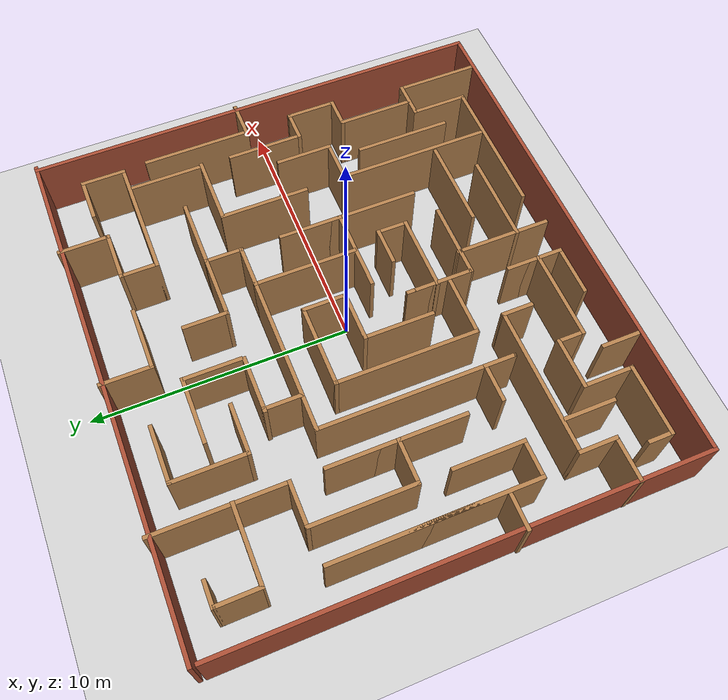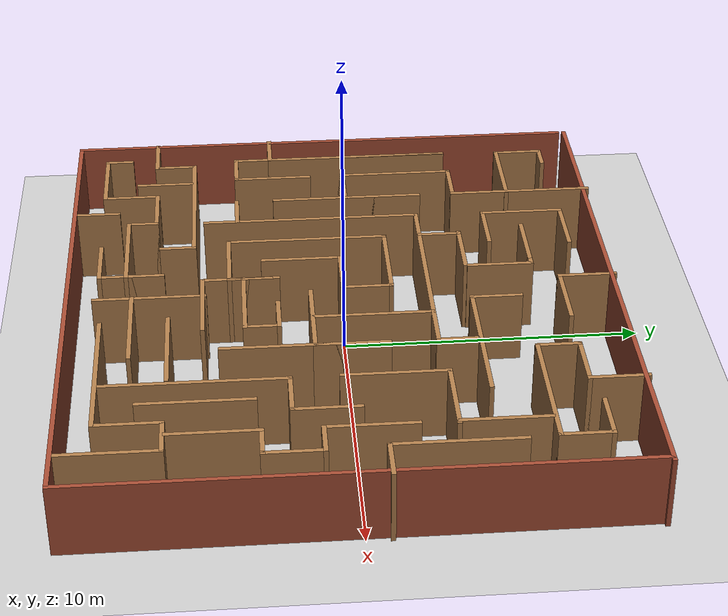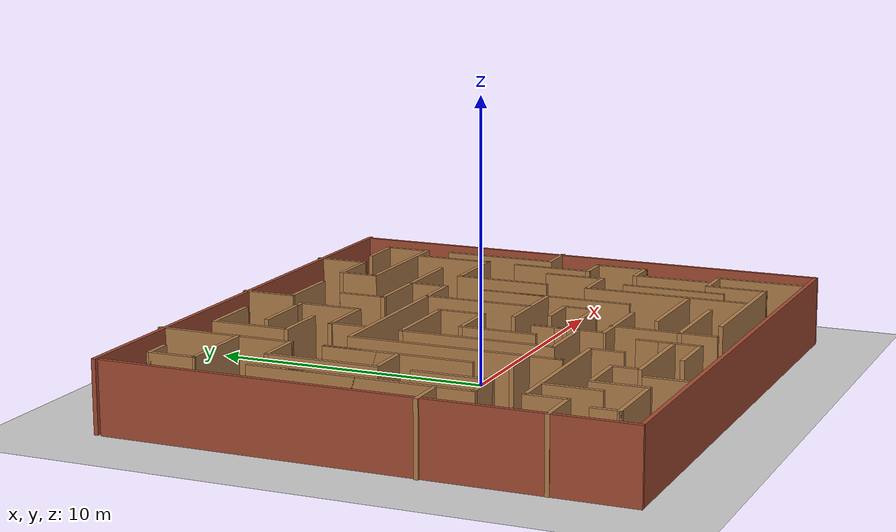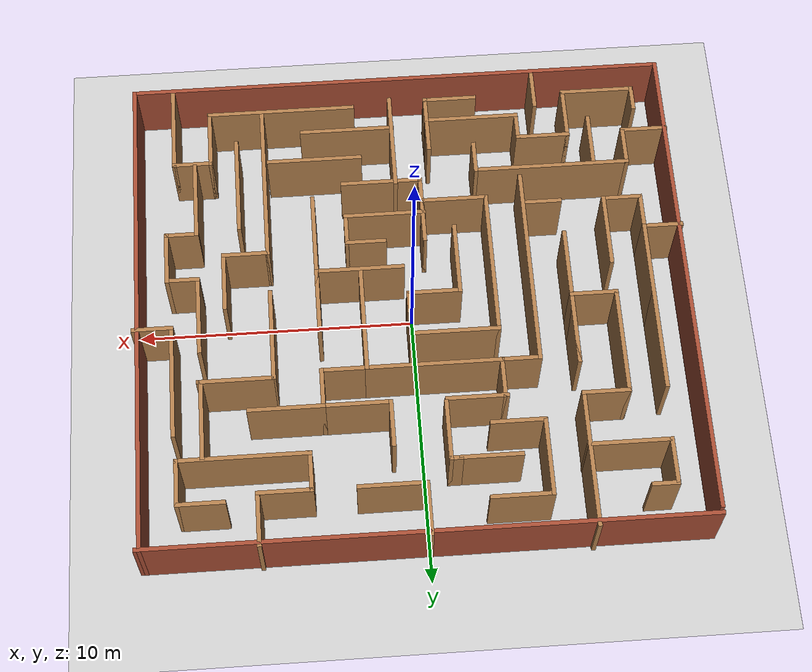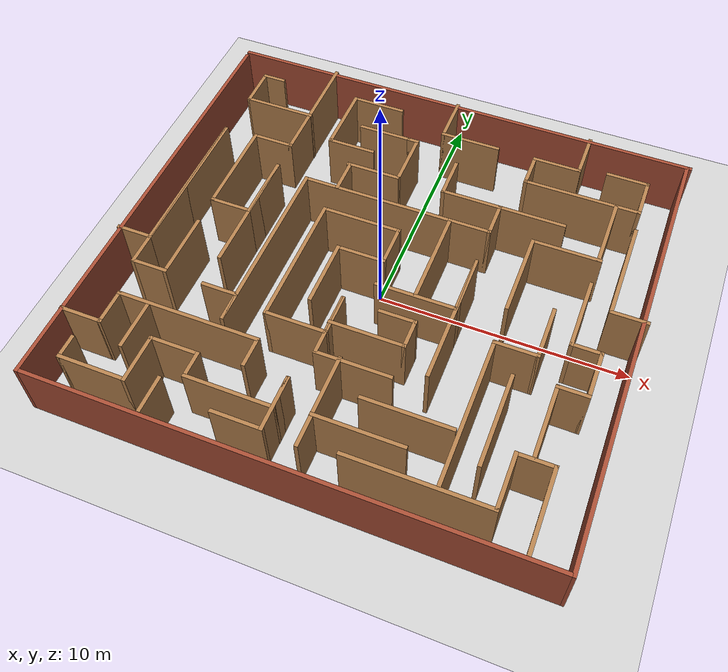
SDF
<sdf version="1.4">
  <world name="default">

    <scene>
      <ambient>0.4 0.4 0.4 1</ambient>
      <background>0.7 0.7 0.7 1</background>
      <shadows>true</shadows>
    </scene>

    <!-- A global light source -->
    <include>
      <uri>model://sun</uri>
    </include>

    <!-- A ground plane -->
    <include>
      <uri>model://ground_plane</uri>
    </include>

    <include>
      <uri>model://complex_maze</uri>
    </include>

    <physics type="ode">
      <real_time_update_rate>1000.0</real_time_update_rate>
      <max_step_size>0.001</max_step_size>
      <real_time_factor>1</real_time_factor>
      <ode>
        <solver>
          <type>quick</type>
          <iters>150</iters>
          <precon_iters>0</precon_iters>
          <sor>1.400000</sor>
          <use_dynamic_moi_rescaling>1</use_dynamic_moi_rescaling>
        </solver>
        <constraints>
          <cfm>0.00001</cfm>
          <erp>0.2</erp>
          <contact_max_correcting_vel>2000.000000</contact_max_correcting_vel>
          <contact_surface_layer>0.01000</contact_surface_layer>
        </constraints>
      </ode>
    </physics>

    <plugin name='gazebo_occupancy_map' filename='libgazebo_2Dmap_plugin.so'>
      <map_resolution>0.1</map_resolution> <!-- in meters, optional, default 0.1 -->
      <map_height>0.3</map_height>         <!-- in meters, optional, default 0.3 -->
      <map_size_x>20</map_size_x>          <!-- in meters, optional, default 10 -->
      <map_size_y>20</map_size_y>          <!-- in meters, optional, default 10 -->
      <init_robot_x>0</init_robot_x>          <!-- x coordinate in meters, optional, default 0 -->
      <init_robot_y>0</init_robot_y>          <!-- y coordinate in meters, optional, default 0 -->
    </plugin>
  </world>

</sdf>

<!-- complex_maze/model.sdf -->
<sdf version='1.6'>
  <model name='complex_maze'>
    <link name='Wall_100'>
      <pose frame=''>8.19444 -2.92775 0 0 -0 0</pose>
      <self_collide>0</self_collide>
      <enable_wind>0</enable_wind>
      <kinematic>0</kinematic>
      <visual name='Wall_100_Visual'>
        <pose frame=''>0 0 1.25 0 -0 0</pose>
        <geometry>
          <box>
            <size>1.25 0.15 2.5</size>
          </box>
        </geometry>
        <material>
          <script>
            <uri>file://media/materials/scripts/gazebo.material</uri>
            <name>Gazebo/Wood</name>
          </script>
          <ambient>1 1 1 1</ambient>
        </material>
        <meta>
          <layer>0</layer>
        </meta>
        <transparency>0</transparency>
        <cast_shadows>1</cast_shadows>
      </visual>
      <collision name='Wall_100_Collision'>
        <laser_retro>0</laser_retro>
        <max_contacts>10</max_contacts>
        <pose frame=''>0 0 1.25 0 -0 0</pose>
        <geometry>
          <box>
            <size>1.25 0.15 2.5</size>
          </box>
        </geometry>
        <surface>
          <friction>
            <ode>
              <mu>1</mu>
              <mu2>1</mu2>
              <fdir1>0 0 0</fdir1>
              <slip1>0</slip1>
              <slip2>0</slip2>
            </ode>
            <torsional>
              <coefficient>1</coefficient>
              <patch_radius>0</patch_radius>
              <surface_radius>0</surface_radius>
              <use_patch_radius>1</use_patch_radius>
              <ode>
                <slip>0</slip>
              </ode>
            </torsional>
          </friction>
          <bounce>
            <restitution_coefficient>0</restitution_coefficient>
            <threshold>1e+06</threshold>
          </bounce>
          <contact>
            <collide_without_contact>0</collide_without_contact>
            <collide_without_contact_bitmask>1</collide_without_contact_bitmask>
            <collide_bitmask>1</collide_bitmask>
            <ode>
              <soft_cfm>0</soft_cfm>
              <soft_erp>0.2</soft_erp>
              <kp>1e+13</kp>
              <kd>1</kd>
              <max_vel>0.01</max_vel>
              <min_depth>0</min_depth>
            </ode>
            <bullet>
              <split_impulse>1</split_impulse>
              <split_impulse_penetration_threshold>-0.01</split_impulse_penetration_threshold>
              <soft_cfm>0</soft_cfm>
              <soft_erp>0.2</soft_erp>
              <kp>1e+13</kp>
              <kd>1</kd>
            </bullet>
          </contact>
        </surface>
      </collision>
    </link>
    <link name='Wall_101'>
      <pose frame=''>8.74444 -2.00275 0 0 -0 1.5708</pose>
      <self_collide>0</self_collide>
      <enable_wind>0</enable_wind>
      <kinematic>0</kinematic>
      <visual name='Wall_101_Visual'>
        <pose frame=''>0 0 1.25 0 -0 0</pose>
        <geometry>
          <box>
            <size>2 0.15 2.5</size>
          </box>
        </geometry>
        <material>
          <script>
            <uri>file://media/materials/scripts/gazebo.material</uri>
            <name>Gazebo/Wood</name>
          </script>
          <ambient>1 1 1 1</ambient>
        </material>
        <meta>
          <layer>0</layer>
        </meta>
        <transparency>0</transparency>
        <cast_shadows>1</cast_shadows>
      </visual>
      <collision name='Wall_101_Collision'>
        <laser_retro>0</laser_retro>
        <max_contacts>10</max_contacts>
        <pose frame=''>0 0 1.25 0 -0 0</pose>
        <geometry>
          <box>
            <size>2 0.15 2.5</size>
          </box>
        </geometry>
        <surface>
          <friction>
            <ode>
              <mu>1</mu>
              <mu2>1</mu2>
              <fdir1>0 0 0</fdir1>
              <slip1>0</slip1>
              <slip2>0</slip2>
            </ode>
            <torsional>
              <coefficient>1</coefficient>
              <patch_radius>0</patch_radius>
              <surface_radius>0</surface_radius>
              <use_patch_radius>1</use_patch_radius>
              <ode>
                <slip>0</slip>
              </ode>
            </torsional>
          </friction>
          <bounce>
            <restitution_coefficient>0</restitution_coefficient>
            <threshold>1e+06</threshold>
          </bounce>
          <contact>
            <collide_without_contact>0</collide_without_contact>
            <collide_without_contact_bitmask>1</collide_without_contact_bitmask>
            <collide_bitmask>1</collide_bitmask>
            <ode>
              <soft_cfm>0</soft_cfm>
              <soft_erp>0.2</soft_erp>
              <kp>1e+13</kp>
              <kd>1</kd>
              <max_vel>0.01</max_vel>
              <min_depth>0</min_depth>
            </ode>
            <bullet>
              <split_impulse>1</split_impulse>
              <split_impulse_penetration_threshold>-0.01</split_impulse_penetration_threshold>
              <soft_cfm>0</soft_cfm>
              <soft_erp>0.2</soft_erp>
              <kp>1e+13</kp>
              <kd>1</kd>
            </bullet>
          </contact>
        </surface>
      </collision>
    </link>
    <link name='Wall_102'>
      <pose frame=''>8.19444 -1.07775 0 0 -0 3.14159</pose>
      <self_collide>0</self_collide>
      <enable_wind>0</enable_wind>
      <kinematic>0</kinematic>
      <visual name='Wall_102_Visual'>
        <pose frame=''>0 0 1.25 0 -0 0</pose>
        <geometry>
          <box>
            <size>1.25 0.15 2.5</size>
          </box>
        </geometry>
        <material>
          <script>
            <uri>file://media/materials/scripts/gazebo.material</uri>
            <name>Gazebo/Wood</name>
          </script>
          <ambient>1 1 1 1</ambient>
        </material>
        <meta>
          <layer>0</layer>
        </meta>
        <transparency>0</transparency>
        <cast_shadows>1</cast_shadows>
      </visual>
      <collision name='Wall_102_Collision'>
        <laser_retro>0</laser_retro>
        <max_contacts>10</max_contacts>
        <pose frame=''>0 0 1.25 0 -0 0</pose>
        <geometry>
          <box>
            <size>1.25 0.15 2.5</size>
          </box>
        </geometry>
        <surface>
          <friction>
            <ode>
              <mu>1</mu>
              <mu2>1</mu2>
              <fdir1>0 0 0</fdir1>
              <slip1>0</slip1>
              <slip2>0</slip2>
            </ode>
            <torsional>
              <coefficient>1</coefficient>
              <patch_radius>0</patch_radius>
              <surface_radius>0</surface_radius>
              <use_patch_radius>1</use_patch_radius>
              <ode>
                <slip>0</slip>
              </ode>
            </torsional>
          </friction>
          <bounce>
            <restitution_coefficient>0</restitution_coefficient>
            <threshold>1e+06</threshold>
          </bounce>
          <contact>
            <collide_without_contact>0</collide_without_contact>
            <collide_without_contact_bitmask>1</collide_without_contact_bitmask>
            <collide_bitmask>1</collide_bitmask>
            <ode>
              <soft_cfm>0</soft_cfm>
              <soft_erp>0.2</soft_erp>
              <kp>1e+13</kp>
              <kd>1</kd>
              <max_vel>0.01</max_vel>
              <min_depth>0</min_depth>
            </ode>
            <bullet>
              <split_impulse>1</split_impulse>
              <split_impulse_penetration_threshold>-0.01</split_impulse_penetration_threshold>
              <soft_cfm>0</soft_cfm>
              <soft_erp>0.2</soft_erp>
              <kp>1e+13</kp>
              <kd>1</kd>
            </bullet>
          </contact>
        </surface>
      </collision>
    </link>
    <link name='Wall_103'>
      <pose frame=''>7.64445 0.347245 0 0 -0 1.5708</pose>
      <self_collide>0</self_collide>
      <enable_wind>0</enable_wind>
      <kinematic>0</kinematic>
      <visual name='Wall_103_Visual'>
        <pose frame=''>0 0 1.25 0 -0 0</pose>
        <geometry>
          <box>
            <size>3 0.15 2.5</size>
          </box>
        </geometry>
        <material>
          <script>
            <uri>file://media/materials/scripts/gazebo.material</uri>
            <name>Gazebo/Wood</name>
          </script>
          <ambient>1 1 1 1</ambient>
        </material>
        <meta>
          <layer>0</layer>
        </meta>
        <transparency>0</transparency>
        <cast_shadows>1</cast_shadows>
      </visual>
      <collision name='Wall_103_Collision'>
        <laser_retro>0</laser_retro>
        <max_contacts>10</max_contacts>
        <pose frame=''>0 0 1.25 0 -0 0</pose>
        <geometry>
          <box>
            <size>3 0.15 2.5</size>
          </box>
        </geometry>
        <surface>
          <friction>
            <ode>
              <mu>1</mu>
              <mu2>1</mu2>
              <fdir1>0 0 0</fdir1>
              <slip1>0</slip1>
              <slip2>0</slip2>
            </ode>
            <torsional>
              <coefficient>1</coefficient>
              <patch_radius>0</patch_radius>
              <surface_radius>0</surface_radius>
              <use_patch_radius>1</use_patch_radius>
              <ode>
                <slip>0</slip>
              </ode>
            </torsional>
          </friction>
          <bounce>
            <restitution_coefficient>0</restitution_coefficient>
            <threshold>1e+06</threshold>
          </bounce>
          <contact>
            <collide_without_contact>0</collide_without_contact>
            <collide_without_contact_bitmask>1</collide_without_contact_bitmask>
            <collide_bitmask>1</collide_bitmask>
            <ode>
              <soft_cfm>0</soft_cfm>
              <soft_erp>0.2</soft_erp>
              <kp>1e+13</kp>
              <kd>1</kd>
              <max_vel>0.01</max_vel>
              <min_depth>0</min_depth>
            </ode>
            <bullet>
              <split_impulse>1</split_impulse>
              <split_impulse_penetration_threshold>-0.01</split_impulse_penetration_threshold>
              <soft_cfm>0</soft_cfm>
              <soft_erp>0.2</soft_erp>
              <kp>1e+13</kp>
              <kd>1</kd>
            </bullet>
          </contact>
        </surface>
      </collision>
    </link>
    <link name='Wall_105'>
      <pose frame=''>-9.29906 -2.16914 0 0 -0 0</pose>
      <self_collide>0</self_collide>
      <enable_wind>0</enable_wind>
      <kinematic>0</kinematic>
      <visual name='Wall_105_Visual'>
        <pose frame=''>0 0 1.25 0 -0 0</pose>
        <geometry>
          <box>
            <size>1.5 0.15 2.5</size>
          </box>
        </geometry>
        <material>
          <script>
            <uri>file://media/materials/scripts/gazebo.material</uri>
            <name>Gazebo/Wood</name>
          </script>
          <ambient>1 1 1 1</ambient>
        </material>
        <meta>
          <layer>0</layer>
        </meta>
        <transparency>0</transparency>
        <cast_shadows>1</cast_shadows>
      </visual>
      <collision name='Wall_105_Collision'>
        <laser_retro>0</laser_retro>
        <max_contacts>10</max_contacts>
        <pose frame=''>0 0 1.25 0 -0 0</pose>
        <geometry>
          <box>
            <size>1.5 0.15 2.5</size>
          </box>
        </geometry>
        <surface>
          <friction>
            <ode>
              <mu>1</mu>
              <mu2>1</mu2>
              <fdir1>0 0 0</fdir1>
              <slip1>0</slip1>
              <slip2>0</slip2>
            </ode>
            <torsional>
              <coefficient>1</coefficient>
              <patch_radius>0</patch_radius>
              <surface_radius>0</surface_radius>
              <use_patch_radius>1</use_patch_radius>
              <ode>
                <slip>0</slip>
              </ode>
            </torsional>
          </friction>
          <bounce>
            <restitution_coefficient>0</restitution_coefficient>
            <threshold>1e+06</threshold>
          </bounce>
          <contact>
            <collide_without_contact>0</collide_without_contact>
            <collide_without_contact_bitmask>1</collide_without_contact_bitmask>
            <collide_bitmask>1</collide_bitmask>
            <ode>
              <soft_cfm>0</soft_cfm>
              <soft_erp>0.2</soft_erp>
              <kp>1e+13</kp>
              <kd>1</kd>
              <max_vel>0.01</max_vel>
              <min_depth>0</min_depth>
            </ode>
            <bullet>
              <split_impulse>1</split_impulse>
              <split_impulse_penetration_threshold>-0.01</split_impulse_penetration_threshold>
              <soft_cfm>0</soft_cfm>
              <soft_erp>0.2</soft_erp>
              <kp>1e+13</kp>
              <kd>1</kd>
            </bullet>
          </contact>
        </surface>
      </collision>
    </link>
    <link name='Wall_106'>
      <pose frame=''>-8.62406 1.00585 0 0 -0 1.5708</pose>
      <self_collide>0</self_collide>
      <enable_wind>0</enable_wind>
      <kinematic>0</kinematic>
      <visual name='Wall_106_Visual'>
        <pose frame=''>0 0 1.25 0 -0 0</pose>
        <geometry>
          <box>
            <size>6.5 0.15 2.5</size>
          </box>
        </geometry>
        <material>
          <script>
            <uri>file://media/materials/scripts/gazebo.material</uri>
            <name>Gazebo/Wood</name>
          </script>
          <ambient>1 1 1 1</ambient>
        </material>
        <meta>
          <layer>0</layer>
        </meta>
        <transparency>0</transparency>
        <cast_shadows>1</cast_shadows>
      </visual>
      <collision name='Wall_106_Collision'>
        <laser_retro>0</laser_retro>
        <max_contacts>10</max_contacts>
        <pose frame=''>0 0 1.25 0 -0 0</pose>
        <geometry>
          <box>
            <size>6.5 0.15 2.5</size>
          </box>
        </geometry>
        <surface>
          <friction>
            <ode>
              <mu>1</mu>
              <mu2>1</mu2>
              <fdir1>0 0 0</fdir1>
              <slip1>0</slip1>
              <slip2>0</slip2>
            </ode>
            <torsional>
              <coefficient>1</coefficient>
              <patch_radius>0</patch_radius>
              <surface_radius>0</surface_radius>
              <use_patch_radius>1</use_patch_radius>
              <ode>
                <slip>0</slip>
              </ode>
            </torsional>
          </friction>
          <bounce>
            <restitution_coefficient>0</restitution_coefficient>
            <threshold>1e+06</threshold>
          </bounce>
          <contact>
            <collide_without_contact>0</collide_without_contact>
            <collide_without_contact_bitmask>1</collide_without_contact_bitmask>
            <collide_bitmask>1</collide_bitmask>
            <ode>
              <soft_cfm>0</soft_cfm>
              <soft_erp>0.2</soft_erp>
              <kp>1e+13</kp>
              <kd>1</kd>
              <max_vel>0.01</max_vel>
              <min_depth>0</min_depth>
            </ode>
            <bullet>
              <split_impulse>1</split_impulse>
              <split_impulse_penetration_threshold>-0.01</split_impulse_penetration_threshold>
              <soft_cfm>0</soft_cfm>
              <soft_erp>0.2</soft_erp>
              <kp>1e+13</kp>
              <kd>1</kd>
            </bullet>
          </contact>
        </surface>
      </collision>
    </link>
    <link name='Wall_107'>
      <pose frame=''>-8.62406 0.380855 0 0 0 -1.5708</pose>
      <self_collide>0</self_collide>
      <enable_wind>0</enable_wind>
      <kinematic>0</kinematic>
      <visual name='Wall_107_Visual'>
        <pose frame=''>0 0 1.25 0 -0 0</pose>
        <geometry>
          <box>
            <size>7.75 0.15 2.5</size>
          </box>
        </geometry>
        <material>
          <script>
            <uri>file://media/materials/scripts/gazebo.material</uri>
            <name>Gazebo/Wood</name>
          </script>
          <ambient>1 1 1 1</ambient>
        </material>
        <meta>
          <layer>0</layer>
        </meta>
        <transparency>0</transparency>
        <cast_shadows>1</cast_shadows>
      </visual>
      <collision name='Wall_107_Collision'>
        <laser_retro>0</laser_retro>
        <max_contacts>10</max_contacts>
        <pose frame=''>0 0 1.25 0 -0 0</pose>
        <geometry>
          <box>
            <size>7.75 0.15 2.5</size>
          </box>
        </geometry>
        <surface>
          <friction>
            <ode>
              <mu>1</mu>
              <mu2>1</mu2>
              <fdir1>0 0 0</fdir1>
              <slip1>0</slip1>
              <slip2>0</slip2>
            </ode>
            <torsional>
              <coefficient>1</coefficient>
              <patch_radius>0</patch_radius>
              <surface_radius>0</surface_radius>
              <use_patch_radius>1</use_patch_radius>
              <ode>
                <slip>0</slip>
              </ode>
            </torsional>
          </friction>
          <bounce>
            <restitution_coefficient>0</restitution_coefficient>
            <threshold>1e+06</threshold>
          </bounce>
          <contact>
            <collide_without_contact>0</collide_without_contact>
            <collide_without_contact_bitmask>1</collide_without_contact_bitmask>
            <collide_bitmask>1</collide_bitmask>
            <ode>
              <soft_cfm>0</soft_cfm>
              <soft_erp>0.2</soft_erp>
              <kp>1e+13</kp>
              <kd>1</kd>
              <max_vel>0.01</max_vel>
              <min_depth>0</min_depth>
            </ode>
            <bullet>
              <split_impulse>1</split_impulse>
              <split_impulse_penetration_threshold>-0.01</split_impulse_penetration_threshold>
              <soft_cfm>0</soft_cfm>
              <soft_erp>0.2</soft_erp>
              <kp>1e+13</kp>
              <kd>1</kd>
            </bullet>
          </contact>
        </surface>
      </collision>
    </link>
    <link name='Wall_108'>
      <pose frame=''>-7.94906 -3.41914 0 0 -0 0</pose>
      <self_collide>0</self_collide>
      <enable_wind>0</enable_wind>
      <kinematic>0</kinematic>
      <visual name='Wall_108_Visual'>
        <pose frame=''>0 0 1.25 0 -0 0</pose>
        <geometry>
          <box>
            <size>1.5 0.15 2.5</size>
          </box>
        </geometry>
        <material>
          <script>
            <uri>file://media/materials/scripts/gazebo.material</uri>
            <name>Gazebo/Wood</name>
          </script>
          <ambient>1 1 1 1</ambient>
        </material>
        <meta>
          <layer>0</layer>
        </meta>
        <transparency>0</transparency>
        <cast_shadows>1</cast_shadows>
      </visual>
      <collision name='Wall_108_Collision'>
        <laser_retro>0</laser_retro>
        <max_contacts>10</max_contacts>
        <pose frame=''>0 0 1.25 0 -0 0</pose>
        <geometry>
          <box>
            <size>1.5 0.15 2.5</size>
          </box>
        </geometry>
        <surface>
          <friction>
            <ode>
              <mu>1</mu>
              <mu2>1</mu2>
              <fdir1>0 0 0</fdir1>
              <slip1>0</slip1>
              <slip2>0</slip2>
            </ode>
            <torsional>
              <coefficient>1</coefficient>
              <patch_radius>0</patch_radius>
              <surface_radius>0</surface_radius>
              <use_patch_radius>1</use_patch_radius>
              <ode>
                <slip>0</slip>
              </ode>
            </torsional>
          </friction>
          <bounce>
            <restitution_coefficient>0</restitution_coefficient>
            <threshold>1e+06</threshold>
          </bounce>
          <contact>
            <collide_without_contact>0</collide_without_contact>
            <collide_without_contact_bitmask>1</collide_without_contact_bitmask>
            <collide_bitmask>1</collide_bitmask>
            <ode>
              <soft_cfm>0</soft_cfm>
              <soft_erp>0.2</soft_erp>
              <kp>1e+13</kp>
              <kd>1</kd>
              <max_vel>0.01</max_vel>
              <min_depth>0</min_depth>
            </ode>
            <bullet>
              <split_impulse>1</split_impulse>
              <split_impulse_penetration_threshold>-0.01</split_impulse_penetration_threshold>
              <soft_cfm>0</soft_cfm>
              <soft_erp>0.2</soft_erp>
              <kp>1e+13</kp>
              <kd>1</kd>
            </bullet>
          </contact>
        </surface>
      </collision>
    </link>
    <link name='Wall_109'>
      <pose frame=''>-7.27406 -2.11915 0 0 -0 1.5708</pose>
      <self_collide>0</self_collide>
      <enable_wind>0</enable_wind>
      <kinematic>0</kinematic>
      <visual name='Wall_109_Visual'>
        <pose frame=''>0 0 1.25 0 -0 0</pose>
        <geometry>
          <box>
            <size>2.75 0.15 2.5</size>
          </box>
        </geometry>
        <material>
          <script>
            <uri>file://media/materials/scripts/gazebo.material</uri>
            <name>Gazebo/Wood</name>
          </script>
          <ambient>1 1 1 1</ambient>
        </material>
        <meta>
          <layer>0</layer>
        </meta>
        <transparency>0</transparency>
        <cast_shadows>1</cast_shadows>
      </visual>
      <collision name='Wall_109_Collision'>
        <laser_retro>0</laser_retro>
        <max_contacts>10</max_contacts>
        <pose frame=''>0 0 1.25 0 -0 0</pose>
        <geometry>
          <box>
            <size>2.75 0.15 2.5</size>
          </box>
        </geometry>
        <surface>
          <friction>
            <ode>
              <mu>1</mu>
              <mu2>1</mu2>
              <fdir1>0 0 0</fdir1>
              <slip1>0</slip1>
              <slip2>0</slip2>
            </ode>
            <torsional>
              <coefficient>1</coefficient>
              <patch_radius>0</patch_radius>
              <surface_radius>0</surface_radius>
              <use_patch_radius>1</use_patch_radius>
              <ode>
                <slip>0</slip>
              </ode>
            </torsional>
          </friction>
          <bounce>
            <restitution_coefficient>0</restitution_coefficient>
            <threshold>1e+06</threshold>
          </bounce>
          <contact>
            <collide_without_contact>0</collide_without_contact>
            <collide_without_contact_bitmask>1</collide_without_contact_bitmask>
            <collide_bitmask>1</collide_bitmask>
            <ode>
              <soft_cfm>0</soft_cfm>
              <soft_erp>0.2</soft_erp>
              <kp>1e+13</kp>
              <kd>1</kd>
              <max_vel>0.01</max_vel>
              <min_depth>0</min_depth>
            </ode>
            <bullet>
              <split_impulse>1</split_impulse>
              <split_impulse_penetration_threshold>-0.01</split_impulse_penetration_threshold>
              <soft_cfm>0</soft_cfm>
              <soft_erp>0.2</soft_erp>
              <kp>1e+13</kp>
              <kd>1</kd>
            </bullet>
          </contact>
        </surface>
      </collision>
    </link>
    <link name='Wall_111'>
      <pose frame=''>-7.28529 2.34475 0 0 0 -1.5708</pose>
      <self_collide>0</self_collide>
      <enable_wind>0</enable_wind>
      <kinematic>0</kinematic>
      <visual name='Wall_111_Visual'>
        <pose frame=''>0 0 1.25 0 -0 0</pose>
        <geometry>
          <box>
            <size>4 0.15 2.5</size>
          </box>
        </geometry>
        <material>
          <script>
            <uri>file://media/materials/scripts/gazebo.material</uri>
            <name>Gazebo/Wood</name>
          </script>
          <ambient>1 1 1 1</ambient>
        </material>
        <meta>
          <layer>0</layer>
        </meta>
        <transparency>0</transparency>
        <cast_shadows>1</cast_shadows>
      </visual>
      <collision name='Wall_111_Collision'>
        <laser_retro>0</laser_retro>
        <max_contacts>10</max_contacts>
        <pose frame=''>0 0 1.25 0 -0 0</pose>
        <geometry>
          <box>
            <size>4 0.15 2.5</size>
          </box>
        </geometry>
        <surface>
          <friction>
            <ode>
              <mu>1</mu>
              <mu2>1</mu2>
              <fdir1>0 0 0</fdir1>
              <slip1>0</slip1>
              <slip2>0</slip2>
            </ode>
            <torsional>
              <coefficient>1</coefficient>
              <patch_radius>0</patch_radius>
              <surface_radius>0</surface_radius>
              <use_patch_radius>1</use_patch_radius>
              <ode>
                <slip>0</slip>
              </ode>
            </torsional>
          </friction>
          <bounce>
            <restitution_coefficient>0</restitution_coefficient>
            <threshold>1e+06</threshold>
          </bounce>
          <contact>
            <collide_without_contact>0</collide_without_contact>
            <collide_without_contact_bitmask>1</collide_without_contact_bitmask>
            <collide_bitmask>1</collide_bitmask>
            <ode>
              <soft_cfm>0</soft_cfm>
              <soft_erp>0.2</soft_erp>
              <kp>1e+13</kp>
              <kd>1</kd>
              <max_vel>0.01</max_vel>
              <min_depth>0</min_depth>
            </ode>
            <bullet>
              <split_impulse>1</split_impulse>
              <split_impulse_penetration_threshold>-0.01</split_impulse_penetration_threshold>
              <soft_cfm>0</soft_cfm>
              <soft_erp>0.2</soft_erp>
              <kp>1e+13</kp>
              <kd>1</kd>
            </bullet>
          </contact>
        </surface>
      </collision>
    </link>
    <link name='Wall_112'>
      <pose frame=''>-6.48529 0.419748 0 0 -0 0</pose>
      <self_collide>0</self_collide>
      <enable_wind>0</enable_wind>
      <kinematic>0</kinematic>
      <visual name='Wall_112_Visual'>
        <pose frame=''>0 0 1.25 0 -0 0</pose>
        <geometry>
          <box>
            <size>1.75 0.15 2.5</size>
          </box>
        </geometry>
        <material>
          <script>
            <uri>file://media/materials/scripts/gazebo.material</uri>
            <name>Gazebo/Wood</name>
          </script>
          <ambient>1 1 1 1</ambient>
        </material>
        <meta>
          <layer>0</layer>
        </meta>
        <transparency>0</transparency>
        <cast_shadows>1</cast_shadows>
      </visual>
      <collision name='Wall_112_Collision'>
        <laser_retro>0</laser_retro>
        <max_contacts>10</max_contacts>
        <pose frame=''>0 0 1.25 0 -0 0</pose>
        <geometry>
          <box>
            <size>1.75 0.15 2.5</size>
          </box>
        </geometry>
        <surface>
          <friction>
            <ode>
              <mu>1</mu>
              <mu2>1</mu2>
              <fdir1>0 0 0</fdir1>
              <slip1>0</slip1>
              <slip2>0</slip2>
            </ode>
            <torsional>
              <coefficient>1</coefficient>
              <patch_radius>0</patch_radius>
              <surface_radius>0</surface_radius>
              <use_patch_radius>1</use_patch_radius>
              <ode>
                <slip>0</slip>
              </ode>
            </torsional>
          </friction>
          <bounce>
            <restitution_coefficient>0</restitution_coefficient>
            <threshold>1e+06</threshold>
          </bounce>
          <contact>
            <collide_without_contact>0</collide_without_contact>
            <collide_without_contact_bitmask>1</collide_without_contact_bitmask>
            <collide_bitmask>1</collide_bitmask>
            <ode>
              <soft_cfm>0</soft_cfm>
              <soft_erp>0.2</soft_erp>
              <kp>1e+13</kp>
              <kd>1</kd>
              <max_vel>0.01</max_vel>
              <min_depth>0</min_depth>
            </ode>
            <bullet>
              <split_impulse>1</split_impulse>
              <split_impulse_penetration_threshold>-0.01</split_impulse_penetration_threshold>
              <soft_cfm>0</soft_cfm>
              <soft_erp>0.2</soft_erp>
              <kp>1e+13</kp>
              <kd>1</kd>
            </bullet>
          </contact>
        </surface>
      </collision>
    </link>
    <link name='Wall_113'>
      <pose frame=''>-5.68529 1.71975 0 0 -0 1.5708</pose>
      <self_collide>0</self_collide>
      <enable_wind>0</enable_wind>
      <kinematic>0</kinematic>
      <visual name='Wall_113_Visual'>
        <pose frame=''>0 0 1.25 0 -0 0</pose>
        <geometry>
          <box>
            <size>2.75 0.15 2.5</size>
          </box>
        </geometry>
        <material>
          <script>
            <uri>file://media/materials/scripts/gazebo.material</uri>
            <name>Gazebo/Wood</name>
          </script>
          <ambient>1 1 1 1</ambient>
        </material>
        <meta>
          <layer>0</layer>
        </meta>
        <transparency>0</transparency>
        <cast_shadows>1</cast_shadows>
      </visual>
      <collision name='Wall_113_Collision'>
        <laser_retro>0</laser_retro>
        <max_contacts>10</max_contacts>
        <pose frame=''>0 0 1.25 0 -0 0</pose>
        <geometry>
          <box>
            <size>2.75 0.15 2.5</size>
          </box>
        </geometry>
        <surface>
          <friction>
            <ode>
              <mu>1</mu>
              <mu2>1</mu2>
              <fdir1>0 0 0</fdir1>
              <slip1>0</slip1>
              <slip2>0</slip2>
            </ode>
            <torsional>
              <coefficient>1</coefficient>
              <patch_radius>0</patch_radius>
              <surface_radius>0</surface_radius>
              <use_patch_radius>1</use_patch_radius>
              <ode>
                <slip>0</slip>
              </ode>
            </torsional>
          </friction>
          <bounce>
            <restitution_coefficient>0</restitution_coefficient>
            <threshold>1e+06</threshold>
          </bounce>
          <contact>
            <collide_without_contact>0</collide_without_contact>
            <collide_without_contact_bitmask>1</collide_without_contact_bitmask>
            <collide_bitmask>1</collide_bitmask>
            <ode>
              <soft_cfm>0</soft_cfm>
              <soft_erp>0.2</soft_erp>
              <kp>1e+13</kp>
              <kd>1</kd>
              <max_vel>0.01</max_vel>
              <min_depth>0</min_depth>
            </ode>
            <bullet>
              <split_impulse>1</split_impulse>
              <split_impulse_penetration_threshold>-0.01</split_impulse_penetration_threshold>
              <soft_cfm>0</soft_cfm>
              <soft_erp>0.2</soft_erp>
              <kp>1e+13</kp>
              <kd>1</kd>
            </bullet>
          </contact>
        </surface>
      </collision>
    </link>
    <link name='Wall_114'>
      <pose frame=''>-5.68529 0.469748 0 0 0 -1.5708</pose>
      <self_collide>0</self_collide>
      <enable_wind>0</enable_wind>
      <kinematic>0</kinematic>
      <visual name='Wall_114_Visual'>
        <pose frame=''>0 0 1.25 0 -0 0</pose>
        <geometry>
          <box>
            <size>5.25 0.15 2.5</size>
          </box>
        </geometry>
        <material>
          <script>
            <uri>file://media/materials/scripts/gazebo.material</uri>
            <name>Gazebo/Wood</name>
          </script>
          <ambient>1 1 1 1</ambient>
        </material>
        <meta>
          <layer>0</layer>
        </meta>
        <transparency>0</transparency>
        <cast_shadows>1</cast_shadows>
      </visual>
      <collision name='Wall_114_Collision'>
        <laser_retro>0</laser_retro>
        <max_contacts>10</max_contacts>
        <pose frame=''>0 0 1.25 0 -0 0</pose>
        <geometry>
          <box>
            <size>5.25 0.15 2.5</size>
          </box>
        </geometry>
        <surface>
          <friction>
            <ode>
              <mu>1</mu>
              <mu2>1</mu2>
              <fdir1>0 0 0</fdir1>
              <slip1>0</slip1>
              <slip2>0</slip2>
            </ode>
            <torsional>
              <coefficient>1</coefficient>
              <patch_radius>0</patch_radius>
              <surface_radius>0</surface_radius>
              <use_patch_radius>1</use_patch_radius>
              <ode>
                <slip>0</slip>
              </ode>
            </torsional>
          </friction>
          <bounce>
            <restitution_coefficient>0</restitution_coefficient>
            <threshold>1e+06</threshold>
          </bounce>
          <contact>
            <collide_without_contact>0</collide_without_contact>
            <collide_without_contact_bitmask>1</collide_without_contact_bitmask>
            <collide_bitmask>1</collide_bitmask>
            <ode>
              <soft_cfm>0</soft_cfm>
              <soft_erp>0.2</soft_erp>
              <kp>1e+13</kp>
              <kd>1</kd>
              <max_vel>0.01</max_vel>
              <min_depth>0</min_depth>
            </ode>
            <bullet>
              <split_impulse>1</split_impulse>
              <split_impulse_penetration_threshold>-0.01</split_impulse_penetration_threshold>
              <soft_cfm>0</soft_cfm>
              <soft_erp>0.2</soft_erp>
              <kp>1e+13</kp>
              <kd>1</kd>
            </bullet>
          </contact>
        </surface>
      </collision>
    </link>
    <link name='Wall_116'>
      <pose frame=''>-4.98288 -3.44277 0 0 -0 0</pose>
      <self_collide>0</self_collide>
      <enable_wind>0</enable_wind>
      <kinematic>0</kinematic>
      <visual name='Wall_116_Visual'>
        <pose frame=''>0 0 1.25 0 -0 0</pose>
        <geometry>
          <box>
            <size>1.5 0.15 2.5</size>
          </box>
        </geometry>
        <material>
          <script>
            <uri>file://media/materials/scripts/gazebo.material</uri>
            <name>Gazebo/Wood</name>
          </script>
          <ambient>1 1 1 1</ambient>
        </material>
        <meta>
          <layer>0</layer>
        </meta>
        <transparency>0</transparency>
        <cast_shadows>1</cast_shadows>
      </visual>
      <collision name='Wall_116_Collision'>
        <laser_retro>0</laser_retro>
        <max_contacts>10</max_contacts>
        <pose frame=''>0 0 1.25 0 -0 0</pose>
        <geometry>
          <box>
            <size>1.5 0.15 2.5</size>
          </box>
        </geometry>
        <surface>
          <friction>
            <ode>
              <mu>1</mu>
              <mu2>1</mu2>
              <fdir1>0 0 0</fdir1>
              <slip1>0</slip1>
              <slip2>0</slip2>
            </ode>
            <torsional>
              <coefficient>1</coefficient>
              <patch_radius>0</patch_radius>
              <surface_radius>0</surface_radius>
              <use_patch_radius>1</use_patch_radius>
              <ode>
                <slip>0</slip>
              </ode>
            </torsional>
          </friction>
          <bounce>
            <restitution_coefficient>0</restitution_coefficient>
            <threshold>1e+06</threshold>
          </bounce>
          <contact>
            <collide_without_contact>0</collide_without_contact>
            <collide_without_contact_bitmask>1</collide_without_contact_bitmask>
            <collide_bitmask>1</collide_bitmask>
            <ode>
              <soft_cfm>0</soft_cfm>
              <soft_erp>0.2</soft_erp>
              <kp>1e+13</kp>
              <kd>1</kd>
              <max_vel>0.01</max_vel>
              <min_depth>0</min_depth>
            </ode>
            <bullet>
              <split_impulse>1</split_impulse>
              <split_impulse_penetration_threshold>-0.01</split_impulse_penetration_threshold>
              <soft_cfm>0</soft_cfm>
              <soft_erp>0.2</soft_erp>
              <kp>1e+13</kp>
              <kd>1</kd>
            </bullet>
          </contact>
        </surface>
      </collision>
    </link>
    <link name='Wall_117'>
      <pose frame=''>-4.30788 -3.99277 0 0 0 -1.5708</pose>
      <self_collide>0</self_collide>
      <enable_wind>0</enable_wind>
      <kinematic>0</kinematic>
      <visual name='Wall_117_Visual'>
        <pose frame=''>0 0 1.25 0 -0 0</pose>
        <geometry>
          <box>
            <size>1.25 0.15 2.5</size>
          </box>
        </geometry>
        <material>
          <script>
            <uri>file://media/materials/scripts/gazebo.material</uri>
            <name>Gazebo/Wood</name>
          </script>
          <ambient>1 1 1 1</ambient>
        </material>
        <meta>
          <layer>0</layer>
        </meta>
        <transparency>0</transparency>
        <cast_shadows>1</cast_shadows>
      </visual>
      <collision name='Wall_117_Collision'>
        <laser_retro>0</laser_retro>
        <max_contacts>10</max_contacts>
        <pose frame=''>0 0 1.25 0 -0 0</pose>
        <geometry>
          <box>
            <size>1.25 0.15 2.5</size>
          </box>
        </geometry>
        <surface>
          <friction>
            <ode>
              <mu>1</mu>
              <mu2>1</mu2>
              <fdir1>0 0 0</fdir1>
              <slip1>0</slip1>
              <slip2>0</slip2>
            </ode>
            <torsional>
              <coefficient>1</coefficient>
              <patch_radius>0</patch_radius>
              <surface_radius>0</surface_radius>
              <use_patch_radius>1</use_patch_radius>
              <ode>
                <slip>0</slip>
              </ode>
            </torsional>
          </friction>
          <bounce>
            <restitution_coefficient>0</restitution_coefficient>
            <threshold>1e+06</threshold>
          </bounce>
          <contact>
            <collide_without_contact>0</collide_without_contact>
            <collide_without_contact_bitmask>1</collide_without_contact_bitmask>
            <collide_bitmask>1</collide_bitmask>
            <ode>
              <soft_cfm>0</soft_cfm>
              <soft_erp>0.2</soft_erp>
              <kp>1e+13</kp>
              <kd>1</kd>
              <max_vel>0.01</max_vel>
              <min_depth>0</min_depth>
            </ode>
            <bullet>
              <split_impulse>1</split_impulse>
              <split_impulse_penetration_threshold>-0.01</split_impulse_penetration_threshold>
              <soft_cfm>0</soft_cfm>
              <soft_erp>0.2</soft_erp>
              <kp>1e+13</kp>
              <kd>1</kd>
            </bullet>
          </contact>
        </surface>
      </collision>
    </link>
    <link name='Wall_118'>
      <pose frame=''>-4.30788 -0.867772 0 0 -0 1.5708</pose>
      <self_collide>0</self_collide>
      <enable_wind>0</enable_wind>
      <kinematic>0</kinematic>
      <visual name='Wall_118_Visual'>
        <pose frame=''>0 0 1.25 0 -0 0</pose>
        <geometry>
          <box>
            <size>7.5 0.15 2.5</size>
          </box>
        </geometry>
        <material>
          <script>
            <uri>file://media/materials/scripts/gazebo.material</uri>
            <name>Gazebo/Wood</name>
          </script>
          <ambient>1 1 1 1</ambient>
        </material>
        <meta>
          <layer>0</layer>
        </meta>
        <transparency>0</transparency>
        <cast_shadows>1</cast_shadows>
      </visual>
      <collision name='Wall_118_Collision'>
        <laser_retro>0</laser_retro>
        <max_contacts>10</max_contacts>
        <pose frame=''>0 0 1.25 0 -0 0</pose>
        <geometry>
          <box>
            <size>7.5 0.15 2.5</size>
          </box>
        </geometry>
        <surface>
          <friction>
            <ode>
              <mu>1</mu>
              <mu2>1</mu2>
              <fdir1>0 0 0</fdir1>
              <slip1>0</slip1>
              <slip2>0</slip2>
            </ode>
            <torsional>
              <coefficient>1</coefficient>
              <patch_radius>0</patch_radius>
              <surface_radius>0</surface_radius>
              <use_patch_radius>1</use_patch_radius>
              <ode>
                <slip>0</slip>
              </ode>
            </torsional>
          </friction>
          <bounce>
            <restitution_coefficient>0</restitution_coefficient>
            <threshold>1e+06</threshold>
          </bounce>
          <contact>
            <collide_without_contact>0</collide_without_contact>
            <collide_without_contact_bitmask>1</collide_without_contact_bitmask>
            <collide_bitmask>1</collide_bitmask>
            <ode>
              <soft_cfm>0</soft_cfm>
              <soft_erp>0.2</soft_erp>
              <kp>1e+13</kp>
              <kd>1</kd>
              <max_vel>0.01</max_vel>
              <min_depth>0</min_depth>
            </ode>
            <bullet>
              <split_impulse>1</split_impulse>
              <split_impulse_penetration_threshold>-0.01</split_impulse_penetration_threshold>
              <soft_cfm>0</soft_cfm>
              <soft_erp>0.2</soft_erp>
              <kp>1e+13</kp>
              <kd>1</kd>
            </bullet>
          </contact>
        </surface>
      </collision>
    </link>
    <link name='Wall_119'>
      <pose frame=''>-1.25788 2.80723 0 0 -0 0</pose>
      <self_collide>0</self_collide>
      <enable_wind>0</enable_wind>
      <kinematic>0</kinematic>
      <visual name='Wall_119_Visual'>
        <pose frame=''>0 0 1.25 0 -0 0</pose>
        <geometry>
          <box>
            <size>6.25 0.15 2.5</size>
          </box>
        </geometry>
        <material>
          <script>
            <uri>file://media/materials/scripts/gazebo.material</uri>
            <name>Gazebo/Wood</name>
          </script>
          <ambient>1 1 1 1</ambient>
        </material>
        <meta>
          <layer>0</layer>
        </meta>
        <transparency>0</transparency>
        <cast_shadows>1</cast_shadows>
      </visual>
      <collision name='Wall_119_Collision'>
        <laser_retro>0</laser_retro>
        <max_contacts>10</max_contacts>
        <pose frame=''>0 0 1.25 0 -0 0</pose>
        <geometry>
          <box>
            <size>6.25 0.15 2.5</size>
          </box>
        </geometry>
        <surface>
          <friction>
            <ode>
              <mu>1</mu>
              <mu2>1</mu2>
              <fdir1>0 0 0</fdir1>
              <slip1>0</slip1>
              <slip2>0</slip2>
            </ode>
            <torsional>
              <coefficient>1</coefficient>
              <patch_radius>0</patch_radius>
              <surface_radius>0</surface_radius>
              <use_patch_radius>1</use_patch_radius>
              <ode>
                <slip>0</slip>
              </ode>
            </torsional>
          </friction>
          <bounce>
            <restitution_coefficient>0</restitution_coefficient>
            <threshold>1e+06</threshold>
          </bounce>
          <contact>
            <collide_without_contact>0</collide_without_contact>
            <collide_without_contact_bitmask>1</collide_without_contact_bitmask>
            <collide_bitmask>1</collide_bitmask>
            <ode>
              <soft_cfm>0</soft_cfm>
              <soft_erp>0.2</soft_erp>
              <kp>1e+13</kp>
              <kd>1</kd>
              <max_vel>0.01</max_vel>
              <min_depth>0</min_depth>
            </ode>
            <bullet>
              <split_impulse>1</split_impulse>
              <split_impulse_penetration_threshold>-0.01</split_impulse_penetration_threshold>
              <soft_cfm>0</soft_cfm>
              <soft_erp>0.2</soft_erp>
              <kp>1e+13</kp>
              <kd>1</kd>
            </bullet>
          </contact>
        </surface>
      </collision>
    </link>
    <link name='Wall_120'>
      <pose frame=''>1.79212 0.882228 0 0 0 -1.5708</pose>
      <self_collide>0</self_collide>
      <enable_wind>0</enable_wind>
      <kinematic>0</kinematic>
      <visual name='Wall_120_Visual'>
        <pose frame=''>0 0 1.25 0 -0 0</pose>
        <geometry>
          <box>
            <size>4 0.15 2.5</size>
          </box>
        </geometry>
        <material>
          <script>
            <uri>file://media/materials/scripts/gazebo.material</uri>
            <name>Gazebo/Wood</name>
          </script>
          <ambient>1 1 1 1</ambient>
        </material>
        <meta>
          <layer>0</layer>
        </meta>
        <transparency>0</transparency>
        <cast_shadows>1</cast_shadows>
      </visual>
      <collision name='Wall_120_Collision'>
        <laser_retro>0</laser_retro>
        <max_contacts>10</max_contacts>
        <pose frame=''>0 0 1.25 0 -0 0</pose>
        <geometry>
          <box>
            <size>4 0.15 2.5</size>
          </box>
        </geometry>
        <surface>
          <friction>
            <ode>
              <mu>1</mu>
              <mu2>1</mu2>
              <fdir1>0 0 0</fdir1>
              <slip1>0</slip1>
              <slip2>0</slip2>
            </ode>
            <torsional>
              <coefficient>1</coefficient>
              <patch_radius>0</patch_radius>
              <surface_radius>0</surface_radius>
              <use_patch_radius>1</use_patch_radius>
              <ode>
                <slip>0</slip>
              </ode>
            </torsional>
          </friction>
          <bounce>
            <restitution_coefficient>0</restitution_coefficient>
            <threshold>1e+06</threshold>
          </bounce>
          <contact>
            <collide_without_contact>0</collide_without_contact>
            <collide_without_contact_bitmask>1</collide_without_contact_bitmask>
            <collide_bitmask>1</collide_bitmask>
            <ode>
              <soft_cfm>0</soft_cfm>
              <soft_erp>0.2</soft_erp>
              <kp>1e+13</kp>
              <kd>1</kd>
              <max_vel>0.01</max_vel>
              <min_depth>0</min_depth>
            </ode>
            <bullet>
              <split_impulse>1</split_impulse>
              <split_impulse_penetration_threshold>-0.01</split_impulse_penetration_threshold>
              <soft_cfm>0</soft_cfm>
              <soft_erp>0.2</soft_erp>
              <kp>1e+13</kp>
              <kd>1</kd>
            </bullet>
          </contact>
        </surface>
      </collision>
    </link>
    <link name='Wall_122'>
      <pose frame=''>-1.41911 1.58098 0 0 -0 0</pose>
      <self_collide>0</self_collide>
      <enable_wind>0</enable_wind>
      <kinematic>0</kinematic>
      <visual name='Wall_122_Visual'>
        <pose frame=''>0 0 1.25 0 -0 0</pose>
        <geometry>
          <box>
            <size>3.25 0.15 2.5</size>
          </box>
        </geometry>
        <material>
          <script>
            <uri>file://media/materials/scripts/gazebo.material</uri>
            <name>Gazebo/Wood</name>
          </script>
          <ambient>1 1 1 1</ambient>
        </material>
        <meta>
          <layer>0</layer>
        </meta>
        <transparency>0</transparency>
        <cast_shadows>1</cast_shadows>
      </visual>
      <collision name='Wall_122_Collision'>
        <laser_retro>0</laser_retro>
        <max_contacts>10</max_contacts>
        <pose frame=''>0 0 1.25 0 -0 0</pose>
        <geometry>
          <box>
            <size>3.25 0.15 2.5</size>
          </box>
        </geometry>
        <surface>
          <friction>
            <ode>
              <mu>1</mu>
              <mu2>1</mu2>
              <fdir1>0 0 0</fdir1>
              <slip1>0</slip1>
              <slip2>0</slip2>
            </ode>
            <torsional>
              <coefficient>1</coefficient>
              <patch_radius>0</patch_radius>
              <surface_radius>0</surface_radius>
              <use_patch_radius>1</use_patch_radius>
              <ode>
                <slip>0</slip>
              </ode>
            </torsional>
          </friction>
          <bounce>
            <restitution_coefficient>0</restitution_coefficient>
            <threshold>1e+06</threshold>
          </bounce>
          <contact>
            <collide_without_contact>0</collide_without_contact>
            <collide_without_contact_bitmask>1</collide_without_contact_bitmask>
            <collide_bitmask>1</collide_bitmask>
            <ode>
              <soft_cfm>0</soft_cfm>
              <soft_erp>0.2</soft_erp>
              <kp>1e+13</kp>
              <kd>1</kd>
              <max_vel>0.01</max_vel>
              <min_depth>0</min_depth>
            </ode>
            <bullet>
              <split_impulse>1</split_impulse>
              <split_impulse_penetration_threshold>-0.01</split_impulse_penetration_threshold>
              <soft_cfm>0</soft_cfm>
              <soft_erp>0.2</soft_erp>
              <kp>1e+13</kp>
              <kd>1</kd>
            </bullet>
          </contact>
        </surface>
      </collision>
    </link>
    <link name='Wall_123'>
      <pose frame=''>0.130886 0.780979 0 0 0 -1.5708</pose>
      <self_collide>0</self_collide>
      <enable_wind>0</enable_wind>
      <kinematic>0</kinematic>
      <visual name='Wall_123_Visual'>
        <pose frame=''>0 0 1.25 0 -0 0</pose>
        <geometry>
          <box>
            <size>1.75 0.15 2.5</size>
          </box>
        </geometry>
        <material>
          <script>
            <uri>file://media/materials/scripts/gazebo.material</uri>
            <name>Gazebo/Wood</name>
          </script>
          <ambient>1 1 1 1</ambient>
        </material>
        <meta>
          <layer>0</layer>
        </meta>
        <transparency>0</transparency>
        <cast_shadows>1</cast_shadows>
      </visual>
      <collision name='Wall_123_Collision'>
        <laser_retro>0</laser_retro>
        <max_contacts>10</max_contacts>
        <pose frame=''>0 0 1.25 0 -0 0</pose>
        <geometry>
          <box>
            <size>1.75 0.15 2.5</size>
          </box>
        </geometry>
        <surface>
          <friction>
            <ode>
              <mu>1</mu>
              <mu2>1</mu2>
              <fdir1>0 0 0</fdir1>
              <slip1>0</slip1>
              <slip2>0</slip2>
            </ode>
            <torsional>
              <coefficient>1</coefficient>
              <patch_radius>0</patch_radius>
              <surface_radius>0</surface_radius>
              <use_patch_radius>1</use_patch_radius>
              <ode>
                <slip>0</slip>
              </ode>
            </torsional>
          </friction>
          <bounce>
            <restitution_coefficient>0</restitution_coefficient>
            <threshold>1e+06</threshold>
          </bounce>
          <contact>
            <collide_without_contact>0</collide_without_contact>
            <collide_without_contact_bitmask>1</collide_without_contact_bitmask>
            <collide_bitmask>1</collide_bitmask>
            <ode>
              <soft_cfm>0</soft_cfm>
              <soft_erp>0.2</soft_erp>
              <kp>1e+13</kp>
              <kd>1</kd>
              <max_vel>0.01</max_vel>
              <min_depth>0</min_depth>
            </ode>
            <bullet>
              <split_impulse>1</split_impulse>
              <split_impulse_penetration_threshold>-0.01</split_impulse_penetration_threshold>
              <soft_cfm>0</soft_cfm>
              <soft_erp>0.2</soft_erp>
              <kp>1e+13</kp>
              <kd>1</kd>
            </bullet>
          </contact>
        </surface>
      </collision>
    </link>
    <link name='Wall_124'>
      <pose frame=''>-0.794114 -0.019021 0 0 -0 3.14159</pose>
      <self_collide>0</self_collide>
      <enable_wind>0</enable_wind>
      <kinematic>0</kinematic>
      <visual name='Wall_124_Visual'>
        <pose frame=''>0 0 1.25 0 -0 0</pose>
        <geometry>
          <box>
            <size>2 0.15 2.5</size>
          </box>
        </geometry>
        <material>
          <script>
            <uri>file://media/materials/scripts/gazebo.material</uri>
            <name>Gazebo/Wood</name>
          </script>
          <ambient>1 1 1 1</ambient>
        </material>
        <meta>
          <layer>0</layer>
        </meta>
        <transparency>0</transparency>
        <cast_shadows>1</cast_shadows>
      </visual>
      <collision name='Wall_124_Collision'>
        <laser_retro>0</laser_retro>
        <max_contacts>10</max_contacts>
        <pose frame=''>0 0 1.25 0 -0 0</pose>
        <geometry>
          <box>
            <size>2 0.15 2.5</size>
          </box>
        </geometry>
        <surface>
          <friction>
            <ode>
              <mu>1</mu>
              <mu2>1</mu2>
              <fdir1>0 0 0</fdir1>
              <slip1>0</slip1>
              <slip2>0</slip2>
            </ode>
            <torsional>
              <coefficient>1</coefficient>
              <patch_radius>0</patch_radius>
              <surface_radius>0</surface_radius>
              <use_patch_radius>1</use_patch_radius>
              <ode>
                <slip>0</slip>
              </ode>
            </torsional>
          </friction>
          <bounce>
            <restitution_coefficient>0</restitution_coefficient>
            <threshold>1e+06</threshold>
          </bounce>
          <contact>
            <collide_without_contact>0</collide_without_contact>
            <collide_without_contact_bitmask>1</collide_without_contact_bitmask>
            <collide_bitmask>1</collide_bitmask>
            <ode>
              <soft_cfm>0</soft_cfm>
              <soft_erp>0.2</soft_erp>
              <kp>1e+13</kp>
              <kd>1</kd>
              <max_vel>0.01</max_vel>
              <min_depth>0</min_depth>
            </ode>
            <bullet>
              <split_impulse>1</split_impulse>
              <split_impulse_penetration_threshold>-0.01</split_impulse_penetration_threshold>
              <soft_cfm>0</soft_cfm>
              <soft_erp>0.2</soft_erp>
              <kp>1e+13</kp>
              <kd>1</kd>
            </bullet>
          </contact>
        </surface>
      </collision>
    </link>
    <link name='Wall_125'>
      <pose frame=''>-1.71911 -1.31902 0 0 0 -1.5708</pose>
      <self_collide>0</self_collide>
      <enable_wind>0</enable_wind>
      <kinematic>0</kinematic>
      <visual name='Wall_125_Visual'>
        <pose frame=''>0 0 1.25 0 -0 0</pose>
        <geometry>
          <box>
            <size>2.75 0.15 2.5</size>
          </box>
        </geometry>
        <material>
          <script>
            <uri>file://media/materials/scripts/gazebo.material</uri>
            <name>Gazebo/Wood</name>
          </script>
          <ambient>1 1 1 1</ambient>
        </material>
        <meta>
          <layer>0</layer>
        </meta>
        <transparency>0</transparency>
        <cast_shadows>1</cast_shadows>
      </visual>
      <collision name='Wall_125_Collision'>
        <laser_retro>0</laser_retro>
        <max_contacts>10</max_contacts>
        <pose frame=''>0 0 1.25 0 -0 0</pose>
        <geometry>
          <box>
            <size>2.75 0.15 2.5</size>
          </box>
        </geometry>
        <surface>
          <friction>
            <ode>
              <mu>1</mu>
              <mu2>1</mu2>
              <fdir1>0 0 0</fdir1>
              <slip1>0</slip1>
              <slip2>0</slip2>
            </ode>
            <torsional>
              <coefficient>1</coefficient>
              <patch_radius>0</patch_radius>
              <surface_radius>0</surface_radius>
              <use_patch_radius>1</use_patch_radius>
              <ode>
                <slip>0</slip>
              </ode>
            </torsional>
          </friction>
          <bounce>
            <restitution_coefficient>0</restitution_coefficient>
            <threshold>1e+06</threshold>
          </bounce>
          <contact>
            <collide_without_contact>0</collide_without_contact>
            <collide_without_contact_bitmask>1</collide_without_contact_bitmask>
            <collide_bitmask>1</collide_bitmask>
            <ode>
              <soft_cfm>0</soft_cfm>
              <soft_erp>0.2</soft_erp>
              <kp>1e+13</kp>
              <kd>1</kd>
              <max_vel>0.01</max_vel>
              <min_depth>0</min_depth>
            </ode>
            <bullet>
              <split_impulse>1</split_impulse>
              <split_impulse_penetration_threshold>-0.01</split_impulse_penetration_threshold>
              <soft_cfm>0</soft_cfm>
              <soft_erp>0.2</soft_erp>
              <kp>1e+13</kp>
              <kd>1</kd>
            </bullet>
          </contact>
        </surface>
      </collision>
    </link>
    <link name='Wall_127'>
      <pose frame=''>-2.96911 -1.09402 0 0 0 -1.5708</pose>
      <self_collide>0</self_collide>
      <enable_wind>0</enable_wind>
      <kinematic>0</kinematic>
      <visual name='Wall_127_Visual'>
        <pose frame=''>0 0 1.25 0 -0 0</pose>
        <geometry>
          <box>
            <size>5.5 0.15 2.5</size>
          </box>
        </geometry>
        <material>
          <script>
            <uri>file://media/materials/scripts/gazebo.material</uri>
            <name>Gazebo/Wood</name>
          </script>
          <ambient>1 1 1 1</ambient>
        </material>
        <meta>
          <layer>0</layer>
        </meta>
        <transparency>0</transparency>
        <cast_shadows>1</cast_shadows>
      </visual>
      <collision name='Wall_127_Collision'>
        <laser_retro>0</laser_retro>
        <max_contacts>10</max_contacts>
        <pose frame=''>0 0 1.25 0 -0 0</pose>
        <geometry>
          <box>
            <size>5.5 0.15 2.5</size>
          </box>
        </geometry>
        <surface>
          <friction>
            <ode>
              <mu>1</mu>
              <mu2>1</mu2>
              <fdir1>0 0 0</fdir1>
              <slip1>0</slip1>
              <slip2>0</slip2>
            </ode>
            <torsional>
              <coefficient>1</coefficient>
              <patch_radius>0</patch_radius>
              <surface_radius>0</surface_radius>
              <use_patch_radius>1</use_patch_radius>
              <ode>
                <slip>0</slip>
              </ode>
            </torsional>
          </friction>
          <bounce>
            <restitution_coefficient>0</restitution_coefficient>
            <threshold>1e+06</threshold>
          </bounce>
          <contact>
            <collide_without_contact>0</collide_without_contact>
            <collide_without_contact_bitmask>1</collide_without_contact_bitmask>
            <collide_bitmask>1</collide_bitmask>
            <ode>
              <soft_cfm>0</soft_cfm>
              <soft_erp>0.2</soft_erp>
              <kp>1e+13</kp>
              <kd>1</kd>
              <max_vel>0.01</max_vel>
              <min_depth>0</min_depth>
            </ode>
            <bullet>
              <split_impulse>1</split_impulse>
              <split_impulse_penetration_threshold>-0.01</split_impulse_penetration_threshold>
              <soft_cfm>0</soft_cfm>
              <soft_erp>0.2</soft_erp>
              <kp>1e+13</kp>
              <kd>1</kd>
            </bullet>
          </contact>
        </surface>
      </collision>
    </link>
    <link name='Wall_128'>
      <pose frame=''>-1.79411 -3.76902 0 0 -0 0</pose>
      <self_collide>0</self_collide>
      <enable_wind>0</enable_wind>
      <kinematic>0</kinematic>
      <visual name='Wall_128_Visual'>
        <pose frame=''>0 0 1.25 0 -0 0</pose>
        <geometry>
          <box>
            <size>2.5 0.15 2.5</size>
          </box>
        </geometry>
        <material>
          <script>
            <uri>file://media/materials/scripts/gazebo.material</uri>
            <name>Gazebo/Wood</name>
          </script>
          <ambient>1 1 1 1</ambient>
        </material>
        <meta>
          <layer>0</layer>
        </meta>
        <transparency>0</transparency>
        <cast_shadows>1</cast_shadows>
      </visual>
      <collision name='Wall_128_Collision'>
        <laser_retro>0</laser_retro>
        <max_contacts>10</max_contacts>
        <pose frame=''>0 0 1.25 0 -0 0</pose>
        <geometry>
          <box>
            <size>2.5 0.15 2.5</size>
          </box>
        </geometry>
        <surface>
          <friction>
            <ode>
              <mu>1</mu>
              <mu2>1</mu2>
              <fdir1>0 0 0</fdir1>
              <slip1>0</slip1>
              <slip2>0</slip2>
            </ode>
            <torsional>
              <coefficient>1</coefficient>
              <patch_radius>0</patch_radius>
              <surface_radius>0</surface_radius>
              <use_patch_radius>1</use_patch_radius>
              <ode>
                <slip>0</slip>
              </ode>
            </torsional>
          </friction>
          <bounce>
            <restitution_coefficient>0</restitution_coefficient>
            <threshold>1e+06</threshold>
          </bounce>
          <contact>
            <collide_without_contact>0</collide_without_contact>
            <collide_without_contact_bitmask>1</collide_without_contact_bitmask>
            <collide_bitmask>1</collide_bitmask>
            <ode>
              <soft_cfm>0</soft_cfm>
              <soft_erp>0.2</soft_erp>
              <kp>1e+13</kp>
              <kd>1</kd>
              <max_vel>0.01</max_vel>
              <min_depth>0</min_depth>
            </ode>
            <bullet>
              <split_impulse>1</split_impulse>
              <split_impulse_penetration_threshold>-0.01</split_impulse_penetration_threshold>
              <soft_cfm>0</soft_cfm>
              <soft_erp>0.2</soft_erp>
              <kp>1e+13</kp>
              <kd>1</kd>
            </bullet>
          </contact>
        </surface>
      </collision>
    </link>
    <link name='Wall_129'>
      <pose frame=''>-0.619114 -2.96902 0 0 -0 1.5708</pose>
      <self_collide>0</self_collide>
      <enable_wind>0</enable_wind>
      <kinematic>0</kinematic>
      <visual name='Wall_129_Visual'>
        <pose frame=''>0 0 1.25 0 -0 0</pose>
        <geometry>
          <box>
            <size>1.75 0.15 2.5</size>
          </box>
        </geometry>
        <material>
          <script>
            <uri>file://media/materials/scripts/gazebo.material</uri>
            <name>Gazebo/Wood</name>
          </script>
          <ambient>1 1 1 1</ambient>
        </material>
        <meta>
          <layer>0</layer>
        </meta>
        <transparency>0</transparency>
        <cast_shadows>1</cast_shadows>
      </visual>
      <collision name='Wall_129_Collision'>
        <laser_retro>0</laser_retro>
        <max_contacts>10</max_contacts>
        <pose frame=''>0 0 1.25 0 -0 0</pose>
        <geometry>
          <box>
            <size>1.75 0.15 2.5</size>
          </box>
        </geometry>
        <surface>
          <friction>
            <ode>
              <mu>1</mu>
              <mu2>1</mu2>
              <fdir1>0 0 0</fdir1>
              <slip1>0</slip1>
              <slip2>0</slip2>
            </ode>
            <torsional>
              <coefficient>1</coefficient>
              <patch_radius>0</patch_radius>
              <surface_radius>0</surface_radius>
              <use_patch_radius>1</use_patch_radius>
              <ode>
                <slip>0</slip>
              </ode>
            </torsional>
          </friction>
          <bounce>
            <restitution_coefficient>0</restitution_coefficient>
            <threshold>1e+06</threshold>
          </bounce>
          <contact>
            <collide_without_contact>0</collide_without_contact>
            <collide_without_contact_bitmask>1</collide_without_contact_bitmask>
            <collide_bitmask>1</collide_bitmask>
            <ode>
              <soft_cfm>0</soft_cfm>
              <soft_erp>0.2</soft_erp>
              <kp>1e+13</kp>
              <kd>1</kd>
              <max_vel>0.01</max_vel>
              <min_depth>0</min_depth>
            </ode>
            <bullet>
              <split_impulse>1</split_impulse>
              <split_impulse_penetration_threshold>-0.01</split_impulse_penetration_threshold>
              <soft_cfm>0</soft_cfm>
              <soft_erp>0.2</soft_erp>
              <kp>1e+13</kp>
              <kd>1</kd>
            </bullet>
          </contact>
        </surface>
      </collision>
    </link>
    <link name='Wall_130'>
      <pose frame=''>-0.619114 -3.38175 0 0 0 -1.5708</pose>
      <self_collide>0</self_collide>
      <enable_wind>0</enable_wind>
      <kinematic>0</kinematic>
      <visual name='Wall_130_Visual'>
        <pose frame=''>0 0 1.25 0 -0 0</pose>
        <geometry>
          <box>
            <size>2.57546 0.15 2.5</size>
          </box>
        </geometry>
        <material>
          <script>
            <uri>file://media/materials/scripts/gazebo.material</uri>
            <name>Gazebo/Wood</name>
          </script>
          <ambient>1 1 1 1</ambient>
        </material>
        <meta>
          <layer>0</layer>
        </meta>
        <transparency>0</transparency>
        <cast_shadows>1</cast_shadows>
      </visual>
      <collision name='Wall_130_Collision'>
        <laser_retro>0</laser_retro>
        <max_contacts>10</max_contacts>
        <pose frame=''>0 0 1.25 0 -0 0</pose>
        <geometry>
          <box>
            <size>2.57546 0.15 2.5</size>
          </box>
        </geometry>
        <surface>
          <friction>
            <ode>
              <mu>1</mu>
              <mu2>1</mu2>
              <fdir1>0 0 0</fdir1>
              <slip1>0</slip1>
              <slip2>0</slip2>
            </ode>
            <torsional>
              <coefficient>1</coefficient>
              <patch_radius>0</patch_radius>
              <surface_radius>0</surface_radius>
              <use_patch_radius>1</use_patch_radius>
              <ode>
                <slip>0</slip>
              </ode>
            </torsional>
          </friction>
          <bounce>
            <restitution_coefficient>0</restitution_coefficient>
            <threshold>1e+06</threshold>
          </bounce>
          <contact>
            <collide_without_contact>0</collide_without_contact>
            <collide_without_contact_bitmask>1</collide_without_contact_bitmask>
            <collide_bitmask>1</collide_bitmask>
            <ode>
              <soft_cfm>0</soft_cfm>
              <soft_erp>0.2</soft_erp>
              <kp>1e+13</kp>
              <kd>1</kd>
              <max_vel>0.01</max_vel>
              <min_depth>0</min_depth>
            </ode>
            <bullet>
              <split_impulse>1</split_impulse>
              <split_impulse_penetration_threshold>-0.01</split_impulse_penetration_threshold>
              <soft_cfm>0</soft_cfm>
              <soft_erp>0.2</soft_erp>
              <kp>1e+13</kp>
              <kd>1</kd>
            </bullet>
          </contact>
        </surface>
      </collision>
    </link>
    <link name='Wall_131'>
      <pose frame=''>0.805886 -4.66524 0 0 -0 0</pose>
      <self_collide>0</self_collide>
      <enable_wind>0</enable_wind>
      <kinematic>0</kinematic>
      <visual name='Wall_131_Visual'>
        <pose frame=''>0 0 1.25 0 -0 0</pose>
        <geometry>
          <box>
            <size>3 0.15 2.5</size>
          </box>
        </geometry>
        <material>
          <script>
            <uri>file://media/materials/scripts/gazebo.material</uri>
            <name>Gazebo/Wood</name>
          </script>
          <ambient>1 1 1 1</ambient>
        </material>
        <meta>
          <layer>0</layer>
        </meta>
        <transparency>0</transparency>
        <cast_shadows>1</cast_shadows>
      </visual>
      <collision name='Wall_131_Collision'>
        <laser_retro>0</laser_retro>
        <max_contacts>10</max_contacts>
        <pose frame=''>0 0 1.25 0 -0 0</pose>
        <geometry>
          <box>
            <size>3 0.15 2.5</size>
          </box>
        </geometry>
        <surface>
          <friction>
            <ode>
              <mu>1</mu>
              <mu2>1</mu2>
              <fdir1>0 0 0</fdir1>
              <slip1>0</slip1>
              <slip2>0</slip2>
            </ode>
            <torsional>
              <coefficient>1</coefficient>
              <patch_radius>0</patch_radius>
              <surface_radius>0</surface_radius>
              <use_patch_radius>1</use_patch_radius>
              <ode>
                <slip>0</slip>
              </ode>
            </torsional>
          </friction>
          <bounce>
            <restitution_coefficient>0</restitution_coefficient>
            <threshold>1e+06</threshold>
          </bounce>
          <contact>
            <collide_without_contact>0</collide_without_contact>
            <collide_without_contact_bitmask>1</collide_without_contact_bitmask>
            <collide_bitmask>1</collide_bitmask>
            <ode>
              <soft_cfm>0</soft_cfm>
              <soft_erp>0.2</soft_erp>
              <kp>1e+13</kp>
              <kd>1</kd>
              <max_vel>0.01</max_vel>
              <min_depth>0</min_depth>
            </ode>
            <bullet>
              <split_impulse>1</split_impulse>
              <split_impulse_penetration_threshold>-0.01</split_impulse_penetration_threshold>
              <soft_cfm>0</soft_cfm>
              <soft_erp>0.2</soft_erp>
              <kp>1e+13</kp>
              <kd>1</kd>
            </bullet>
          </contact>
        </surface>
      </collision>
    </link>
    <link name='Wall_133'>
      <pose frame=''>0.285711 -6.40791 0 0 0 -1.5708</pose>
      <self_collide>0</self_collide>
      <enable_wind>0</enable_wind>
      <kinematic>0</kinematic>
      <visual name='Wall_133_Visual'>
        <pose frame=''>0 0 1.25 0 -0 0</pose>
        <geometry>
          <box>
            <size>3.75 0.15 2.5</size>
          </box>
        </geometry>
        <material>
          <script>
            <uri>file://media/materials/scripts/gazebo.material</uri>
            <name>Gazebo/Wood</name>
          </script>
          <ambient>1 1 1 1</ambient>
        </material>
        <meta>
          <layer>0</layer>
        </meta>
        <transparency>0</transparency>
        <cast_shadows>1</cast_shadows>
      </visual>
      <collision name='Wall_133_Collision'>
        <laser_retro>0</laser_retro>
        <max_contacts>10</max_contacts>
        <pose frame=''>0 0 1.25 0 -0 0</pose>
        <geometry>
          <box>
            <size>3.75 0.15 2.5</size>
          </box>
        </geometry>
        <surface>
          <friction>
            <ode>
              <mu>1</mu>
              <mu2>1</mu2>
              <fdir1>0 0 0</fdir1>
              <slip1>0</slip1>
              <slip2>0</slip2>
            </ode>
            <torsional>
              <coefficient>1</coefficient>
              <patch_radius>0</patch_radius>
              <surface_radius>0</surface_radius>
              <use_patch_radius>1</use_patch_radius>
              <ode>
                <slip>0</slip>
              </ode>
            </torsional>
          </friction>
          <bounce>
            <restitution_coefficient>0</restitution_coefficient>
            <threshold>1e+06</threshold>
          </bounce>
          <contact>
            <collide_without_contact>0</collide_without_contact>
            <collide_without_contact_bitmask>1</collide_without_contact_bitmask>
            <collide_bitmask>1</collide_bitmask>
            <ode>
              <soft_cfm>0</soft_cfm>
              <soft_erp>0.2</soft_erp>
              <kp>1e+13</kp>
              <kd>1</kd>
              <max_vel>0.01</max_vel>
              <min_depth>0</min_depth>
            </ode>
            <bullet>
              <split_impulse>1</split_impulse>
              <split_impulse_penetration_threshold>-0.01</split_impulse_penetration_threshold>
              <soft_cfm>0</soft_cfm>
              <soft_erp>0.2</soft_erp>
              <kp>1e+13</kp>
              <kd>1</kd>
            </bullet>
          </contact>
        </surface>
      </collision>
    </link>
    <link name='Wall_136'>
      <pose frame=''>-8.10181 7.8076 0 0 -0 3.14159</pose>
      <self_collide>0</self_collide>
      <enable_wind>0</enable_wind>
      <kinematic>0</kinematic>
      <visual name='Wall_136_Visual'>
        <pose frame=''>0 0 1.25 0 -0 0</pose>
        <geometry>
          <box>
            <size>1 0.15 2.5</size>
          </box>
        </geometry>
        <material>
          <script>
            <uri>file://media/materials/scripts/gazebo.material</uri>
            <name>Gazebo/Wood</name>
          </script>
          <ambient>1 1 1 1</ambient>
        </material>
        <meta>
          <layer>0</layer>
        </meta>
        <transparency>0</transparency>
        <cast_shadows>1</cast_shadows>
      </visual>
      <collision name='Wall_136_Collision'>
        <laser_retro>0</laser_retro>
        <max_contacts>10</max_contacts>
        <pose frame=''>0 0 1.25 0 -0 0</pose>
        <geometry>
          <box>
            <size>1 0.15 2.5</size>
          </box>
        </geometry>
        <surface>
          <friction>
            <ode>
              <mu>1</mu>
              <mu2>1</mu2>
              <fdir1>0 0 0</fdir1>
              <slip1>0</slip1>
              <slip2>0</slip2>
            </ode>
            <torsional>
              <coefficient>1</coefficient>
              <patch_radius>0</patch_radius>
              <surface_radius>0</surface_radius>
              <use_patch_radius>1</use_patch_radius>
              <ode>
                <slip>0</slip>
              </ode>
            </torsional>
          </friction>
          <bounce>
            <restitution_coefficient>0</restitution_coefficient>
            <threshold>1e+06</threshold>
          </bounce>
          <contact>
            <collide_without_contact>0</collide_without_contact>
            <collide_without_contact_bitmask>1</collide_without_contact_bitmask>
            <collide_bitmask>1</collide_bitmask>
            <ode>
              <soft_cfm>0</soft_cfm>
              <soft_erp>0.2</soft_erp>
              <kp>1e+13</kp>
              <kd>1</kd>
              <max_vel>0.01</max_vel>
              <min_depth>0</min_depth>
            </ode>
            <bullet>
              <split_impulse>1</split_impulse>
              <split_impulse_penetration_threshold>-0.01</split_impulse_penetration_threshold>
              <soft_cfm>0</soft_cfm>
              <soft_erp>0.2</soft_erp>
              <kp>1e+13</kp>
              <kd>1</kd>
            </bullet>
          </contact>
        </surface>
      </collision>
    </link>
    <link name='Wall_137'>
      <pose frame=''>-8.52211 6.97222 0 0 0 -1.56465</pose>
      <self_collide>0</self_collide>
      <enable_wind>0</enable_wind>
      <kinematic>0</kinematic>
      <visual name='Wall_137_Visual'>
        <pose frame=''>0 0 1.25 0 -0 0</pose>
        <geometry>
          <box>
            <size>1.67927 0.15 2.5</size>
          </box>
        </geometry>
        <material>
          <script>
            <uri>file://media/materials/scripts/gazebo.material</uri>
            <name>Gazebo/Wood</name>
          </script>
          <ambient>1 1 1 1</ambient>
        </material>
        <meta>
          <layer>0</layer>
        </meta>
        <transparency>0</transparency>
        <cast_shadows>1</cast_shadows>
      </visual>
      <collision name='Wall_137_Collision'>
        <laser_retro>0</laser_retro>
        <max_contacts>10</max_contacts>
        <pose frame=''>0 0 1.25 0 -0 0</pose>
        <geometry>
          <box>
            <size>1.67927 0.15 2.5</size>
          </box>
        </geometry>
        <surface>
          <friction>
            <ode>
              <mu>1</mu>
              <mu2>1</mu2>
              <fdir1>0 0 0</fdir1>
              <slip1>0</slip1>
              <slip2>0</slip2>
            </ode>
            <torsional>
              <coefficient>1</coefficient>
              <patch_radius>0</patch_radius>
              <surface_radius>0</surface_radius>
              <use_patch_radius>1</use_patch_radius>
              <ode>
                <slip>0</slip>
              </ode>
            </torsional>
          </friction>
          <bounce>
            <restitution_coefficient>0</restitution_coefficient>
            <threshold>1e+06</threshold>
          </bounce>
          <contact>
            <collide_without_contact>0</collide_without_contact>
            <collide_without_contact_bitmask>1</collide_without_contact_bitmask>
            <collide_bitmask>1</collide_bitmask>
            <ode>
              <soft_cfm>0</soft_cfm>
              <soft_erp>0.2</soft_erp>
              <kp>1e+13</kp>
              <kd>1</kd>
              <max_vel>0.01</max_vel>
              <min_depth>0</min_depth>
            </ode>
            <bullet>
              <split_impulse>1</split_impulse>
              <split_impulse_penetration_threshold>-0.01</split_impulse_penetration_threshold>
              <soft_cfm>0</soft_cfm>
              <soft_erp>0.2</soft_erp>
              <kp>1e+13</kp>
              <kd>1</kd>
            </bullet>
          </contact>
        </surface>
      </collision>
    </link>
    <link name='Wall_138'>
      <pose frame=''>-7.09241 6.2076 0 0 -0 0</pose>
      <self_collide>0</self_collide>
      <enable_wind>0</enable_wind>
      <kinematic>0</kinematic>
      <visual name='Wall_138_Visual'>
        <pose frame=''>0 0 1.25 0 -0 0</pose>
        <geometry>
          <box>
            <size>3 0.15 2.5</size>
          </box>
        </geometry>
        <material>
          <script>
            <uri>file://media/materials/scripts/gazebo.material</uri>
            <name>Gazebo/Wood</name>
          </script>
          <ambient>1 1 1 1</ambient>
        </material>
        <meta>
          <layer>0</layer>
        </meta>
        <transparency>0</transparency>
        <cast_shadows>1</cast_shadows>
      </visual>
      <collision name='Wall_138_Collision'>
        <laser_retro>0</laser_retro>
        <max_contacts>10</max_contacts>
        <pose frame=''>0 0 1.25 0 -0 0</pose>
        <geometry>
          <box>
            <size>3 0.15 2.5</size>
          </box>
        </geometry>
        <surface>
          <friction>
            <ode>
              <mu>1</mu>
              <mu2>1</mu2>
              <fdir1>0 0 0</fdir1>
              <slip1>0</slip1>
              <slip2>0</slip2>
            </ode>
            <torsional>
              <coefficient>1</coefficient>
              <patch_radius>0</patch_radius>
              <surface_radius>0</surface_radius>
              <use_patch_radius>1</use_patch_radius>
              <ode>
                <slip>0</slip>
              </ode>
            </torsional>
          </friction>
          <bounce>
            <restitution_coefficient>0</restitution_coefficient>
            <threshold>1e+06</threshold>
          </bounce>
          <contact>
            <collide_without_contact>0</collide_without_contact>
            <collide_without_contact_bitmask>1</collide_without_contact_bitmask>
            <collide_bitmask>1</collide_bitmask>
            <ode>
              <soft_cfm>0</soft_cfm>
              <soft_erp>0.2</soft_erp>
              <kp>1e+13</kp>
              <kd>1</kd>
              <max_vel>0.01</max_vel>
              <min_depth>0</min_depth>
            </ode>
            <bullet>
              <split_impulse>1</split_impulse>
              <split_impulse_penetration_threshold>-0.01</split_impulse_penetration_threshold>
              <soft_cfm>0</soft_cfm>
              <soft_erp>0.2</soft_erp>
              <kp>1e+13</kp>
              <kd>1</kd>
            </bullet>
          </contact>
        </surface>
      </collision>
    </link>
    <link name='Wall_141'>
      <pose frame=''>-6.48529 4.26975 0 0 -0 0</pose>
      <self_collide>0</self_collide>
      <enable_wind>0</enable_wind>
      <kinematic>0</kinematic>
      <visual name='Wall_141_Visual'>
        <pose frame=''>0 0 1.25 0 -0 0</pose>
        <geometry>
          <box>
            <size>1.75 0.15 2.5</size>
          </box>
        </geometry>
        <material>
          <script>
            <uri>file://media/materials/scripts/gazebo.material</uri>
            <name>Gazebo/Wood</name>
          </script>
          <ambient>1 1 1 1</ambient>
        </material>
        <meta>
          <layer>0</layer>
        </meta>
        <transparency>0</transparency>
        <cast_shadows>1</cast_shadows>
      </visual>
      <collision name='Wall_141_Collision'>
        <laser_retro>0</laser_retro>
        <max_contacts>10</max_contacts>
        <pose frame=''>0 0 1.25 0 -0 0</pose>
        <geometry>
          <box>
            <size>1.75 0.15 2.5</size>
          </box>
        </geometry>
        <surface>
          <friction>
            <ode>
              <mu>1</mu>
              <mu2>1</mu2>
              <fdir1>0 0 0</fdir1>
              <slip1>0</slip1>
              <slip2>0</slip2>
            </ode>
            <torsional>
              <coefficient>1</coefficient>
              <patch_radius>0</patch_radius>
              <surface_radius>0</surface_radius>
              <use_patch_radius>1</use_patch_radius>
              <ode>
                <slip>0</slip>
              </ode>
            </torsional>
          </friction>
          <bounce>
            <restitution_coefficient>0</restitution_coefficient>
            <threshold>1e+06</threshold>
          </bounce>
          <contact>
            <collide_without_contact>0</collide_without_contact>
            <collide_without_contact_bitmask>1</collide_without_contact_bitmask>
            <collide_bitmask>1</collide_bitmask>
            <ode>
              <soft_cfm>0</soft_cfm>
              <soft_erp>0.2</soft_erp>
              <kp>1e+13</kp>
              <kd>1</kd>
              <max_vel>0.01</max_vel>
              <min_depth>0</min_depth>
            </ode>
            <bullet>
              <split_impulse>1</split_impulse>
              <split_impulse_penetration_threshold>-0.01</split_impulse_penetration_threshold>
              <soft_cfm>0</soft_cfm>
              <soft_erp>0.2</soft_erp>
              <kp>1e+13</kp>
              <kd>1</kd>
            </bullet>
          </contact>
        </surface>
      </collision>
    </link>
    <link name='Wall_142'>
      <pose frame=''>-5.68529 6.69475 0 0 -0 1.5708</pose>
      <self_collide>0</self_collide>
      <enable_wind>0</enable_wind>
      <kinematic>0</kinematic>
      <visual name='Wall_142_Visual'>
        <pose frame=''>0 0 1.25 0 -0 0</pose>
        <geometry>
          <box>
            <size>5 0.15 2.5</size>
          </box>
        </geometry>
        <material>
          <script>
            <uri>file://media/materials/scripts/gazebo.material</uri>
            <name>Gazebo/Wood</name>
          </script>
          <ambient>1 1 1 1</ambient>
        </material>
        <meta>
          <layer>0</layer>
        </meta>
        <transparency>0</transparency>
        <cast_shadows>1</cast_shadows>
      </visual>
      <collision name='Wall_142_Collision'>
        <laser_retro>0</laser_retro>
        <max_contacts>10</max_contacts>
        <pose frame=''>0 0 1.25 0 -0 0</pose>
        <geometry>
          <box>
            <size>5 0.15 2.5</size>
          </box>
        </geometry>
        <surface>
          <friction>
            <ode>
              <mu>1</mu>
              <mu2>1</mu2>
              <fdir1>0 0 0</fdir1>
              <slip1>0</slip1>
              <slip2>0</slip2>
            </ode>
            <torsional>
              <coefficient>1</coefficient>
              <patch_radius>0</patch_radius>
              <surface_radius>0</surface_radius>
              <use_patch_radius>1</use_patch_radius>
              <ode>
                <slip>0</slip>
              </ode>
            </torsional>
          </friction>
          <bounce>
            <restitution_coefficient>0</restitution_coefficient>
            <threshold>1e+06</threshold>
          </bounce>
          <contact>
            <collide_without_contact>0</collide_without_contact>
            <collide_without_contact_bitmask>1</collide_without_contact_bitmask>
            <collide_bitmask>1</collide_bitmask>
            <ode>
              <soft_cfm>0</soft_cfm>
              <soft_erp>0.2</soft_erp>
              <kp>1e+13</kp>
              <kd>1</kd>
              <max_vel>0.01</max_vel>
              <min_depth>0</min_depth>
            </ode>
            <bullet>
              <split_impulse>1</split_impulse>
              <split_impulse_penetration_threshold>-0.01</split_impulse_penetration_threshold>
              <soft_cfm>0</soft_cfm>
              <soft_erp>0.2</soft_erp>
              <kp>1e+13</kp>
              <kd>1</kd>
            </bullet>
          </contact>
        </surface>
      </collision>
    </link>
    <link name='Wall_144'>
      <pose frame=''>-3.32781 5.16733 0 0 -0 0</pose>
      <self_collide>0</self_collide>
      <enable_wind>0</enable_wind>
      <kinematic>0</kinematic>
      <visual name='Wall_144_Visual'>
        <pose frame=''>0 0 1.25 0 -0 0</pose>
        <geometry>
          <box>
            <size>2 0.15 2.5</size>
          </box>
        </geometry>
        <material>
          <script>
            <uri>file://media/materials/scripts/gazebo.material</uri>
            <name>Gazebo/Wood</name>
          </script>
          <ambient>1 1 1 1</ambient>
        </material>
        <meta>
          <layer>0</layer>
        </meta>
        <transparency>0</transparency>
        <cast_shadows>1</cast_shadows>
      </visual>
      <collision name='Wall_144_Collision'>
        <laser_retro>0</laser_retro>
        <max_contacts>10</max_contacts>
        <pose frame=''>0 0 1.25 0 -0 0</pose>
        <geometry>
          <box>
            <size>2 0.15 2.5</size>
          </box>
        </geometry>
        <surface>
          <friction>
            <ode>
              <mu>1</mu>
              <mu2>1</mu2>
              <fdir1>0 0 0</fdir1>
              <slip1>0</slip1>
              <slip2>0</slip2>
            </ode>
            <torsional>
              <coefficient>1</coefficient>
              <patch_radius>0</patch_radius>
              <surface_radius>0</surface_radius>
              <use_patch_radius>1</use_patch_radius>
              <ode>
                <slip>0</slip>
              </ode>
            </torsional>
          </friction>
          <bounce>
            <restitution_coefficient>0</restitution_coefficient>
            <threshold>1e+06</threshold>
          </bounce>
          <contact>
            <collide_without_contact>0</collide_without_contact>
            <collide_without_contact_bitmask>1</collide_without_contact_bitmask>
            <collide_bitmask>1</collide_bitmask>
            <ode>
              <soft_cfm>0</soft_cfm>
              <soft_erp>0.2</soft_erp>
              <kp>1e+13</kp>
              <kd>1</kd>
              <max_vel>0.01</max_vel>
              <min_depth>0</min_depth>
            </ode>
            <bullet>
              <split_impulse>1</split_impulse>
              <split_impulse_penetration_threshold>-0.01</split_impulse_penetration_threshold>
              <soft_cfm>0</soft_cfm>
              <soft_erp>0.2</soft_erp>
              <kp>1e+13</kp>
              <kd>1</kd>
            </bullet>
          </contact>
        </surface>
      </collision>
    </link>
    <link name='Wall_146'>
      <pose frame=''>-4.25281 6.56545 0 0 -0 1.5708</pose>
      <self_collide>0</self_collide>
      <enable_wind>0</enable_wind>
      <kinematic>0</kinematic>
      <visual name='Wall_146_Visual'>
        <pose frame=''>0 0 1.25 0 -0 0</pose>
        <geometry>
          <box>
            <size>2.82319 0.15 2.5</size>
          </box>
        </geometry>
        <material>
          <script>
            <uri>file://media/materials/scripts/gazebo.material</uri>
            <name>Gazebo/Wood</name>
          </script>
          <ambient>1 1 1 1</ambient>
        </material>
        <meta>
          <layer>0</layer>
        </meta>
        <transparency>0</transparency>
        <cast_shadows>1</cast_shadows>
      </visual>
      <collision name='Wall_146_Collision'>
        <laser_retro>0</laser_retro>
        <max_contacts>10</max_contacts>
        <pose frame=''>0 0 1.25 0 -0 0</pose>
        <geometry>
          <box>
            <size>2.82319 0.15 2.5</size>
          </box>
        </geometry>
        <surface>
          <friction>
            <ode>
              <mu>1</mu>
              <mu2>1</mu2>
              <fdir1>0 0 0</fdir1>
              <slip1>0</slip1>
              <slip2>0</slip2>
            </ode>
            <torsional>
              <coefficient>1</coefficient>
              <patch_radius>0</patch_radius>
              <surface_radius>0</surface_radius>
              <use_patch_radius>1</use_patch_radius>
              <ode>
                <slip>0</slip>
              </ode>
            </torsional>
          </friction>
          <bounce>
            <restitution_coefficient>0</restitution_coefficient>
            <threshold>1e+06</threshold>
          </bounce>
          <contact>
            <collide_without_contact>0</collide_without_contact>
            <collide_without_contact_bitmask>1</collide_without_contact_bitmask>
            <collide_bitmask>1</collide_bitmask>
            <ode>
              <soft_cfm>0</soft_cfm>
              <soft_erp>0.2</soft_erp>
              <kp>1e+13</kp>
              <kd>1</kd>
              <max_vel>0.01</max_vel>
              <min_depth>0</min_depth>
            </ode>
            <bullet>
              <split_impulse>1</split_impulse>
              <split_impulse_penetration_threshold>-0.01</split_impulse_penetration_threshold>
              <soft_cfm>0</soft_cfm>
              <soft_erp>0.2</soft_erp>
              <kp>1e+13</kp>
              <kd>1</kd>
            </bullet>
          </contact>
        </surface>
      </collision>
    </link>
    <link name='Wall_147'>
      <pose frame=''>-3.20281 7.90205 0 0 -0 0</pose>
      <self_collide>0</self_collide>
      <enable_wind>0</enable_wind>
      <kinematic>0</kinematic>
      <visual name='Wall_147_Visual'>
        <pose frame=''>0 0 1.25 0 -0 0</pose>
        <geometry>
          <box>
            <size>2.25 0.15 2.5</size>
          </box>
        </geometry>
        <material>
          <script>
            <uri>file://media/materials/scripts/gazebo.material</uri>
            <name>Gazebo/Wood</name>
          </script>
          <ambient>1 1 1 1</ambient>
        </material>
        <meta>
          <layer>0</layer>
        </meta>
        <transparency>0</transparency>
        <cast_shadows>1</cast_shadows>
      </visual>
      <collision name='Wall_147_Collision'>
        <laser_retro>0</laser_retro>
        <max_contacts>10</max_contacts>
        <pose frame=''>0 0 1.25 0 -0 0</pose>
        <geometry>
          <box>
            <size>2.25 0.15 2.5</size>
          </box>
        </geometry>
        <surface>
          <friction>
            <ode>
              <mu>1</mu>
              <mu2>1</mu2>
              <fdir1>0 0 0</fdir1>
              <slip1>0</slip1>
              <slip2>0</slip2>
            </ode>
            <torsional>
              <coefficient>1</coefficient>
              <patch_radius>0</patch_radius>
              <surface_radius>0</surface_radius>
              <use_patch_radius>1</use_patch_radius>
              <ode>
                <slip>0</slip>
              </ode>
            </torsional>
          </friction>
          <bounce>
            <restitution_coefficient>0</restitution_coefficient>
            <threshold>1e+06</threshold>
          </bounce>
          <contact>
            <collide_without_contact>0</collide_without_contact>
            <collide_without_contact_bitmask>1</collide_without_contact_bitmask>
            <collide_bitmask>1</collide_bitmask>
            <ode>
              <soft_cfm>0</soft_cfm>
              <soft_erp>0.2</soft_erp>
              <kp>1e+13</kp>
              <kd>1</kd>
              <max_vel>0.01</max_vel>
              <min_depth>0</min_depth>
            </ode>
            <bullet>
              <split_impulse>1</split_impulse>
              <split_impulse_penetration_threshold>-0.01</split_impulse_penetration_threshold>
              <soft_cfm>0</soft_cfm>
              <soft_erp>0.2</soft_erp>
              <kp>1e+13</kp>
              <kd>1</kd>
            </bullet>
          </contact>
        </surface>
      </collision>
    </link>
    <link name='Wall_149'>
      <pose frame=''>-2.27989 6.39788 0 0 -0 0</pose>
      <self_collide>0</self_collide>
      <enable_wind>0</enable_wind>
      <kinematic>0</kinematic>
      <visual name='Wall_149_Visual'>
        <pose frame=''>0 0 1.25 0 -0 0</pose>
        <geometry>
          <box>
            <size>2.25 0.15 2.5</size>
          </box>
        </geometry>
        <material>
          <script>
            <uri>file://media/materials/scripts/gazebo.material</uri>
            <name>Gazebo/Wood</name>
          </script>
          <ambient>1 1 1 1</ambient>
        </material>
        <meta>
          <layer>0</layer>
        </meta>
        <transparency>0</transparency>
        <cast_shadows>1</cast_shadows>
      </visual>
      <collision name='Wall_149_Collision'>
        <laser_retro>0</laser_retro>
        <max_contacts>10</max_contacts>
        <pose frame=''>0 0 1.25 0 -0 0</pose>
        <geometry>
          <box>
            <size>2.25 0.15 2.5</size>
          </box>
        </geometry>
        <surface>
          <friction>
            <ode>
              <mu>1</mu>
              <mu2>1</mu2>
              <fdir1>0 0 0</fdir1>
              <slip1>0</slip1>
              <slip2>0</slip2>
            </ode>
            <torsional>
              <coefficient>1</coefficient>
              <patch_radius>0</patch_radius>
              <surface_radius>0</surface_radius>
              <use_patch_radius>1</use_patch_radius>
              <ode>
                <slip>0</slip>
              </ode>
            </torsional>
          </friction>
          <bounce>
            <restitution_coefficient>0</restitution_coefficient>
            <threshold>1e+06</threshold>
          </bounce>
          <contact>
            <collide_without_contact>0</collide_without_contact>
            <collide_without_contact_bitmask>1</collide_without_contact_bitmask>
            <collide_bitmask>1</collide_bitmask>
            <ode>
              <soft_cfm>0</soft_cfm>
              <soft_erp>0.2</soft_erp>
              <kp>1e+13</kp>
              <kd>1</kd>
              <max_vel>0.01</max_vel>
              <min_depth>0</min_depth>
            </ode>
            <bullet>
              <split_impulse>1</split_impulse>
              <split_impulse_penetration_threshold>-0.01</split_impulse_penetration_threshold>
              <soft_cfm>0</soft_cfm>
              <soft_erp>0.2</soft_erp>
              <kp>1e+13</kp>
              <kd>1</kd>
            </bullet>
          </contact>
        </surface>
      </collision>
    </link>
    <link name='Wall_150'>
      <pose frame=''>-1.05489 6.39788 0 0 -0 0</pose>
      <self_collide>0</self_collide>
      <enable_wind>0</enable_wind>
      <kinematic>0</kinematic>
      <visual name='Wall_150_Visual'>
        <pose frame=''>0 0 1.25 0 -0 0</pose>
        <geometry>
          <box>
            <size>0.5 0.15 2.5</size>
          </box>
        </geometry>
        <material>
          <script>
            <uri>file://media/materials/scripts/gazebo.material</uri>
            <name>Gazebo/Wood</name>
          </script>
          <ambient>1 1 1 1</ambient>
        </material>
        <meta>
          <layer>0</layer>
        </meta>
        <transparency>0</transparency>
        <cast_shadows>1</cast_shadows>
      </visual>
      <collision name='Wall_150_Collision'>
        <laser_retro>0</laser_retro>
        <max_contacts>10</max_contacts>
        <pose frame=''>0 0 1.25 0 -0 0</pose>
        <geometry>
          <box>
            <size>0.5 0.15 2.5</size>
          </box>
        </geometry>
        <surface>
          <friction>
            <ode>
              <mu>1</mu>
              <mu2>1</mu2>
              <fdir1>0 0 0</fdir1>
              <slip1>0</slip1>
              <slip2>0</slip2>
            </ode>
            <torsional>
              <coefficient>1</coefficient>
              <patch_radius>0</patch_radius>
              <surface_radius>0</surface_radius>
              <use_patch_radius>1</use_patch_radius>
              <ode>
                <slip>0</slip>
              </ode>
            </torsional>
          </friction>
          <bounce>
            <restitution_coefficient>0</restitution_coefficient>
            <threshold>1e+06</threshold>
          </bounce>
          <contact>
            <collide_without_contact>0</collide_without_contact>
            <collide_without_contact_bitmask>1</collide_without_contact_bitmask>
            <collide_bitmask>1</collide_bitmask>
            <ode>
              <soft_cfm>0</soft_cfm>
              <soft_erp>0.2</soft_erp>
              <kp>1e+13</kp>
              <kd>1</kd>
              <max_vel>0.01</max_vel>
              <min_depth>0</min_depth>
            </ode>
            <bullet>
              <split_impulse>1</split_impulse>
              <split_impulse_penetration_threshold>-0.01</split_impulse_penetration_threshold>
              <soft_cfm>0</soft_cfm>
              <soft_erp>0.2</soft_erp>
              <kp>1e+13</kp>
              <kd>1</kd>
            </bullet>
          </contact>
        </surface>
      </collision>
    </link>
    <link name='Wall_151'>
      <pose frame=''>-0.879892 5.34788 0 0 0 -1.5708</pose>
      <self_collide>0</self_collide>
      <enable_wind>0</enable_wind>
      <kinematic>0</kinematic>
      <visual name='Wall_151_Visual'>
        <pose frame=''>0 0 1.25 0 -0 0</pose>
        <geometry>
          <box>
            <size>2.25 0.15 2.5</size>
          </box>
        </geometry>
        <material>
          <script>
            <uri>file://media/materials/scripts/gazebo.material</uri>
            <name>Gazebo/Wood</name>
          </script>
          <ambient>1 1 1 1</ambient>
        </material>
        <meta>
          <layer>0</layer>
        </meta>
        <transparency>0</transparency>
        <cast_shadows>1</cast_shadows>
      </visual>
      <collision name='Wall_151_Collision'>
        <laser_retro>0</laser_retro>
        <max_contacts>10</max_contacts>
        <pose frame=''>0 0 1.25 0 -0 0</pose>
        <geometry>
          <box>
            <size>2.25 0.15 2.5</size>
          </box>
        </geometry>
        <surface>
          <friction>
            <ode>
              <mu>1</mu>
              <mu2>1</mu2>
              <fdir1>0 0 0</fdir1>
              <slip1>0</slip1>
              <slip2>0</slip2>
            </ode>
            <torsional>
              <coefficient>1</coefficient>
              <patch_radius>0</patch_radius>
              <surface_radius>0</surface_radius>
              <use_patch_radius>1</use_patch_radius>
              <ode>
                <slip>0</slip>
              </ode>
            </torsional>
          </friction>
          <bounce>
            <restitution_coefficient>0</restitution_coefficient>
            <threshold>1e+06</threshold>
          </bounce>
          <contact>
            <collide_without_contact>0</collide_without_contact>
            <collide_without_contact_bitmask>1</collide_without_contact_bitmask>
            <collide_bitmask>1</collide_bitmask>
            <ode>
              <soft_cfm>0</soft_cfm>
              <soft_erp>0.2</soft_erp>
              <kp>1e+13</kp>
              <kd>1</kd>
              <max_vel>0.01</max_vel>
              <min_depth>0</min_depth>
            </ode>
            <bullet>
              <split_impulse>1</split_impulse>
              <split_impulse_penetration_threshold>-0.01</split_impulse_penetration_threshold>
              <soft_cfm>0</soft_cfm>
              <soft_erp>0.2</soft_erp>
              <kp>1e+13</kp>
              <kd>1</kd>
            </bullet>
          </contact>
        </surface>
      </collision>
    </link>
    <link name='Wall_153'>
      <pose frame=''>-2.96073 3.50038 0 0 -0 1.5708</pose>
      <self_collide>0</self_collide>
      <enable_wind>0</enable_wind>
      <kinematic>0</kinematic>
      <visual name='Wall_153_Visual'>
        <pose frame=''>0 0 1.25 0 -0 0</pose>
        <geometry>
          <box>
            <size>1.5 0.15 2.5</size>
          </box>
        </geometry>
        <material>
          <script>
            <uri>file://media/materials/scripts/gazebo.material</uri>
            <name>Gazebo/Wood</name>
          </script>
          <ambient>1 1 1 1</ambient>
        </material>
        <meta>
          <layer>0</layer>
        </meta>
        <transparency>0</transparency>
        <cast_shadows>1</cast_shadows>
      </visual>
      <collision name='Wall_153_Collision'>
        <laser_retro>0</laser_retro>
        <max_contacts>10</max_contacts>
        <pose frame=''>0 0 1.25 0 -0 0</pose>
        <geometry>
          <box>
            <size>1.5 0.15 2.5</size>
          </box>
        </geometry>
        <surface>
          <friction>
            <ode>
              <mu>1</mu>
              <mu2>1</mu2>
              <fdir1>0 0 0</fdir1>
              <slip1>0</slip1>
              <slip2>0</slip2>
            </ode>
            <torsional>
              <coefficient>1</coefficient>
              <patch_radius>0</patch_radius>
              <surface_radius>0</surface_radius>
              <use_patch_radius>1</use_patch_radius>
              <ode>
                <slip>0</slip>
              </ode>
            </torsional>
          </friction>
          <bounce>
            <restitution_coefficient>0</restitution_coefficient>
            <threshold>1e+06</threshold>
          </bounce>
          <contact>
            <collide_without_contact>0</collide_without_contact>
            <collide_without_contact_bitmask>1</collide_without_contact_bitmask>
            <collide_bitmask>1</collide_bitmask>
            <ode>
              <soft_cfm>0</soft_cfm>
              <soft_erp>0.2</soft_erp>
              <kp>1e+13</kp>
              <kd>1</kd>
              <max_vel>0.01</max_vel>
              <min_depth>0</min_depth>
            </ode>
            <bullet>
              <split_impulse>1</split_impulse>
              <split_impulse_penetration_threshold>-0.01</split_impulse_penetration_threshold>
              <soft_cfm>0</soft_cfm>
              <soft_erp>0.2</soft_erp>
              <kp>1e+13</kp>
              <kd>1</kd>
            </bullet>
          </contact>
        </surface>
      </collision>
    </link>
    <link name='Wall_154'>
      <pose frame=''>-1.97225 4.17538 0 0 -0 0</pose>
      <self_collide>0</self_collide>
      <enable_wind>0</enable_wind>
      <kinematic>0</kinematic>
      <visual name='Wall_154_Visual'>
        <pose frame=''>0 0 1.25 0 -0 0</pose>
        <geometry>
          <box>
            <size>2.25 0.15 2.5</size>
          </box>
        </geometry>
        <material>
          <script>
            <uri>file://media/materials/scripts/gazebo.material</uri>
            <name>Gazebo/Wood</name>
          </script>
          <ambient>1 1 1 1</ambient>
        </material>
        <meta>
          <layer>0</layer>
        </meta>
        <transparency>0</transparency>
        <cast_shadows>1</cast_shadows>
      </visual>
      <collision name='Wall_154_Collision'>
        <laser_retro>0</laser_retro>
        <max_contacts>10</max_contacts>
        <pose frame=''>0 0 1.25 0 -0 0</pose>
        <geometry>
          <box>
            <size>2.25 0.15 2.5</size>
          </box>
        </geometry>
        <surface>
          <friction>
            <ode>
              <mu>1</mu>
              <mu2>1</mu2>
              <fdir1>0 0 0</fdir1>
              <slip1>0</slip1>
              <slip2>0</slip2>
            </ode>
            <torsional>
              <coefficient>1</coefficient>
              <patch_radius>0</patch_radius>
              <surface_radius>0</surface_radius>
              <use_patch_radius>1</use_patch_radius>
              <ode>
                <slip>0</slip>
              </ode>
            </torsional>
          </friction>
          <bounce>
            <restitution_coefficient>0</restitution_coefficient>
            <threshold>1e+06</threshold>
          </bounce>
          <contact>
            <collide_without_contact>0</collide_without_contact>
            <collide_without_contact_bitmask>1</collide_without_contact_bitmask>
            <collide_bitmask>1</collide_bitmask>
            <ode>
              <soft_cfm>0</soft_cfm>
              <soft_erp>0.2</soft_erp>
              <kp>1e+13</kp>
              <kd>1</kd>
              <max_vel>0.01</max_vel>
              <min_depth>0</min_depth>
            </ode>
            <bullet>
              <split_impulse>1</split_impulse>
              <split_impulse_penetration_threshold>-0.01</split_impulse_penetration_threshold>
              <soft_cfm>0</soft_cfm>
              <soft_erp>0.2</soft_erp>
              <kp>1e+13</kp>
              <kd>1</kd>
            </bullet>
          </contact>
        </surface>
      </collision>
    </link>
    <link name='Wall_156'>
      <pose frame=''>-0.008299 8.15345 0 0 0 -1.5708</pose>
      <self_collide>0</self_collide>
      <enable_wind>0</enable_wind>
      <kinematic>0</kinematic>
      <visual name='Wall_156_Visual'>
        <pose frame=''>0 0 1.25 0 -0 0</pose>
        <geometry>
          <box>
            <size>2 0.15 2.5</size>
          </box>
        </geometry>
        <material>
          <script>
            <uri>file://media/materials/scripts/gazebo.material</uri>
            <name>Gazebo/Wood</name>
          </script>
          <ambient>1 1 1 1</ambient>
        </material>
        <meta>
          <layer>0</layer>
        </meta>
        <transparency>0</transparency>
        <cast_shadows>1</cast_shadows>
      </visual>
      <collision name='Wall_156_Collision'>
        <laser_retro>0</laser_retro>
        <max_contacts>10</max_contacts>
        <pose frame=''>0 0 1.25 0 -0 0</pose>
        <geometry>
          <box>
            <size>2 0.15 2.5</size>
          </box>
        </geometry>
        <surface>
          <friction>
            <ode>
              <mu>1</mu>
              <mu2>1</mu2>
              <fdir1>0 0 0</fdir1>
              <slip1>0</slip1>
              <slip2>0</slip2>
            </ode>
            <torsional>
              <coefficient>1</coefficient>
              <patch_radius>0</patch_radius>
              <surface_radius>0</surface_radius>
              <use_patch_radius>1</use_patch_radius>
              <ode>
                <slip>0</slip>
              </ode>
            </torsional>
          </friction>
          <bounce>
            <restitution_coefficient>0</restitution_coefficient>
            <threshold>1e+06</threshold>
          </bounce>
          <contact>
            <collide_without_contact>0</collide_without_contact>
            <collide_without_contact_bitmask>1</collide_without_contact_bitmask>
            <collide_bitmask>1</collide_bitmask>
            <ode>
              <soft_cfm>0</soft_cfm>
              <soft_erp>0.2</soft_erp>
              <kp>1e+13</kp>
              <kd>1</kd>
              <max_vel>0.01</max_vel>
              <min_depth>0</min_depth>
            </ode>
            <bullet>
              <split_impulse>1</split_impulse>
              <split_impulse_penetration_threshold>-0.01</split_impulse_penetration_threshold>
              <soft_cfm>0</soft_cfm>
              <soft_erp>0.2</soft_erp>
              <kp>1e+13</kp>
              <kd>1</kd>
            </bullet>
          </contact>
        </surface>
      </collision>
    </link>
    <link name='Wall_157'>
      <pose frame=''>1.1667 7.22845 0 0 -0 0</pose>
      <self_collide>0</self_collide>
      <enable_wind>0</enable_wind>
      <kinematic>0</kinematic>
      <visual name='Wall_157_Visual'>
        <pose frame=''>0 0 1.25 0 -0 0</pose>
        <geometry>
          <box>
            <size>2.5 0.15 2.5</size>
          </box>
        </geometry>
        <material>
          <script>
            <uri>file://media/materials/scripts/gazebo.material</uri>
            <name>Gazebo/Wood</name>
          </script>
          <ambient>1 1 1 1</ambient>
        </material>
        <meta>
          <layer>0</layer>
        </meta>
        <transparency>0</transparency>
        <cast_shadows>1</cast_shadows>
      </visual>
      <collision name='Wall_157_Collision'>
        <laser_retro>0</laser_retro>
        <max_contacts>10</max_contacts>
        <pose frame=''>0 0 1.25 0 -0 0</pose>
        <geometry>
          <box>
            <size>2.5 0.15 2.5</size>
          </box>
        </geometry>
        <surface>
          <friction>
            <ode>
              <mu>1</mu>
              <mu2>1</mu2>
              <fdir1>0 0 0</fdir1>
              <slip1>0</slip1>
              <slip2>0</slip2>
            </ode>
            <torsional>
              <coefficient>1</coefficient>
              <patch_radius>0</patch_radius>
              <surface_radius>0</surface_radius>
              <use_patch_radius>1</use_patch_radius>
              <ode>
                <slip>0</slip>
              </ode>
            </torsional>
          </friction>
          <bounce>
            <restitution_coefficient>0</restitution_coefficient>
            <threshold>1e+06</threshold>
          </bounce>
          <contact>
            <collide_without_contact>0</collide_without_contact>
            <collide_without_contact_bitmask>1</collide_without_contact_bitmask>
            <collide_bitmask>1</collide_bitmask>
            <ode>
              <soft_cfm>0</soft_cfm>
              <soft_erp>0.2</soft_erp>
              <kp>1e+13</kp>
              <kd>1</kd>
              <max_vel>0.01</max_vel>
              <min_depth>0</min_depth>
            </ode>
            <bullet>
              <split_impulse>1</split_impulse>
              <split_impulse_penetration_threshold>-0.01</split_impulse_penetration_threshold>
              <soft_cfm>0</soft_cfm>
              <soft_erp>0.2</soft_erp>
              <kp>1e+13</kp>
              <kd>1</kd>
            </bullet>
          </contact>
        </surface>
      </collision>
    </link>
    <link name='Wall_159'>
      <pose frame=''>5.79378 8.15345 0 0 0 -1.5708</pose>
      <self_collide>0</self_collide>
      <enable_wind>0</enable_wind>
      <kinematic>0</kinematic>
      <visual name='Wall_159_Visual'>
        <pose frame=''>0 0 1.25 0 -0 0</pose>
        <geometry>
          <box>
            <size>2 0.15 2.5</size>
          </box>
        </geometry>
        <material>
          <script>
            <uri>file://media/materials/scripts/gazebo.material</uri>
            <name>Gazebo/Wood</name>
          </script>
          <ambient>1 1 1 1</ambient>
        </material>
        <meta>
          <layer>0</layer>
        </meta>
        <transparency>0</transparency>
        <cast_shadows>1</cast_shadows>
      </visual>
      <collision name='Wall_159_Collision'>
        <laser_retro>0</laser_retro>
        <max_contacts>10</max_contacts>
        <pose frame=''>0 0 1.25 0 -0 0</pose>
        <geometry>
          <box>
            <size>2 0.15 2.5</size>
          </box>
        </geometry>
        <surface>
          <friction>
            <ode>
              <mu>1</mu>
              <mu2>1</mu2>
              <fdir1>0 0 0</fdir1>
              <slip1>0</slip1>
              <slip2>0</slip2>
            </ode>
            <torsional>
              <coefficient>1</coefficient>
              <patch_radius>0</patch_radius>
              <surface_radius>0</surface_radius>
              <use_patch_radius>1</use_patch_radius>
              <ode>
                <slip>0</slip>
              </ode>
            </torsional>
          </friction>
          <bounce>
            <restitution_coefficient>0</restitution_coefficient>
            <threshold>1e+06</threshold>
          </bounce>
          <contact>
            <collide_without_contact>0</collide_without_contact>
            <collide_without_contact_bitmask>1</collide_without_contact_bitmask>
            <collide_bitmask>1</collide_bitmask>
            <ode>
              <soft_cfm>0</soft_cfm>
              <soft_erp>0.2</soft_erp>
              <kp>1e+13</kp>
              <kd>1</kd>
              <max_vel>0.01</max_vel>
              <min_depth>0</min_depth>
            </ode>
            <bullet>
              <split_impulse>1</split_impulse>
              <split_impulse_penetration_threshold>-0.01</split_impulse_penetration_threshold>
              <soft_cfm>0</soft_cfm>
              <soft_erp>0.2</soft_erp>
              <kp>1e+13</kp>
              <kd>1</kd>
            </bullet>
          </contact>
        </surface>
      </collision>
    </link>
    <link name='Wall_161'>
      <pose frame=''>4.86878 7.22845 0 0 -0 3.14159</pose>
      <self_collide>0</self_collide>
      <enable_wind>0</enable_wind>
      <kinematic>0</kinematic>
      <visual name='Wall_161_Visual'>
        <pose frame=''>0 0 1.25 0 -0 0</pose>
        <geometry>
          <box>
            <size>2 0.15 2.5</size>
          </box>
        </geometry>
        <material>
          <script>
            <uri>file://media/materials/scripts/gazebo.material</uri>
            <name>Gazebo/Wood</name>
          </script>
          <ambient>1 1 1 1</ambient>
        </material>
        <meta>
          <layer>0</layer>
        </meta>
        <transparency>0</transparency>
        <cast_shadows>1</cast_shadows>
      </visual>
      <collision name='Wall_161_Collision'>
        <laser_retro>0</laser_retro>
        <max_contacts>10</max_contacts>
        <pose frame=''>0 0 1.25 0 -0 0</pose>
        <geometry>
          <box>
            <size>2 0.15 2.5</size>
          </box>
        </geometry>
        <surface>
          <friction>
            <ode>
              <mu>1</mu>
              <mu2>1</mu2>
              <fdir1>0 0 0</fdir1>
              <slip1>0</slip1>
              <slip2>0</slip2>
            </ode>
            <torsional>
              <coefficient>1</coefficient>
              <patch_radius>0</patch_radius>
              <surface_radius>0</surface_radius>
              <use_patch_radius>1</use_patch_radius>
              <ode>
                <slip>0</slip>
              </ode>
            </torsional>
          </friction>
          <bounce>
            <restitution_coefficient>0</restitution_coefficient>
            <threshold>1e+06</threshold>
          </bounce>
          <contact>
            <collide_without_contact>0</collide_without_contact>
            <collide_without_contact_bitmask>1</collide_without_contact_bitmask>
            <collide_bitmask>1</collide_bitmask>
            <ode>
              <soft_cfm>0</soft_cfm>
              <soft_erp>0.2</soft_erp>
              <kp>1e+13</kp>
              <kd>1</kd>
              <max_vel>0.01</max_vel>
              <min_depth>0</min_depth>
            </ode>
            <bullet>
              <split_impulse>1</split_impulse>
              <split_impulse_penetration_threshold>-0.01</split_impulse_penetration_threshold>
              <soft_cfm>0</soft_cfm>
              <soft_erp>0.2</soft_erp>
              <kp>1e+13</kp>
              <kd>1</kd>
            </bullet>
          </contact>
        </surface>
      </collision>
    </link>
    <link name='Wall_162'>
      <pose frame=''>3.94378 6.55345 0 0 0 -1.5708</pose>
      <self_collide>0</self_collide>
      <enable_wind>0</enable_wind>
      <kinematic>0</kinematic>
      <visual name='Wall_162_Visual'>
        <pose frame=''>0 0 1.25 0 -0 0</pose>
        <geometry>
          <box>
            <size>1.5 0.15 2.5</size>
          </box>
        </geometry>
        <material>
          <script>
            <uri>file://media/materials/scripts/gazebo.material</uri>
            <name>Gazebo/Wood</name>
          </script>
          <ambient>1 1 1 1</ambient>
        </material>
        <meta>
          <layer>0</layer>
        </meta>
        <transparency>0</transparency>
        <cast_shadows>1</cast_shadows>
      </visual>
      <collision name='Wall_162_Collision'>
        <laser_retro>0</laser_retro>
        <max_contacts>10</max_contacts>
        <pose frame=''>0 0 1.25 0 -0 0</pose>
        <geometry>
          <box>
            <size>1.5 0.15 2.5</size>
          </box>
        </geometry>
        <surface>
          <friction>
            <ode>
              <mu>1</mu>
              <mu2>1</mu2>
              <fdir1>0 0 0</fdir1>
              <slip1>0</slip1>
              <slip2>0</slip2>
            </ode>
            <torsional>
              <coefficient>1</coefficient>
              <patch_radius>0</patch_radius>
              <surface_radius>0</surface_radius>
              <use_patch_radius>1</use_patch_radius>
              <ode>
                <slip>0</slip>
              </ode>
            </torsional>
          </friction>
          <bounce>
            <restitution_coefficient>0</restitution_coefficient>
            <threshold>1e+06</threshold>
          </bounce>
          <contact>
            <collide_without_contact>0</collide_without_contact>
            <collide_without_contact_bitmask>1</collide_without_contact_bitmask>
            <collide_bitmask>1</collide_bitmask>
            <ode>
              <soft_cfm>0</soft_cfm>
              <soft_erp>0.2</soft_erp>
              <kp>1e+13</kp>
              <kd>1</kd>
              <max_vel>0.01</max_vel>
              <min_depth>0</min_depth>
            </ode>
            <bullet>
              <split_impulse>1</split_impulse>
              <split_impulse_penetration_threshold>-0.01</split_impulse_penetration_threshold>
              <soft_cfm>0</soft_cfm>
              <soft_erp>0.2</soft_erp>
              <kp>1e+13</kp>
              <kd>1</kd>
            </bullet>
          </contact>
        </surface>
      </collision>
    </link>
    <link name='Wall_163'>
      <pose frame=''>6.24378 5.87845 0 0 -0 0</pose>
      <self_collide>0</self_collide>
      <enable_wind>0</enable_wind>
      <kinematic>0</kinematic>
      <visual name='Wall_163_Visual'>
        <pose frame=''>0 0 1.25 0 -0 0</pose>
        <geometry>
          <box>
            <size>4.75 0.15 2.5</size>
          </box>
        </geometry>
        <material>
          <script>
            <uri>file://media/materials/scripts/gazebo.material</uri>
            <name>Gazebo/Wood</name>
          </script>
          <ambient>1 1 1 1</ambient>
        </material>
        <meta>
          <layer>0</layer>
        </meta>
        <transparency>0</transparency>
        <cast_shadows>1</cast_shadows>
      </visual>
      <collision name='Wall_163_Collision'>
        <laser_retro>0</laser_retro>
        <max_contacts>10</max_contacts>
        <pose frame=''>0 0 1.25 0 -0 0</pose>
        <geometry>
          <box>
            <size>4.75 0.15 2.5</size>
          </box>
        </geometry>
        <surface>
          <friction>
            <ode>
              <mu>1</mu>
              <mu2>1</mu2>
              <fdir1>0 0 0</fdir1>
              <slip1>0</slip1>
              <slip2>0</slip2>
            </ode>
            <torsional>
              <coefficient>1</coefficient>
              <patch_radius>0</patch_radius>
              <surface_radius>0</surface_radius>
              <use_patch_radius>1</use_patch_radius>
              <ode>
                <slip>0</slip>
              </ode>
            </torsional>
          </friction>
          <bounce>
            <restitution_coefficient>0</restitution_coefficient>
            <threshold>1e+06</threshold>
          </bounce>
          <contact>
            <collide_without_contact>0</collide_without_contact>
            <collide_without_contact_bitmask>1</collide_without_contact_bitmask>
            <collide_bitmask>1</collide_bitmask>
            <ode>
              <soft_cfm>0</soft_cfm>
              <soft_erp>0.2</soft_erp>
              <kp>1e+13</kp>
              <kd>1</kd>
              <max_vel>0.01</max_vel>
              <min_depth>0</min_depth>
            </ode>
            <bullet>
              <split_impulse>1</split_impulse>
              <split_impulse_penetration_threshold>-0.01</split_impulse_penetration_threshold>
              <soft_cfm>0</soft_cfm>
              <soft_erp>0.2</soft_erp>
              <kp>1e+13</kp>
              <kd>1</kd>
            </bullet>
          </contact>
        </surface>
      </collision>
    </link>
    <link name='Wall_164'>
      <pose frame=''>8.54378 6.67845 0 0 -0 1.5708</pose>
      <self_collide>0</self_collide>
      <enable_wind>0</enable_wind>
      <kinematic>0</kinematic>
      <visual name='Wall_164_Visual'>
        <pose frame=''>0 0 1.25 0 -0 0</pose>
        <geometry>
          <box>
            <size>1.75 0.15 2.5</size>
          </box>
        </geometry>
        <material>
          <script>
            <uri>file://media/materials/scripts/gazebo.material</uri>
            <name>Gazebo/Wood</name>
          </script>
          <ambient>1 1 1 1</ambient>
        </material>
        <meta>
          <layer>0</layer>
        </meta>
        <transparency>0</transparency>
        <cast_shadows>1</cast_shadows>
      </visual>
      <collision name='Wall_164_Collision'>
        <laser_retro>0</laser_retro>
        <max_contacts>10</max_contacts>
        <pose frame=''>0 0 1.25 0 -0 0</pose>
        <geometry>
          <box>
            <size>1.75 0.15 2.5</size>
          </box>
        </geometry>
        <surface>
          <friction>
            <ode>
              <mu>1</mu>
              <mu2>1</mu2>
              <fdir1>0 0 0</fdir1>
              <slip1>0</slip1>
              <slip2>0</slip2>
            </ode>
            <torsional>
              <coefficient>1</coefficient>
              <patch_radius>0</patch_radius>
              <surface_radius>0</surface_radius>
              <use_patch_radius>1</use_patch_radius>
              <ode>
                <slip>0</slip>
              </ode>
            </torsional>
          </friction>
          <bounce>
            <restitution_coefficient>0</restitution_coefficient>
            <threshold>1e+06</threshold>
          </bounce>
          <contact>
            <collide_without_contact>0</collide_without_contact>
            <collide_without_contact_bitmask>1</collide_without_contact_bitmask>
            <collide_bitmask>1</collide_bitmask>
            <ode>
              <soft_cfm>0</soft_cfm>
              <soft_erp>0.2</soft_erp>
              <kp>1e+13</kp>
              <kd>1</kd>
              <max_vel>0.01</max_vel>
              <min_depth>0</min_depth>
            </ode>
            <bullet>
              <split_impulse>1</split_impulse>
              <split_impulse_penetration_threshold>-0.01</split_impulse_penetration_threshold>
              <soft_cfm>0</soft_cfm>
              <soft_erp>0.2</soft_erp>
              <kp>1e+13</kp>
              <kd>1</kd>
            </bullet>
          </contact>
        </surface>
      </collision>
    </link>
    <link name='Wall_165'>
      <pose frame=''>7.74378 7.47845 0 0 -0 3.14159</pose>
      <self_collide>0</self_collide>
      <enable_wind>0</enable_wind>
      <kinematic>0</kinematic>
      <visual name='Wall_165_Visual'>
        <pose frame=''>0 0 1.25 0 -0 0</pose>
        <geometry>
          <box>
            <size>1.75 0.15 2.5</size>
          </box>
        </geometry>
        <material>
          <script>
            <uri>file://media/materials/scripts/gazebo.material</uri>
            <name>Gazebo/Wood</name>
          </script>
          <ambient>1 1 1 1</ambient>
        </material>
        <meta>
          <layer>0</layer>
        </meta>
        <transparency>0</transparency>
        <cast_shadows>1</cast_shadows>
      </visual>
      <collision name='Wall_165_Collision'>
        <laser_retro>0</laser_retro>
        <max_contacts>10</max_contacts>
        <pose frame=''>0 0 1.25 0 -0 0</pose>
        <geometry>
          <box>
            <size>1.75 0.15 2.5</size>
          </box>
        </geometry>
        <surface>
          <friction>
            <ode>
              <mu>1</mu>
              <mu2>1</mu2>
              <fdir1>0 0 0</fdir1>
              <slip1>0</slip1>
              <slip2>0</slip2>
            </ode>
            <torsional>
              <coefficient>1</coefficient>
              <patch_radius>0</patch_radius>
              <surface_radius>0</surface_radius>
              <use_patch_radius>1</use_patch_radius>
              <ode>
                <slip>0</slip>
              </ode>
            </torsional>
          </friction>
          <bounce>
            <restitution_coefficient>0</restitution_coefficient>
            <threshold>1e+06</threshold>
          </bounce>
          <contact>
            <collide_without_contact>0</collide_without_contact>
            <collide_without_contact_bitmask>1</collide_without_contact_bitmask>
            <collide_bitmask>1</collide_bitmask>
            <ode>
              <soft_cfm>0</soft_cfm>
              <soft_erp>0.2</soft_erp>
              <kp>1e+13</kp>
              <kd>1</kd>
              <max_vel>0.01</max_vel>
              <min_depth>0</min_depth>
            </ode>
            <bullet>
              <split_impulse>1</split_impulse>
              <split_impulse_penetration_threshold>-0.01</split_impulse_penetration_threshold>
              <soft_cfm>0</soft_cfm>
              <soft_erp>0.2</soft_erp>
              <kp>1e+13</kp>
              <kd>1</kd>
            </bullet>
          </contact>
        </surface>
      </collision>
    </link>
    <link name='Wall_167'>
      <pose frame=''>2.59212 2.80723 0 0 -0 0</pose>
      <self_collide>0</self_collide>
      <enable_wind>0</enable_wind>
      <kinematic>0</kinematic>
      <visual name='Wall_167_Visual'>
        <pose frame=''>0 0 1.25 0 -0 0</pose>
        <geometry>
          <box>
            <size>1.75 0.15 2.5</size>
          </box>
        </geometry>
        <material>
          <script>
            <uri>file://media/materials/scripts/gazebo.material</uri>
            <name>Gazebo/Wood</name>
          </script>
          <ambient>1 1 1 1</ambient>
        </material>
        <meta>
          <layer>0</layer>
        </meta>
        <transparency>0</transparency>
        <cast_shadows>1</cast_shadows>
      </visual>
      <collision name='Wall_167_Collision'>
        <laser_retro>0</laser_retro>
        <max_contacts>10</max_contacts>
        <pose frame=''>0 0 1.25 0 -0 0</pose>
        <geometry>
          <box>
            <size>1.75 0.15 2.5</size>
          </box>
        </geometry>
        <surface>
          <friction>
            <ode>
              <mu>1</mu>
              <mu2>1</mu2>
              <fdir1>0 0 0</fdir1>
              <slip1>0</slip1>
              <slip2>0</slip2>
            </ode>
            <torsional>
              <coefficient>1</coefficient>
              <patch_radius>0</patch_radius>
              <surface_radius>0</surface_radius>
              <use_patch_radius>1</use_patch_radius>
              <ode>
                <slip>0</slip>
              </ode>
            </torsional>
          </friction>
          <bounce>
            <restitution_coefficient>0</restitution_coefficient>
            <threshold>1e+06</threshold>
          </bounce>
          <contact>
            <collide_without_contact>0</collide_without_contact>
            <collide_without_contact_bitmask>1</collide_without_contact_bitmask>
            <collide_bitmask>1</collide_bitmask>
            <ode>
              <soft_cfm>0</soft_cfm>
              <soft_erp>0.2</soft_erp>
              <kp>1e+13</kp>
              <kd>1</kd>
              <max_vel>0.01</max_vel>
              <min_depth>0</min_depth>
            </ode>
            <bullet>
              <split_impulse>1</split_impulse>
              <split_impulse_penetration_threshold>-0.01</split_impulse_penetration_threshold>
              <soft_cfm>0</soft_cfm>
              <soft_erp>0.2</soft_erp>
              <kp>1e+13</kp>
              <kd>1</kd>
            </bullet>
          </contact>
        </surface>
      </collision>
    </link>
    <link name='Wall_168'>
      <pose frame=''>3.39212 3.48223 0 0 -0 1.5708</pose>
      <self_collide>0</self_collide>
      <enable_wind>0</enable_wind>
      <kinematic>0</kinematic>
      <visual name='Wall_168_Visual'>
        <pose frame=''>0 0 1.25 0 -0 0</pose>
        <geometry>
          <box>
            <size>1.5 0.15 2.5</size>
          </box>
        </geometry>
        <material>
          <script>
            <uri>file://media/materials/scripts/gazebo.material</uri>
            <name>Gazebo/Wood</name>
          </script>
          <ambient>1 1 1 1</ambient>
        </material>
        <meta>
          <layer>0</layer>
        </meta>
        <transparency>0</transparency>
        <cast_shadows>1</cast_shadows>
      </visual>
      <collision name='Wall_168_Collision'>
        <laser_retro>0</laser_retro>
        <max_contacts>10</max_contacts>
        <pose frame=''>0 0 1.25 0 -0 0</pose>
        <geometry>
          <box>
            <size>1.5 0.15 2.5</size>
          </box>
        </geometry>
        <surface>
          <friction>
            <ode>
              <mu>1</mu>
              <mu2>1</mu2>
              <fdir1>0 0 0</fdir1>
              <slip1>0</slip1>
              <slip2>0</slip2>
            </ode>
            <torsional>
              <coefficient>1</coefficient>
              <patch_radius>0</patch_radius>
              <surface_radius>0</surface_radius>
              <use_patch_radius>1</use_patch_radius>
              <ode>
                <slip>0</slip>
              </ode>
            </torsional>
          </friction>
          <bounce>
            <restitution_coefficient>0</restitution_coefficient>
            <threshold>1e+06</threshold>
          </bounce>
          <contact>
            <collide_without_contact>0</collide_without_contact>
            <collide_without_contact_bitmask>1</collide_without_contact_bitmask>
            <collide_bitmask>1</collide_bitmask>
            <ode>
              <soft_cfm>0</soft_cfm>
              <soft_erp>0.2</soft_erp>
              <kp>1e+13</kp>
              <kd>1</kd>
              <max_vel>0.01</max_vel>
              <min_depth>0</min_depth>
            </ode>
            <bullet>
              <split_impulse>1</split_impulse>
              <split_impulse_penetration_threshold>-0.01</split_impulse_penetration_threshold>
              <soft_cfm>0</soft_cfm>
              <soft_erp>0.2</soft_erp>
              <kp>1e+13</kp>
              <kd>1</kd>
            </bullet>
          </contact>
        </surface>
      </collision>
    </link>
    <link name='Wall_169'>
      <pose frame=''>2.21712 4.15723 0 0 -0 3.14159</pose>
      <self_collide>0</self_collide>
      <enable_wind>0</enable_wind>
      <kinematic>0</kinematic>
      <visual name='Wall_169_Visual'>
        <pose frame=''>0 0 1.25 0 -0 0</pose>
        <geometry>
          <box>
            <size>2.5 0.15 2.5</size>
          </box>
        </geometry>
        <material>
          <script>
            <uri>file://media/materials/scripts/gazebo.material</uri>
            <name>Gazebo/Wood</name>
          </script>
          <ambient>1 1 1 1</ambient>
        </material>
        <meta>
          <layer>0</layer>
        </meta>
        <transparency>0</transparency>
        <cast_shadows>1</cast_shadows>
      </visual>
      <collision name='Wall_169_Collision'>
        <laser_retro>0</laser_retro>
        <max_contacts>10</max_contacts>
        <pose frame=''>0 0 1.25 0 -0 0</pose>
        <geometry>
          <box>
            <size>2.5 0.15 2.5</size>
          </box>
        </geometry>
        <surface>
          <friction>
            <ode>
              <mu>1</mu>
              <mu2>1</mu2>
              <fdir1>0 0 0</fdir1>
              <slip1>0</slip1>
              <slip2>0</slip2>
            </ode>
            <torsional>
              <coefficient>1</coefficient>
              <patch_radius>0</patch_radius>
              <surface_radius>0</surface_radius>
              <use_patch_radius>1</use_patch_radius>
              <ode>
                <slip>0</slip>
              </ode>
            </torsional>
          </friction>
          <bounce>
            <restitution_coefficient>0</restitution_coefficient>
            <threshold>1e+06</threshold>
          </bounce>
          <contact>
            <collide_without_contact>0</collide_without_contact>
            <collide_without_contact_bitmask>1</collide_without_contact_bitmask>
            <collide_bitmask>1</collide_bitmask>
            <ode>
              <soft_cfm>0</soft_cfm>
              <soft_erp>0.2</soft_erp>
              <kp>1e+13</kp>
              <kd>1</kd>
              <max_vel>0.01</max_vel>
              <min_depth>0</min_depth>
            </ode>
            <bullet>
              <split_impulse>1</split_impulse>
              <split_impulse_penetration_threshold>-0.01</split_impulse_penetration_threshold>
              <soft_cfm>0</soft_cfm>
              <soft_erp>0.2</soft_erp>
              <kp>1e+13</kp>
              <kd>1</kd>
            </bullet>
          </contact>
        </surface>
      </collision>
    </link>
    <link name='Wall_170'>
      <pose frame=''>1.04212 4.95723 0 0 -0 1.5708</pose>
      <self_collide>0</self_collide>
      <enable_wind>0</enable_wind>
      <kinematic>0</kinematic>
      <visual name='Wall_170_Visual'>
        <pose frame=''>0 0 1.25 0 -0 0</pose>
        <geometry>
          <box>
            <size>1.75 0.15 2.5</size>
          </box>
        </geometry>
        <material>
          <script>
            <uri>file://media/materials/scripts/gazebo.material</uri>
            <name>Gazebo/Wood</name>
          </script>
          <ambient>1 1 1 1</ambient>
        </material>
        <meta>
          <layer>0</layer>
        </meta>
        <transparency>0</transparency>
        <cast_shadows>1</cast_shadows>
      </visual>
      <collision name='Wall_170_Collision'>
        <laser_retro>0</laser_retro>
        <max_contacts>10</max_contacts>
        <pose frame=''>0 0 1.25 0 -0 0</pose>
        <geometry>
          <box>
            <size>1.75 0.15 2.5</size>
          </box>
        </geometry>
        <surface>
          <friction>
            <ode>
              <mu>1</mu>
              <mu2>1</mu2>
              <fdir1>0 0 0</fdir1>
              <slip1>0</slip1>
              <slip2>0</slip2>
            </ode>
            <torsional>
              <coefficient>1</coefficient>
              <patch_radius>0</patch_radius>
              <surface_radius>0</surface_radius>
              <use_patch_radius>1</use_patch_radius>
              <ode>
                <slip>0</slip>
              </ode>
            </torsional>
          </friction>
          <bounce>
            <restitution_coefficient>0</restitution_coefficient>
            <threshold>1e+06</threshold>
          </bounce>
          <contact>
            <collide_without_contact>0</collide_without_contact>
            <collide_without_contact_bitmask>1</collide_without_contact_bitmask>
            <collide_bitmask>1</collide_bitmask>
            <ode>
              <soft_cfm>0</soft_cfm>
              <soft_erp>0.2</soft_erp>
              <kp>1e+13</kp>
              <kd>1</kd>
              <max_vel>0.01</max_vel>
              <min_depth>0</min_depth>
            </ode>
            <bullet>
              <split_impulse>1</split_impulse>
              <split_impulse_penetration_threshold>-0.01</split_impulse_penetration_threshold>
              <soft_cfm>0</soft_cfm>
              <soft_erp>0.2</soft_erp>
              <kp>1e+13</kp>
              <kd>1</kd>
            </bullet>
          </contact>
        </surface>
      </collision>
    </link>
    <link name='Wall_172'>
      <pose frame=''>4.69212 4.15723 0 0 -0 0</pose>
      <self_collide>0</self_collide>
      <enable_wind>0</enable_wind>
      <kinematic>0</kinematic>
      <visual name='Wall_172_Visual'>
        <pose frame=''>0 0 1.25 0 -0 0</pose>
        <geometry>
          <box>
            <size>2.75 0.15 2.5</size>
          </box>
        </geometry>
        <material>
          <script>
            <uri>file://media/materials/scripts/gazebo.material</uri>
            <name>Gazebo/Wood</name>
          </script>
          <ambient>1 1 1 1</ambient>
        </material>
        <meta>
          <layer>0</layer>
        </meta>
        <transparency>0</transparency>
        <cast_shadows>1</cast_shadows>
      </visual>
      <collision name='Wall_172_Collision'>
        <laser_retro>0</laser_retro>
        <max_contacts>10</max_contacts>
        <pose frame=''>0 0 1.25 0 -0 0</pose>
        <geometry>
          <box>
            <size>2.75 0.15 2.5</size>
          </box>
        </geometry>
        <surface>
          <friction>
            <ode>
              <mu>1</mu>
              <mu2>1</mu2>
              <fdir1>0 0 0</fdir1>
              <slip1>0</slip1>
              <slip2>0</slip2>
            </ode>
            <torsional>
              <coefficient>1</coefficient>
              <patch_radius>0</patch_radius>
              <surface_radius>0</surface_radius>
              <use_patch_radius>1</use_patch_radius>
              <ode>
                <slip>0</slip>
              </ode>
            </torsional>
          </friction>
          <bounce>
            <restitution_coefficient>0</restitution_coefficient>
            <threshold>1e+06</threshold>
          </bounce>
          <contact>
            <collide_without_contact>0</collide_without_contact>
            <collide_without_contact_bitmask>1</collide_without_contact_bitmask>
            <collide_bitmask>1</collide_bitmask>
            <ode>
              <soft_cfm>0</soft_cfm>
              <soft_erp>0.2</soft_erp>
              <kp>1e+13</kp>
              <kd>1</kd>
              <max_vel>0.01</max_vel>
              <min_depth>0</min_depth>
            </ode>
            <bullet>
              <split_impulse>1</split_impulse>
              <split_impulse_penetration_threshold>-0.01</split_impulse_penetration_threshold>
              <soft_cfm>0</soft_cfm>
              <soft_erp>0.2</soft_erp>
              <kp>1e+13</kp>
              <kd>1</kd>
            </bullet>
          </contact>
        </surface>
      </collision>
    </link>
    <link name='Wall_174'>
      <pose frame=''>7.63346 4.39863 0 0 0 -1.5708</pose>
      <self_collide>0</self_collide>
      <enable_wind>0</enable_wind>
      <kinematic>0</kinematic>
      <visual name='Wall_174_Visual'>
        <pose frame=''>0 0 1.25 0 -0 0</pose>
        <geometry>
          <box>
            <size>3 0.15 2.5</size>
          </box>
        </geometry>
        <material>
          <script>
            <uri>file://media/materials/scripts/gazebo.material</uri>
            <name>Gazebo/Wood</name>
          </script>
          <ambient>1 1 1 1</ambient>
        </material>
        <meta>
          <layer>0</layer>
        </meta>
        <transparency>0</transparency>
        <cast_shadows>1</cast_shadows>
      </visual>
      <collision name='Wall_174_Collision'>
        <laser_retro>0</laser_retro>
        <max_contacts>10</max_contacts>
        <pose frame=''>0 0 1.25 0 -0 0</pose>
        <geometry>
          <box>
            <size>3 0.15 2.5</size>
          </box>
        </geometry>
        <surface>
          <friction>
            <ode>
              <mu>1</mu>
              <mu2>1</mu2>
              <fdir1>0 0 0</fdir1>
              <slip1>0</slip1>
              <slip2>0</slip2>
            </ode>
            <torsional>
              <coefficient>1</coefficient>
              <patch_radius>0</patch_radius>
              <surface_radius>0</surface_radius>
              <use_patch_radius>1</use_patch_radius>
              <ode>
                <slip>0</slip>
              </ode>
            </torsional>
          </friction>
          <bounce>
            <restitution_coefficient>0</restitution_coefficient>
            <threshold>1e+06</threshold>
          </bounce>
          <contact>
            <collide_without_contact>0</collide_without_contact>
            <collide_without_contact_bitmask>1</collide_without_contact_bitmask>
            <collide_bitmask>1</collide_bitmask>
            <ode>
              <soft_cfm>0</soft_cfm>
              <soft_erp>0.2</soft_erp>
              <kp>1e+13</kp>
              <kd>1</kd>
              <max_vel>0.01</max_vel>
              <min_depth>0</min_depth>
            </ode>
            <bullet>
              <split_impulse>1</split_impulse>
              <split_impulse_penetration_threshold>-0.01</split_impulse_penetration_threshold>
              <soft_cfm>0</soft_cfm>
              <soft_erp>0.2</soft_erp>
              <kp>1e+13</kp>
              <kd>1</kd>
            </bullet>
          </contact>
        </surface>
      </collision>
    </link>
    <link name='Wall_176'>
      <pose frame=''>6.42309 2.97363 0 0 -0 3.14159</pose>
      <self_collide>0</self_collide>
      <enable_wind>0</enable_wind>
      <kinematic>0</kinematic>
      <visual name='Wall_176_Visual'>
        <pose frame=''>0 0 1.25 0 -0 0</pose>
        <geometry>
          <box>
            <size>2.71227 0.15 2.5</size>
          </box>
        </geometry>
        <material>
          <script>
            <uri>file://media/materials/scripts/gazebo.material</uri>
            <name>Gazebo/Wood</name>
          </script>
          <ambient>1 1 1 1</ambient>
        </material>
        <meta>
          <layer>0</layer>
        </meta>
        <transparency>0</transparency>
        <cast_shadows>1</cast_shadows>
      </visual>
      <collision name='Wall_176_Collision'>
        <laser_retro>0</laser_retro>
        <max_contacts>10</max_contacts>
        <pose frame=''>0 0 1.25 0 -0 0</pose>
        <geometry>
          <box>
            <size>2.71227 0.15 2.5</size>
          </box>
        </geometry>
        <surface>
          <friction>
            <ode>
              <mu>1</mu>
              <mu2>1</mu2>
              <fdir1>0 0 0</fdir1>
              <slip1>0</slip1>
              <slip2>0</slip2>
            </ode>
            <torsional>
              <coefficient>1</coefficient>
              <patch_radius>0</patch_radius>
              <surface_radius>0</surface_radius>
              <use_patch_radius>1</use_patch_radius>
              <ode>
                <slip>0</slip>
              </ode>
            </torsional>
          </friction>
          <bounce>
            <restitution_coefficient>0</restitution_coefficient>
            <threshold>1e+06</threshold>
          </bounce>
          <contact>
            <collide_without_contact>0</collide_without_contact>
            <collide_without_contact_bitmask>1</collide_without_contact_bitmask>
            <collide_bitmask>1</collide_bitmask>
            <ode>
              <soft_cfm>0</soft_cfm>
              <soft_erp>0.2</soft_erp>
              <kp>1e+13</kp>
              <kd>1</kd>
              <max_vel>0.01</max_vel>
              <min_depth>0</min_depth>
            </ode>
            <bullet>
              <split_impulse>1</split_impulse>
              <split_impulse_penetration_threshold>-0.01</split_impulse_penetration_threshold>
              <soft_cfm>0</soft_cfm>
              <soft_erp>0.2</soft_erp>
              <kp>1e+13</kp>
              <kd>1</kd>
            </bullet>
          </contact>
        </surface>
      </collision>
    </link>
    <link name='Wall_177'>
      <pose frame=''>5.07119 1.29863 0 0 0 -1.5708</pose>
      <self_collide>0</self_collide>
      <enable_wind>0</enable_wind>
      <kinematic>0</kinematic>
      <visual name='Wall_177_Visual'>
        <pose frame=''>0 0 1.25 0 -0 0</pose>
        <geometry>
          <box>
            <size>3.5 0.15 2.5</size>
          </box>
        </geometry>
        <material>
          <script>
            <uri>file://media/materials/scripts/gazebo.material</uri>
            <name>Gazebo/Wood</name>
          </script>
          <ambient>1 1 1 1</ambient>
        </material>
        <meta>
          <layer>0</layer>
        </meta>
        <transparency>0</transparency>
        <cast_shadows>1</cast_shadows>
      </visual>
      <collision name='Wall_177_Collision'>
        <laser_retro>0</laser_retro>
        <max_contacts>10</max_contacts>
        <pose frame=''>0 0 1.25 0 -0 0</pose>
        <geometry>
          <box>
            <size>3.5 0.15 2.5</size>
          </box>
        </geometry>
        <surface>
          <friction>
            <ode>
              <mu>1</mu>
              <mu2>1</mu2>
              <fdir1>0 0 0</fdir1>
              <slip1>0</slip1>
              <slip2>0</slip2>
            </ode>
            <torsional>
              <coefficient>1</coefficient>
              <patch_radius>0</patch_radius>
              <surface_radius>0</surface_radius>
              <use_patch_radius>1</use_patch_radius>
              <ode>
                <slip>0</slip>
              </ode>
            </torsional>
          </friction>
          <bounce>
            <restitution_coefficient>0</restitution_coefficient>
            <threshold>1e+06</threshold>
          </bounce>
          <contact>
            <collide_without_contact>0</collide_without_contact>
            <collide_without_contact_bitmask>1</collide_without_contact_bitmask>
            <collide_bitmask>1</collide_bitmask>
            <ode>
              <soft_cfm>0</soft_cfm>
              <soft_erp>0.2</soft_erp>
              <kp>1e+13</kp>
              <kd>1</kd>
              <max_vel>0.01</max_vel>
              <min_depth>0</min_depth>
            </ode>
            <bullet>
              <split_impulse>1</split_impulse>
              <split_impulse_penetration_threshold>-0.01</split_impulse_penetration_threshold>
              <soft_cfm>0</soft_cfm>
              <soft_erp>0.2</soft_erp>
              <kp>1e+13</kp>
              <kd>1</kd>
            </bullet>
          </contact>
        </surface>
      </collision>
    </link>
    <link name='Wall_179'>
      <pose frame=''>1.82473 -1.11056 0 0 -0 0</pose>
      <self_collide>0</self_collide>
      <enable_wind>0</enable_wind>
      <kinematic>0</kinematic>
      <visual name='Wall_179_Visual'>
        <pose frame=''>0 0 1.25 0 -0 0</pose>
        <geometry>
          <box>
            <size>3.25 0.15 2.5</size>
          </box>
        </geometry>
        <material>
          <script>
            <uri>file://media/materials/scripts/gazebo.material</uri>
            <name>Gazebo/Wood</name>
          </script>
          <ambient>1 1 1 1</ambient>
        </material>
        <meta>
          <layer>0</layer>
        </meta>
        <transparency>0</transparency>
        <cast_shadows>1</cast_shadows>
      </visual>
      <collision name='Wall_179_Collision'>
        <laser_retro>0</laser_retro>
        <max_contacts>10</max_contacts>
        <pose frame=''>0 0 1.25 0 -0 0</pose>
        <geometry>
          <box>
            <size>3.25 0.15 2.5</size>
          </box>
        </geometry>
        <surface>
          <friction>
            <ode>
              <mu>1</mu>
              <mu2>1</mu2>
              <fdir1>0 0 0</fdir1>
              <slip1>0</slip1>
              <slip2>0</slip2>
            </ode>
            <torsional>
              <coefficient>1</coefficient>
              <patch_radius>0</patch_radius>
              <surface_radius>0</surface_radius>
              <use_patch_radius>1</use_patch_radius>
              <ode>
                <slip>0</slip>
              </ode>
            </torsional>
          </friction>
          <bounce>
            <restitution_coefficient>0</restitution_coefficient>
            <threshold>1e+06</threshold>
          </bounce>
          <contact>
            <collide_without_contact>0</collide_without_contact>
            <collide_without_contact_bitmask>1</collide_without_contact_bitmask>
            <collide_bitmask>1</collide_bitmask>
            <ode>
              <soft_cfm>0</soft_cfm>
              <soft_erp>0.2</soft_erp>
              <kp>1e+13</kp>
              <kd>1</kd>
              <max_vel>0.01</max_vel>
              <min_depth>0</min_depth>
            </ode>
            <bullet>
              <split_impulse>1</split_impulse>
              <split_impulse_penetration_threshold>-0.01</split_impulse_penetration_threshold>
              <soft_cfm>0</soft_cfm>
              <soft_erp>0.2</soft_erp>
              <kp>1e+13</kp>
              <kd>1</kd>
            </bullet>
          </contact>
        </surface>
      </collision>
    </link>
    <link name='Wall_180'>
      <pose frame=''>3.37473 0.064436 0 0 -0 1.5708</pose>
      <self_collide>0</self_collide>
      <enable_wind>0</enable_wind>
      <kinematic>0</kinematic>
      <visual name='Wall_180_Visual'>
        <pose frame=''>0 0 1.25 0 -0 0</pose>
        <geometry>
          <box>
            <size>2.5 0.15 2.5</size>
          </box>
        </geometry>
        <material>
          <script>
            <uri>file://media/materials/scripts/gazebo.material</uri>
            <name>Gazebo/Wood</name>
          </script>
          <ambient>1 1 1 1</ambient>
        </material>
        <meta>
          <layer>0</layer>
        </meta>
        <transparency>0</transparency>
        <cast_shadows>1</cast_shadows>
      </visual>
      <collision name='Wall_180_Collision'>
        <laser_retro>0</laser_retro>
        <max_contacts>10</max_contacts>
        <pose frame=''>0 0 1.25 0 -0 0</pose>
        <geometry>
          <box>
            <size>2.5 0.15 2.5</size>
          </box>
        </geometry>
        <surface>
          <friction>
            <ode>
              <mu>1</mu>
              <mu2>1</mu2>
              <fdir1>0 0 0</fdir1>
              <slip1>0</slip1>
              <slip2>0</slip2>
            </ode>
            <torsional>
              <coefficient>1</coefficient>
              <patch_radius>0</patch_radius>
              <surface_radius>0</surface_radius>
              <use_patch_radius>1</use_patch_radius>
              <ode>
                <slip>0</slip>
              </ode>
            </torsional>
          </friction>
          <bounce>
            <restitution_coefficient>0</restitution_coefficient>
            <threshold>1e+06</threshold>
          </bounce>
          <contact>
            <collide_without_contact>0</collide_without_contact>
            <collide_without_contact_bitmask>1</collide_without_contact_bitmask>
            <collide_bitmask>1</collide_bitmask>
            <ode>
              <soft_cfm>0</soft_cfm>
              <soft_erp>0.2</soft_erp>
              <kp>1e+13</kp>
              <kd>1</kd>
              <max_vel>0.01</max_vel>
              <min_depth>0</min_depth>
            </ode>
            <bullet>
              <split_impulse>1</split_impulse>
              <split_impulse_penetration_threshold>-0.01</split_impulse_penetration_threshold>
              <soft_cfm>0</soft_cfm>
              <soft_erp>0.2</soft_erp>
              <kp>1e+13</kp>
              <kd>1</kd>
            </bullet>
          </contact>
        </surface>
      </collision>
    </link>
    <link name='Wall_181'>
      <pose frame=''>3.37473 -1.43556 0 0 0 -1.5708</pose>
      <self_collide>0</self_collide>
      <enable_wind>0</enable_wind>
      <kinematic>0</kinematic>
      <visual name='Wall_181_Visual'>
        <pose frame=''>0 0 1.25 0 -0 0</pose>
        <geometry>
          <box>
            <size>5.5 0.15 2.5</size>
          </box>
        </geometry>
        <material>
          <script>
            <uri>file://media/materials/scripts/gazebo.material</uri>
            <name>Gazebo/Wood</name>
          </script>
          <ambient>1 1 1 1</ambient>
        </material>
        <meta>
          <layer>0</layer>
        </meta>
        <transparency>0</transparency>
        <cast_shadows>1</cast_shadows>
      </visual>
      <collision name='Wall_181_Collision'>
        <laser_retro>0</laser_retro>
        <max_contacts>10</max_contacts>
        <pose frame=''>0 0 1.25 0 -0 0</pose>
        <geometry>
          <box>
            <size>5.5 0.15 2.5</size>
          </box>
        </geometry>
        <surface>
          <friction>
            <ode>
              <mu>1</mu>
              <mu2>1</mu2>
              <fdir1>0 0 0</fdir1>
              <slip1>0</slip1>
              <slip2>0</slip2>
            </ode>
            <torsional>
              <coefficient>1</coefficient>
              <patch_radius>0</patch_radius>
              <surface_radius>0</surface_radius>
              <use_patch_radius>1</use_patch_radius>
              <ode>
                <slip>0</slip>
              </ode>
            </torsional>
          </friction>
          <bounce>
            <restitution_coefficient>0</restitution_coefficient>
            <threshold>1e+06</threshold>
          </bounce>
          <contact>
            <collide_without_contact>0</collide_without_contact>
            <collide_without_contact_bitmask>1</collide_without_contact_bitmask>
            <collide_bitmask>1</collide_bitmask>
            <ode>
              <soft_cfm>0</soft_cfm>
              <soft_erp>0.2</soft_erp>
              <kp>1e+13</kp>
              <kd>1</kd>
              <max_vel>0.01</max_vel>
              <min_depth>0</min_depth>
            </ode>
            <bullet>
              <split_impulse>1</split_impulse>
              <split_impulse_penetration_threshold>-0.01</split_impulse_penetration_threshold>
              <soft_cfm>0</soft_cfm>
              <soft_erp>0.2</soft_erp>
              <kp>1e+13</kp>
              <kd>1</kd>
            </bullet>
          </contact>
        </surface>
      </collision>
    </link>
    <link name='Wall_183'>
      <pose frame=''>1.94973 -6.9834 0 0 -0 0</pose>
      <self_collide>0</self_collide>
      <enable_wind>0</enable_wind>
      <kinematic>0</kinematic>
      <visual name='Wall_183_Visual'>
        <pose frame=''>0 0 1.25 0 -0 0</pose>
        <geometry>
          <box>
            <size>3.5 0.15 2.5</size>
          </box>
        </geometry>
        <material>
          <script>
            <uri>file://media/materials/scripts/gazebo.material</uri>
            <name>Gazebo/Wood</name>
          </script>
          <ambient>1 1 1 1</ambient>
        </material>
        <meta>
          <layer>0</layer>
        </meta>
        <transparency>0</transparency>
        <cast_shadows>1</cast_shadows>
      </visual>
      <collision name='Wall_183_Collision'>
        <laser_retro>0</laser_retro>
        <max_contacts>10</max_contacts>
        <pose frame=''>0 0 1.25 0 -0 0</pose>
        <geometry>
          <box>
            <size>3.5 0.15 2.5</size>
          </box>
        </geometry>
        <surface>
          <friction>
            <ode>
              <mu>1</mu>
              <mu2>1</mu2>
              <fdir1>0 0 0</fdir1>
              <slip1>0</slip1>
              <slip2>0</slip2>
            </ode>
            <torsional>
              <coefficient>1</coefficient>
              <patch_radius>0</patch_radius>
              <surface_radius>0</surface_radius>
              <use_patch_radius>1</use_patch_radius>
              <ode>
                <slip>0</slip>
              </ode>
            </torsional>
          </friction>
          <bounce>
            <restitution_coefficient>0</restitution_coefficient>
            <threshold>1e+06</threshold>
          </bounce>
          <contact>
            <collide_without_contact>0</collide_without_contact>
            <collide_without_contact_bitmask>1</collide_without_contact_bitmask>
            <collide_bitmask>1</collide_bitmask>
            <ode>
              <soft_cfm>0</soft_cfm>
              <soft_erp>0.2</soft_erp>
              <kp>1e+13</kp>
              <kd>1</kd>
              <max_vel>0.01</max_vel>
              <min_depth>0</min_depth>
            </ode>
            <bullet>
              <split_impulse>1</split_impulse>
              <split_impulse_penetration_threshold>-0.01</split_impulse_penetration_threshold>
              <soft_cfm>0</soft_cfm>
              <soft_erp>0.2</soft_erp>
              <kp>1e+13</kp>
              <kd>1</kd>
            </bullet>
          </contact>
        </surface>
      </collision>
    </link>
    <link name='Wall_185'>
      <pose frame=''>3.22336 -5.78053 0 0 -0 0</pose>
      <self_collide>0</self_collide>
      <enable_wind>0</enable_wind>
      <kinematic>0</kinematic>
      <visual name='Wall_185_Visual'>
        <pose frame=''>0 0 1.25 0 -0 0</pose>
        <geometry>
          <box>
            <size>3.5 0.15 2.5</size>
          </box>
        </geometry>
        <material>
          <script>
            <uri>file://media/materials/scripts/gazebo.material</uri>
            <name>Gazebo/Wood</name>
          </script>
          <ambient>1 1 1 1</ambient>
        </material>
        <meta>
          <layer>0</layer>
        </meta>
        <transparency>0</transparency>
        <cast_shadows>1</cast_shadows>
      </visual>
      <collision name='Wall_185_Collision'>
        <laser_retro>0</laser_retro>
        <max_contacts>10</max_contacts>
        <pose frame=''>0 0 1.25 0 -0 0</pose>
        <geometry>
          <box>
            <size>3.5 0.15 2.5</size>
          </box>
        </geometry>
        <surface>
          <friction>
            <ode>
              <mu>1</mu>
              <mu2>1</mu2>
              <fdir1>0 0 0</fdir1>
              <slip1>0</slip1>
              <slip2>0</slip2>
            </ode>
            <torsional>
              <coefficient>1</coefficient>
              <patch_radius>0</patch_radius>
              <surface_radius>0</surface_radius>
              <use_patch_radius>1</use_patch_radius>
              <ode>
                <slip>0</slip>
              </ode>
            </torsional>
          </friction>
          <bounce>
            <restitution_coefficient>0</restitution_coefficient>
            <threshold>1e+06</threshold>
          </bounce>
          <contact>
            <collide_without_contact>0</collide_without_contact>
            <collide_without_contact_bitmask>1</collide_without_contact_bitmask>
            <collide_bitmask>1</collide_bitmask>
            <ode>
              <soft_cfm>0</soft_cfm>
              <soft_erp>0.2</soft_erp>
              <kp>1e+13</kp>
              <kd>1</kd>
              <max_vel>0.01</max_vel>
              <min_depth>0</min_depth>
            </ode>
            <bullet>
              <split_impulse>1</split_impulse>
              <split_impulse_penetration_threshold>-0.01</split_impulse_penetration_threshold>
              <soft_cfm>0</soft_cfm>
              <soft_erp>0.2</soft_erp>
              <kp>1e+13</kp>
              <kd>1</kd>
            </bullet>
          </contact>
        </surface>
      </collision>
    </link>
    <link name='Wall_188'>
      <pose frame=''>0.779888 -3.30403 0 0 -0 0</pose>
      <self_collide>0</self_collide>
      <enable_wind>0</enable_wind>
      <kinematic>0</kinematic>
      <visual name='Wall_188_Visual'>
        <pose frame=''>0 0 1.25 0 -0 0</pose>
        <geometry>
          <box>
            <size>3 0.15 2.5</size>
          </box>
        </geometry>
        <material>
          <script>
            <uri>file://media/materials/scripts/gazebo.material</uri>
            <name>Gazebo/Wood</name>
          </script>
          <ambient>1 1 1 1</ambient>
        </material>
        <meta>
          <layer>0</layer>
        </meta>
        <transparency>0</transparency>
        <cast_shadows>1</cast_shadows>
      </visual>
      <collision name='Wall_188_Collision'>
        <laser_retro>0</laser_retro>
        <max_contacts>10</max_contacts>
        <pose frame=''>0 0 1.25 0 -0 0</pose>
        <geometry>
          <box>
            <size>3 0.15 2.5</size>
          </box>
        </geometry>
        <surface>
          <friction>
            <ode>
              <mu>1</mu>
              <mu2>1</mu2>
              <fdir1>0 0 0</fdir1>
              <slip1>0</slip1>
              <slip2>0</slip2>
            </ode>
            <torsional>
              <coefficient>1</coefficient>
              <patch_radius>0</patch_radius>
              <surface_radius>0</surface_radius>
              <use_patch_radius>1</use_patch_radius>
              <ode>
                <slip>0</slip>
              </ode>
            </torsional>
          </friction>
          <bounce>
            <restitution_coefficient>0</restitution_coefficient>
            <threshold>1e+06</threshold>
          </bounce>
          <contact>
            <collide_without_contact>0</collide_without_contact>
            <collide_without_contact_bitmask>1</collide_without_contact_bitmask>
            <collide_bitmask>1</collide_bitmask>
            <ode>
              <soft_cfm>0</soft_cfm>
              <soft_erp>0.2</soft_erp>
              <kp>1e+13</kp>
              <kd>1</kd>
              <max_vel>0.01</max_vel>
              <min_depth>0</min_depth>
            </ode>
            <bullet>
              <split_impulse>1</split_impulse>
              <split_impulse_penetration_threshold>-0.01</split_impulse_penetration_threshold>
              <soft_cfm>0</soft_cfm>
              <soft_erp>0.2</soft_erp>
              <kp>1e+13</kp>
              <kd>1</kd>
            </bullet>
          </contact>
        </surface>
      </collision>
    </link>
    <link name='Wall_189'>
      <pose frame=''>2.20489 -2.75403 0 0 -0 1.5708</pose>
      <self_collide>0</self_collide>
      <enable_wind>0</enable_wind>
      <kinematic>0</kinematic>
      <visual name='Wall_189_Visual'>
        <pose frame=''>0 0 1.25 0 -0 0</pose>
        <geometry>
          <box>
            <size>1.25 0.15 2.5</size>
          </box>
        </geometry>
        <material>
          <script>
            <uri>file://media/materials/scripts/gazebo.material</uri>
            <name>Gazebo/Wood</name>
          </script>
          <ambient>1 1 1 1</ambient>
        </material>
        <meta>
          <layer>0</layer>
        </meta>
        <transparency>0</transparency>
        <cast_shadows>1</cast_shadows>
      </visual>
      <collision name='Wall_189_Collision'>
        <laser_retro>0</laser_retro>
        <max_contacts>10</max_contacts>
        <pose frame=''>0 0 1.25 0 -0 0</pose>
        <geometry>
          <box>
            <size>1.25 0.15 2.5</size>
          </box>
        </geometry>
        <surface>
          <friction>
            <ode>
              <mu>1</mu>
              <mu2>1</mu2>
              <fdir1>0 0 0</fdir1>
              <slip1>0</slip1>
              <slip2>0</slip2>
            </ode>
            <torsional>
              <coefficient>1</coefficient>
              <patch_radius>0</patch_radius>
              <surface_radius>0</surface_radius>
              <use_patch_radius>1</use_patch_radius>
              <ode>
                <slip>0</slip>
              </ode>
            </torsional>
          </friction>
          <bounce>
            <restitution_coefficient>0</restitution_coefficient>
            <threshold>1e+06</threshold>
          </bounce>
          <contact>
            <collide_without_contact>0</collide_without_contact>
            <collide_without_contact_bitmask>1</collide_without_contact_bitmask>
            <collide_bitmask>1</collide_bitmask>
            <ode>
              <soft_cfm>0</soft_cfm>
              <soft_erp>0.2</soft_erp>
              <kp>1e+13</kp>
              <kd>1</kd>
              <max_vel>0.01</max_vel>
              <min_depth>0</min_depth>
            </ode>
            <bullet>
              <split_impulse>1</split_impulse>
              <split_impulse_penetration_threshold>-0.01</split_impulse_penetration_threshold>
              <soft_cfm>0</soft_cfm>
              <soft_erp>0.2</soft_erp>
              <kp>1e+13</kp>
              <kd>1</kd>
            </bullet>
          </contact>
        </surface>
      </collision>
    </link>
    <link name='Wall_190'>
      <pose frame=''>1.52989 -2.20403 0 0 -0 3.14159</pose>
      <self_collide>0</self_collide>
      <enable_wind>0</enable_wind>
      <kinematic>0</kinematic>
      <visual name='Wall_190_Visual'>
        <pose frame=''>0 0 1.25 0 -0 0</pose>
        <geometry>
          <box>
            <size>1.5 0.15 2.5</size>
          </box>
        </geometry>
        <material>
          <script>
            <uri>file://media/materials/scripts/gazebo.material</uri>
            <name>Gazebo/Wood</name>
          </script>
          <ambient>1 1 1 1</ambient>
        </material>
        <meta>
          <layer>0</layer>
        </meta>
        <transparency>0</transparency>
        <cast_shadows>1</cast_shadows>
      </visual>
      <collision name='Wall_190_Collision'>
        <laser_retro>0</laser_retro>
        <max_contacts>10</max_contacts>
        <pose frame=''>0 0 1.25 0 -0 0</pose>
        <geometry>
          <box>
            <size>1.5 0.15 2.5</size>
          </box>
        </geometry>
        <surface>
          <friction>
            <ode>
              <mu>1</mu>
              <mu2>1</mu2>
              <fdir1>0 0 0</fdir1>
              <slip1>0</slip1>
              <slip2>0</slip2>
            </ode>
            <torsional>
              <coefficient>1</coefficient>
              <patch_radius>0</patch_radius>
              <surface_radius>0</surface_radius>
              <use_patch_radius>1</use_patch_radius>
              <ode>
                <slip>0</slip>
              </ode>
            </torsional>
          </friction>
          <bounce>
            <restitution_coefficient>0</restitution_coefficient>
            <threshold>1e+06</threshold>
          </bounce>
          <contact>
            <collide_without_contact>0</collide_without_contact>
            <collide_without_contact_bitmask>1</collide_without_contact_bitmask>
            <collide_bitmask>1</collide_bitmask>
            <ode>
              <soft_cfm>0</soft_cfm>
              <soft_erp>0.2</soft_erp>
              <kp>1e+13</kp>
              <kd>1</kd>
              <max_vel>0.01</max_vel>
              <min_depth>0</min_depth>
            </ode>
            <bullet>
              <split_impulse>1</split_impulse>
              <split_impulse_penetration_threshold>-0.01</split_impulse_penetration_threshold>
              <soft_cfm>0</soft_cfm>
              <soft_erp>0.2</soft_erp>
              <kp>1e+13</kp>
              <kd>1</kd>
            </bullet>
          </contact>
        </surface>
      </collision>
    </link>
    <link name='Wall_192'>
      <pose frame=''>8.62406 2.85379 0 0 0 -1.5708</pose>
      <self_collide>0</self_collide>
      <enable_wind>0</enable_wind>
      <kinematic>0</kinematic>
      <visual name='Wall_192_Visual'>
        <pose frame=''>0 0 1.25 0 -0 0</pose>
        <geometry>
          <box>
            <size>4.25 0.15 2.5</size>
          </box>
        </geometry>
        <material>
          <script>
            <uri>file://media/materials/scripts/gazebo.material</uri>
            <name>Gazebo/Wood</name>
          </script>
          <ambient>1 1 1 1</ambient>
        </material>
        <meta>
          <layer>0</layer>
        </meta>
        <transparency>0</transparency>
        <cast_shadows>1</cast_shadows>
      </visual>
      <collision name='Wall_192_Collision'>
        <laser_retro>0</laser_retro>
        <max_contacts>10</max_contacts>
        <pose frame=''>0 0 1.25 0 -0 0</pose>
        <geometry>
          <box>
            <size>4.25 0.15 2.5</size>
          </box>
        </geometry>
        <surface>
          <friction>
            <ode>
              <mu>1</mu>
              <mu2>1</mu2>
              <fdir1>0 0 0</fdir1>
              <slip1>0</slip1>
              <slip2>0</slip2>
            </ode>
            <torsional>
              <coefficient>1</coefficient>
              <patch_radius>0</patch_radius>
              <surface_radius>0</surface_radius>
              <use_patch_radius>1</use_patch_radius>
              <ode>
                <slip>0</slip>
              </ode>
            </torsional>
          </friction>
          <bounce>
            <restitution_coefficient>0</restitution_coefficient>
            <threshold>1e+06</threshold>
          </bounce>
          <contact>
            <collide_without_contact>0</collide_without_contact>
            <collide_without_contact_bitmask>1</collide_without_contact_bitmask>
            <collide_bitmask>1</collide_bitmask>
            <ode>
              <soft_cfm>0</soft_cfm>
              <soft_erp>0.2</soft_erp>
              <kp>1e+13</kp>
              <kd>1</kd>
              <max_vel>0.01</max_vel>
              <min_depth>0</min_depth>
            </ode>
            <bullet>
              <split_impulse>1</split_impulse>
              <split_impulse_penetration_threshold>-0.01</split_impulse_penetration_threshold>
              <soft_cfm>0</soft_cfm>
              <soft_erp>0.2</soft_erp>
              <kp>1e+13</kp>
              <kd>1</kd>
            </bullet>
          </contact>
        </surface>
      </collision>
    </link>
    <link name='Wall_193'>
      <pose frame=''>9.29906 0.803786 0 0 -0 0</pose>
      <self_collide>0</self_collide>
      <enable_wind>0</enable_wind>
      <kinematic>0</kinematic>
      <visual name='Wall_193_Visual'>
        <pose frame=''>0 0 1.25 0 -0 0</pose>
        <geometry>
          <box>
            <size>1.5 0.15 2.5</size>
          </box>
        </geometry>
        <material>
          <script>
            <uri>file://media/materials/scripts/gazebo.material</uri>
            <name>Gazebo/Wood</name>
          </script>
          <ambient>1 1 1 1</ambient>
        </material>
        <meta>
          <layer>0</layer>
        </meta>
        <transparency>0</transparency>
        <cast_shadows>1</cast_shadows>
      </visual>
      <collision name='Wall_193_Collision'>
        <laser_retro>0</laser_retro>
        <max_contacts>10</max_contacts>
        <pose frame=''>0 0 1.25 0 -0 0</pose>
        <geometry>
          <box>
            <size>1.5 0.15 2.5</size>
          </box>
        </geometry>
        <surface>
          <friction>
            <ode>
              <mu>1</mu>
              <mu2>1</mu2>
              <fdir1>0 0 0</fdir1>
              <slip1>0</slip1>
              <slip2>0</slip2>
            </ode>
            <torsional>
              <coefficient>1</coefficient>
              <patch_radius>0</patch_radius>
              <surface_radius>0</surface_radius>
              <use_patch_radius>1</use_patch_radius>
              <ode>
                <slip>0</slip>
              </ode>
            </torsional>
          </friction>
          <bounce>
            <restitution_coefficient>0</restitution_coefficient>
            <threshold>1e+06</threshold>
          </bounce>
          <contact>
            <collide_without_contact>0</collide_without_contact>
            <collide_without_contact_bitmask>1</collide_without_contact_bitmask>
            <collide_bitmask>1</collide_bitmask>
            <ode>
              <soft_cfm>0</soft_cfm>
              <soft_erp>0.2</soft_erp>
              <kp>1e+13</kp>
              <kd>1</kd>
              <max_vel>0.01</max_vel>
              <min_depth>0</min_depth>
            </ode>
            <bullet>
              <split_impulse>1</split_impulse>
              <split_impulse_penetration_threshold>-0.01</split_impulse_penetration_threshold>
              <soft_cfm>0</soft_cfm>
              <soft_erp>0.2</soft_erp>
              <kp>1e+13</kp>
              <kd>1</kd>
            </bullet>
          </contact>
        </surface>
      </collision>
    </link>
    <link name='Wall_50'>
      <pose frame=''>-9.89766 -0.194747 0 0 0 -1.5708</pose>
      <self_collide>0</self_collide>
      <enable_wind>0</enable_wind>
      <kinematic>0</kinematic>
      <visual name='Wall_50_Visual'>
        <pose frame=''>0 0 1.25 0 -0 0</pose>
        <geometry>
          <box>
            <size>18 0.15 2.5</size>
          </box>
        </geometry>
        <material>
          <script>
            <uri>file://media/materials/scripts/gazebo.material</uri>
            <name>Gazebo/Bricks</name>
          </script>
          <ambient>1 1 1 1</ambient>
        </material>
        <meta>
          <layer>0</layer>
        </meta>
        <transparency>0</transparency>
        <cast_shadows>1</cast_shadows>
      </visual>
      <collision name='Wall_50_Collision'>
        <laser_retro>0</laser_retro>
        <max_contacts>10</max_contacts>
        <pose frame=''>0 0 1.25 0 -0 0</pose>
        <geometry>
          <box>
            <size>18 0.15 2.5</size>
          </box>
        </geometry>
        <surface>
          <friction>
            <ode>
              <mu>1</mu>
              <mu2>1</mu2>
              <fdir1>0 0 0</fdir1>
              <slip1>0</slip1>
              <slip2>0</slip2>
            </ode>
            <torsional>
              <coefficient>1</coefficient>
              <patch_radius>0</patch_radius>
              <surface_radius>0</surface_radius>
              <use_patch_radius>1</use_patch_radius>
              <ode>
                <slip>0</slip>
              </ode>
            </torsional>
          </friction>
          <bounce>
            <restitution_coefficient>0</restitution_coefficient>
            <threshold>1e+06</threshold>
          </bounce>
          <contact>
            <collide_without_contact>0</collide_without_contact>
            <collide_without_contact_bitmask>1</collide_without_contact_bitmask>
            <collide_bitmask>1</collide_bitmask>
            <ode>
              <soft_cfm>0</soft_cfm>
              <soft_erp>0.2</soft_erp>
              <kp>1e+13</kp>
              <kd>1</kd>
              <max_vel>0.01</max_vel>
              <min_depth>0</min_depth>
            </ode>
            <bullet>
              <split_impulse>1</split_impulse>
              <split_impulse_penetration_threshold>-0.01</split_impulse_penetration_threshold>
              <soft_cfm>0</soft_cfm>
              <soft_erp>0.2</soft_erp>
              <kp>1e+13</kp>
              <kd>1</kd>
            </bullet>
          </contact>
        </surface>
      </collision>
    </link>
    <link name='Wall_51'>
      <pose frame=''>-0.030796 -9.11975 0 0 -0 0</pose>
      <self_collide>0</self_collide>
      <enable_wind>0</enable_wind>
      <kinematic>0</kinematic>
      <visual name='Wall_51_Visual'>
        <pose frame=''>0 0 1.25 0 -0 0</pose>
        <geometry>
          <box>
            <size>19.6362 0.15 2.5</size>
          </box>
        </geometry>
        <material>
          <script>
            <uri>file://media/materials/scripts/gazebo.material</uri>
            <name>Gazebo/Bricks</name>
          </script>
          <ambient>1 1 1 1</ambient>
        </material>
        <meta>
          <layer>0</layer>
        </meta>
        <transparency>0</transparency>
        <cast_shadows>1</cast_shadows>
      </visual>
      <collision name='Wall_51_Collision'>
        <laser_retro>0</laser_retro>
        <max_contacts>10</max_contacts>
        <pose frame=''>0 0 1.25 0 -0 0</pose>
        <geometry>
          <box>
            <size>19.6362 0.15 2.5</size>
          </box>
        </geometry>
        <surface>
          <friction>
            <ode>
              <mu>1</mu>
              <mu2>1</mu2>
              <fdir1>0 0 0</fdir1>
              <slip1>0</slip1>
              <slip2>0</slip2>
            </ode>
            <torsional>
              <coefficient>1</coefficient>
              <patch_radius>0</patch_radius>
              <surface_radius>0</surface_radius>
              <use_patch_radius>1</use_patch_radius>
              <ode>
                <slip>0</slip>
              </ode>
            </torsional>
          </friction>
          <bounce>
            <restitution_coefficient>0</restitution_coefficient>
            <threshold>1e+06</threshold>
          </bounce>
          <contact>
            <collide_without_contact>0</collide_without_contact>
            <collide_without_contact_bitmask>1</collide_without_contact_bitmask>
            <collide_bitmask>1</collide_bitmask>
            <ode>
              <soft_cfm>0</soft_cfm>
              <soft_erp>0.2</soft_erp>
              <kp>1e+13</kp>
              <kd>1</kd>
              <max_vel>0.01</max_vel>
              <min_depth>0</min_depth>
            </ode>
            <bullet>
              <split_impulse>1</split_impulse>
              <split_impulse_penetration_threshold>-0.01</split_impulse_penetration_threshold>
              <soft_cfm>0</soft_cfm>
              <soft_erp>0.2</soft_erp>
              <kp>1e+13</kp>
              <kd>1</kd>
            </bullet>
          </contact>
        </surface>
      </collision>
    </link>
    <link name='Wall_52'>
      <pose frame=''>9.83606 -0.069747 0 0 -0 1.5708</pose>
      <self_collide>0</self_collide>
      <enable_wind>0</enable_wind>
      <kinematic>0</kinematic>
      <visual name='Wall_52_Visual'>
        <pose frame=''>0 0 1.25 0 -0 0</pose>
        <geometry>
          <box>
            <size>18.25 0.15 2.5</size>
          </box>
        </geometry>
        <material>
          <script>
            <uri>file://media/materials/scripts/gazebo.material</uri>
            <name>Gazebo/Bricks</name>
          </script>
          <ambient>1 1 1 1</ambient>
        </material>
        <meta>
          <layer>0</layer>
        </meta>
        <transparency>0</transparency>
        <cast_shadows>1</cast_shadows>
      </visual>
      <collision name='Wall_52_Collision'>
        <laser_retro>0</laser_retro>
        <max_contacts>10</max_contacts>
        <pose frame=''>0 0 1.25 0 -0 0</pose>
        <geometry>
          <box>
            <size>18.25 0.15 2.5</size>
          </box>
        </geometry>
        <surface>
          <friction>
            <ode>
              <mu>1</mu>
              <mu2>1</mu2>
              <fdir1>0 0 0</fdir1>
              <slip1>0</slip1>
              <slip2>0</slip2>
            </ode>
            <torsional>
              <coefficient>1</coefficient>
              <patch_radius>0</patch_radius>
              <surface_radius>0</surface_radius>
              <use_patch_radius>1</use_patch_radius>
              <ode>
                <slip>0</slip>
              </ode>
            </torsional>
          </friction>
          <bounce>
            <restitution_coefficient>0</restitution_coefficient>
            <threshold>1e+06</threshold>
          </bounce>
          <contact>
            <collide_without_contact>0</collide_without_contact>
            <collide_without_contact_bitmask>1</collide_without_contact_bitmask>
            <collide_bitmask>1</collide_bitmask>
            <ode>
              <soft_cfm>0</soft_cfm>
              <soft_erp>0.2</soft_erp>
              <kp>1e+13</kp>
              <kd>1</kd>
              <max_vel>0.01</max_vel>
              <min_depth>0</min_depth>
            </ode>
            <bullet>
              <split_impulse>1</split_impulse>
              <split_impulse_penetration_threshold>-0.01</split_impulse_penetration_threshold>
              <soft_cfm>0</soft_cfm>
              <soft_erp>0.2</soft_erp>
              <kp>1e+13</kp>
              <kd>1</kd>
            </bullet>
          </contact>
        </surface>
      </collision>
    </link>
    <link name='Wall_53'>
      <pose frame=''>0.034818 8.98025 0 0 -0 3.14159</pose>
      <self_collide>0</self_collide>
      <enable_wind>0</enable_wind>
      <kinematic>0</kinematic>
      <visual name='Wall_53_Visual'>
        <pose frame=''>0 0 1.25 0 -0 0</pose>
        <geometry>
          <box>
            <size>20 0.15 2.5</size>
          </box>
        </geometry>
        <material>
          <script>
            <uri>file://media/materials/scripts/gazebo.material</uri>
            <name>Gazebo/Bricks</name>
          </script>
          <ambient>1 1 1 1</ambient>
        </material>
        <meta>
          <layer>0</layer>
        </meta>
        <transparency>0</transparency>
        <cast_shadows>1</cast_shadows>
      </visual>
      <collision name='Wall_53_Collision'>
        <laser_retro>0</laser_retro>
        <max_contacts>10</max_contacts>
        <pose frame=''>0 0 1.25 0 -0 0</pose>
        <geometry>
          <box>
            <size>20 0.15 2.5</size>
          </box>
        </geometry>
        <surface>
          <friction>
            <ode>
              <mu>1</mu>
              <mu2>1</mu2>
              <fdir1>0 0 0</fdir1>
              <slip1>0</slip1>
              <slip2>0</slip2>
            </ode>
            <torsional>
              <coefficient>1</coefficient>
              <patch_radius>0</patch_radius>
              <surface_radius>0</surface_radius>
              <use_patch_radius>1</use_patch_radius>
              <ode>
                <slip>0</slip>
              </ode>
            </torsional>
          </friction>
          <bounce>
            <restitution_coefficient>0</restitution_coefficient>
            <threshold>1e+06</threshold>
          </bounce>
          <contact>
            <collide_without_contact>0</collide_without_contact>
            <collide_without_contact_bitmask>1</collide_without_contact_bitmask>
            <collide_bitmask>1</collide_bitmask>
            <ode>
              <soft_cfm>0</soft_cfm>
              <soft_erp>0.2</soft_erp>
              <kp>1e+13</kp>
              <kd>1</kd>
              <max_vel>0.01</max_vel>
              <min_depth>0</min_depth>
            </ode>
            <bullet>
              <split_impulse>1</split_impulse>
              <split_impulse_penetration_threshold>-0.01</split_impulse_penetration_threshold>
              <soft_cfm>0</soft_cfm>
              <soft_erp>0.2</soft_erp>
              <kp>1e+13</kp>
              <kd>1</kd>
            </bullet>
          </contact>
        </surface>
      </collision>
    </link>
    <link name='Wall_55'>
      <pose frame=''>-9.11751 -6.29097 0 0 -0 0</pose>
      <self_collide>0</self_collide>
      <enable_wind>0</enable_wind>
      <kinematic>0</kinematic>
      <visual name='Wall_55_Visual'>
        <pose frame=''>0 0 1.25 0 -0 0</pose>
        <geometry>
          <box>
            <size>1.75 0.15 2.5</size>
          </box>
        </geometry>
        <material>
          <script>
            <uri>file://media/materials/scripts/gazebo.material</uri>
            <name>Gazebo/Wood</name>
          </script>
          <ambient>1 1 1 1</ambient>
        </material>
        <meta>
          <layer>0</layer>
        </meta>
        <transparency>0</transparency>
        <cast_shadows>1</cast_shadows>
      </visual>
      <collision name='Wall_55_Collision'>
        <laser_retro>0</laser_retro>
        <max_contacts>10</max_contacts>
        <pose frame=''>0 0 1.25 0 -0 0</pose>
        <geometry>
          <box>
            <size>1.75 0.15 2.5</size>
          </box>
        </geometry>
        <surface>
          <friction>
            <ode>
              <mu>1</mu>
              <mu2>1</mu2>
              <fdir1>0 0 0</fdir1>
              <slip1>0</slip1>
              <slip2>0</slip2>
            </ode>
            <torsional>
              <coefficient>1</coefficient>
              <patch_radius>0</patch_radius>
              <surface_radius>0</surface_radius>
              <use_patch_radius>1</use_patch_radius>
              <ode>
                <slip>0</slip>
              </ode>
            </torsional>
          </friction>
          <bounce>
            <restitution_coefficient>0</restitution_coefficient>
            <threshold>1e+06</threshold>
          </bounce>
          <contact>
            <collide_without_contact>0</collide_without_contact>
            <collide_without_contact_bitmask>1</collide_without_contact_bitmask>
            <collide_bitmask>1</collide_bitmask>
            <ode>
              <soft_cfm>0</soft_cfm>
              <soft_erp>0.2</soft_erp>
              <kp>1e+13</kp>
              <kd>1</kd>
              <max_vel>0.01</max_vel>
              <min_depth>0</min_depth>
            </ode>
            <bullet>
              <split_impulse>1</split_impulse>
              <split_impulse_penetration_threshold>-0.01</split_impulse_penetration_threshold>
              <soft_cfm>0</soft_cfm>
              <soft_erp>0.2</soft_erp>
              <kp>1e+13</kp>
              <kd>1</kd>
            </bullet>
          </contact>
        </surface>
      </collision>
    </link>
    <link name='Wall_56'>
      <pose frame=''>-8.31751 -5.61597 0 0 -0 1.5708</pose>
      <self_collide>0</self_collide>
      <enable_wind>0</enable_wind>
      <kinematic>0</kinematic>
      <visual name='Wall_56_Visual'>
        <pose frame=''>0 0 1.25 0 -0 0</pose>
        <geometry>
          <box>
            <size>1.5 0.15 2.5</size>
          </box>
        </geometry>
        <material>
          <script>
            <uri>file://media/materials/scripts/gazebo.material</uri>
            <name>Gazebo/Wood</name>
          </script>
          <ambient>1 1 1 1</ambient>
        </material>
        <meta>
          <layer>0</layer>
        </meta>
        <transparency>0</transparency>
        <cast_shadows>1</cast_shadows>
      </visual>
      <collision name='Wall_56_Collision'>
        <laser_retro>0</laser_retro>
        <max_contacts>10</max_contacts>
        <pose frame=''>0 0 1.25 0 -0 0</pose>
        <geometry>
          <box>
            <size>1.5 0.15 2.5</size>
          </box>
        </geometry>
        <surface>
          <friction>
            <ode>
              <mu>1</mu>
              <mu2>1</mu2>
              <fdir1>0 0 0</fdir1>
              <slip1>0</slip1>
              <slip2>0</slip2>
            </ode>
            <torsional>
              <coefficient>1</coefficient>
              <patch_radius>0</patch_radius>
              <surface_radius>0</surface_radius>
              <use_patch_radius>1</use_patch_radius>
              <ode>
                <slip>0</slip>
              </ode>
            </torsional>
          </friction>
          <bounce>
            <restitution_coefficient>0</restitution_coefficient>
            <threshold>1e+06</threshold>
          </bounce>
          <contact>
            <collide_without_contact>0</collide_without_contact>
            <collide_without_contact_bitmask>1</collide_without_contact_bitmask>
            <collide_bitmask>1</collide_bitmask>
            <ode>
              <soft_cfm>0</soft_cfm>
              <soft_erp>0.2</soft_erp>
              <kp>1e+13</kp>
              <kd>1</kd>
              <max_vel>0.01</max_vel>
              <min_depth>0</min_depth>
            </ode>
            <bullet>
              <split_impulse>1</split_impulse>
              <split_impulse_penetration_threshold>-0.01</split_impulse_penetration_threshold>
              <soft_cfm>0</soft_cfm>
              <soft_erp>0.2</soft_erp>
              <kp>1e+13</kp>
              <kd>1</kd>
            </bullet>
          </contact>
        </surface>
      </collision>
    </link>
    <link name='Wall_57'>
      <pose frame=''>-5.51751 -4.94097 0 0 -0 0</pose>
      <self_collide>0</self_collide>
      <enable_wind>0</enable_wind>
      <kinematic>0</kinematic>
      <visual name='Wall_57_Visual'>
        <pose frame=''>0 0 1.25 0 -0 0</pose>
        <geometry>
          <box>
            <size>5.75 0.15 2.5</size>
          </box>
        </geometry>
        <material>
          <script>
            <uri>file://media/materials/scripts/gazebo.material</uri>
            <name>Gazebo/Wood</name>
          </script>
          <ambient>1 1 1 1</ambient>
        </material>
        <meta>
          <layer>0</layer>
        </meta>
        <transparency>0</transparency>
        <cast_shadows>1</cast_shadows>
      </visual>
      <collision name='Wall_57_Collision'>
        <laser_retro>0</laser_retro>
        <max_contacts>10</max_contacts>
        <pose frame=''>0 0 1.25 0 -0 0</pose>
        <geometry>
          <box>
            <size>5.75 0.15 2.5</size>
          </box>
        </geometry>
        <surface>
          <friction>
            <ode>
              <mu>1</mu>
              <mu2>1</mu2>
              <fdir1>0 0 0</fdir1>
              <slip1>0</slip1>
              <slip2>0</slip2>
            </ode>
            <torsional>
              <coefficient>1</coefficient>
              <patch_radius>0</patch_radius>
              <surface_radius>0</surface_radius>
              <use_patch_radius>1</use_patch_radius>
              <ode>
                <slip>0</slip>
              </ode>
            </torsional>
          </friction>
          <bounce>
            <restitution_coefficient>0</restitution_coefficient>
            <threshold>1e+06</threshold>
          </bounce>
          <contact>
            <collide_without_contact>0</collide_without_contact>
            <collide_without_contact_bitmask>1</collide_without_contact_bitmask>
            <collide_bitmask>1</collide_bitmask>
            <ode>
              <soft_cfm>0</soft_cfm>
              <soft_erp>0.2</soft_erp>
              <kp>1e+13</kp>
              <kd>1</kd>
              <max_vel>0.01</max_vel>
              <min_depth>0</min_depth>
            </ode>
            <bullet>
              <split_impulse>1</split_impulse>
              <split_impulse_penetration_threshold>-0.01</split_impulse_penetration_threshold>
              <soft_cfm>0</soft_cfm>
              <soft_erp>0.2</soft_erp>
              <kp>1e+13</kp>
              <kd>1</kd>
            </bullet>
          </contact>
        </surface>
      </collision>
    </link>
    <link name='Wall_58'>
      <pose frame=''>-2.71751 -5.49097 0 0 0 -1.5708</pose>
      <self_collide>0</self_collide>
      <enable_wind>0</enable_wind>
      <kinematic>0</kinematic>
      <visual name='Wall_58_Visual'>
        <pose frame=''>0 0 1.25 0 -0 0</pose>
        <geometry>
          <box>
            <size>1.25 0.15 2.5</size>
          </box>
        </geometry>
        <material>
          <script>
            <uri>file://media/materials/scripts/gazebo.material</uri>
            <name>Gazebo/Wood</name>
          </script>
          <ambient>1 1 1 1</ambient>
        </material>
        <meta>
          <layer>0</layer>
        </meta>
        <transparency>0</transparency>
        <cast_shadows>1</cast_shadows>
      </visual>
      <collision name='Wall_58_Collision'>
        <laser_retro>0</laser_retro>
        <max_contacts>10</max_contacts>
        <pose frame=''>0 0 1.25 0 -0 0</pose>
        <geometry>
          <box>
            <size>1.25 0.15 2.5</size>
          </box>
        </geometry>
        <surface>
          <friction>
            <ode>
              <mu>1</mu>
              <mu2>1</mu2>
              <fdir1>0 0 0</fdir1>
              <slip1>0</slip1>
              <slip2>0</slip2>
            </ode>
            <torsional>
              <coefficient>1</coefficient>
              <patch_radius>0</patch_radius>
              <surface_radius>0</surface_radius>
              <use_patch_radius>1</use_patch_radius>
              <ode>
                <slip>0</slip>
              </ode>
            </torsional>
          </friction>
          <bounce>
            <restitution_coefficient>0</restitution_coefficient>
            <threshold>1e+06</threshold>
          </bounce>
          <contact>
            <collide_without_contact>0</collide_without_contact>
            <collide_without_contact_bitmask>1</collide_without_contact_bitmask>
            <collide_bitmask>1</collide_bitmask>
            <ode>
              <soft_cfm>0</soft_cfm>
              <soft_erp>0.2</soft_erp>
              <kp>1e+13</kp>
              <kd>1</kd>
              <max_vel>0.01</max_vel>
              <min_depth>0</min_depth>
            </ode>
            <bullet>
              <split_impulse>1</split_impulse>
              <split_impulse_penetration_threshold>-0.01</split_impulse_penetration_threshold>
              <soft_cfm>0</soft_cfm>
              <soft_erp>0.2</soft_erp>
              <kp>1e+13</kp>
              <kd>1</kd>
            </bullet>
          </contact>
        </surface>
      </collision>
    </link>
    <link name='Wall_60'>
      <pose frame=''>-7.08723 -5.98007 0 0 0 -1.5708</pose>
      <self_collide>0</self_collide>
      <enable_wind>0</enable_wind>
      <kinematic>0</kinematic>
      <visual name='Wall_60_Visual'>
        <pose frame=''>0 0 1.25 0 -0 0</pose>
        <geometry>
          <box>
            <size>2 0.15 2.5</size>
          </box>
        </geometry>
        <material>
          <script>
            <uri>file://media/materials/scripts/gazebo.material</uri>
            <name>Gazebo/Wood</name>
          </script>
          <ambient>1 1 1 1</ambient>
        </material>
        <meta>
          <layer>0</layer>
        </meta>
        <transparency>0</transparency>
        <cast_shadows>1</cast_shadows>
      </visual>
      <collision name='Wall_60_Collision'>
        <laser_retro>0</laser_retro>
        <max_contacts>10</max_contacts>
        <pose frame=''>0 0 1.25 0 -0 0</pose>
        <geometry>
          <box>
            <size>2 0.15 2.5</size>
          </box>
        </geometry>
        <surface>
          <friction>
            <ode>
              <mu>1</mu>
              <mu2>1</mu2>
              <fdir1>0 0 0</fdir1>
              <slip1>0</slip1>
              <slip2>0</slip2>
            </ode>
            <torsional>
              <coefficient>1</coefficient>
              <patch_radius>0</patch_radius>
              <surface_radius>0</surface_radius>
              <use_patch_radius>1</use_patch_radius>
              <ode>
                <slip>0</slip>
              </ode>
            </torsional>
          </friction>
          <bounce>
            <restitution_coefficient>0</restitution_coefficient>
            <threshold>1e+06</threshold>
          </bounce>
          <contact>
            <collide_without_contact>0</collide_without_contact>
            <collide_without_contact_bitmask>1</collide_without_contact_bitmask>
            <collide_bitmask>1</collide_bitmask>
            <ode>
              <soft_cfm>0</soft_cfm>
              <soft_erp>0.2</soft_erp>
              <kp>1e+13</kp>
              <kd>1</kd>
              <max_vel>0.01</max_vel>
              <min_depth>0</min_depth>
            </ode>
            <bullet>
              <split_impulse>1</split_impulse>
              <split_impulse_penetration_threshold>-0.01</split_impulse_penetration_threshold>
              <soft_cfm>0</soft_cfm>
              <soft_erp>0.2</soft_erp>
              <kp>1e+13</kp>
              <kd>1</kd>
            </bullet>
          </contact>
        </surface>
      </collision>
    </link>
    <link name='Wall_64'>
      <pose frame=''>-8.85616 -7.67354 0 0 0 -1.5708</pose>
      <self_collide>0</self_collide>
      <enable_wind>0</enable_wind>
      <kinematic>0</kinematic>
      <visual name='Wall_64_Visual'>
        <pose frame=''>0 0 1.25 0 -0 0</pose>
        <geometry>
          <box>
            <size>1 0.15 2.5</size>
          </box>
        </geometry>
        <material>
          <script>
            <uri>file://media/materials/scripts/gazebo.material</uri>
            <name>Gazebo/Wood</name>
          </script>
          <ambient>1 1 1 1</ambient>
        </material>
        <meta>
          <layer>0</layer>
        </meta>
        <transparency>0</transparency>
        <cast_shadows>1</cast_shadows>
      </visual>
      <collision name='Wall_64_Collision'>
        <laser_retro>0</laser_retro>
        <max_contacts>10</max_contacts>
        <pose frame=''>0 0 1.25 0 -0 0</pose>
        <geometry>
          <box>
            <size>1 0.15 2.5</size>
          </box>
        </geometry>
        <surface>
          <friction>
            <ode>
              <mu>1</mu>
              <mu2>1</mu2>
              <fdir1>0 0 0</fdir1>
              <slip1>0</slip1>
              <slip2>0</slip2>
            </ode>
            <torsional>
              <coefficient>1</coefficient>
              <patch_radius>0</patch_radius>
              <surface_radius>0</surface_radius>
              <use_patch_radius>1</use_patch_radius>
              <ode>
                <slip>0</slip>
              </ode>
            </torsional>
          </friction>
          <bounce>
            <restitution_coefficient>0</restitution_coefficient>
            <threshold>1e+06</threshold>
          </bounce>
          <contact>
            <collide_without_contact>0</collide_without_contact>
            <collide_without_contact_bitmask>1</collide_without_contact_bitmask>
            <collide_bitmask>1</collide_bitmask>
            <ode>
              <soft_cfm>0</soft_cfm>
              <soft_erp>0.2</soft_erp>
              <kp>1e+13</kp>
              <kd>1</kd>
              <max_vel>0.01</max_vel>
              <min_depth>0</min_depth>
            </ode>
            <bullet>
              <split_impulse>1</split_impulse>
              <split_impulse_penetration_threshold>-0.01</split_impulse_penetration_threshold>
              <soft_cfm>0</soft_cfm>
              <soft_erp>0.2</soft_erp>
              <kp>1e+13</kp>
              <kd>1</kd>
            </bullet>
          </contact>
        </surface>
      </collision>
    </link>
    <link name='Wall_65'>
      <pose frame=''>-7.55616 -8.09854 0 0 -0 0</pose>
      <self_collide>0</self_collide>
      <enable_wind>0</enable_wind>
      <kinematic>0</kinematic>
      <visual name='Wall_65_Visual'>
        <pose frame=''>0 0 1.25 0 -0 0</pose>
        <geometry>
          <box>
            <size>2.75 0.15 2.5</size>
          </box>
        </geometry>
        <material>
          <script>
            <uri>file://media/materials/scripts/gazebo.material</uri>
            <name>Gazebo/Wood</name>
          </script>
          <ambient>1 1 1 1</ambient>
        </material>
        <meta>
          <layer>0</layer>
        </meta>
        <transparency>0</transparency>
        <cast_shadows>1</cast_shadows>
      </visual>
      <collision name='Wall_65_Collision'>
        <laser_retro>0</laser_retro>
        <max_contacts>10</max_contacts>
        <pose frame=''>0 0 1.25 0 -0 0</pose>
        <geometry>
          <box>
            <size>2.75 0.15 2.5</size>
          </box>
        </geometry>
        <surface>
          <friction>
            <ode>
              <mu>1</mu>
              <mu2>1</mu2>
              <fdir1>0 0 0</fdir1>
              <slip1>0</slip1>
              <slip2>0</slip2>
            </ode>
            <torsional>
              <coefficient>1</coefficient>
              <patch_radius>0</patch_radius>
              <surface_radius>0</surface_radius>
              <use_patch_radius>1</use_patch_radius>
              <ode>
                <slip>0</slip>
              </ode>
            </torsional>
          </friction>
          <bounce>
            <restitution_coefficient>0</restitution_coefficient>
            <threshold>1e+06</threshold>
          </bounce>
          <contact>
            <collide_without_contact>0</collide_without_contact>
            <collide_without_contact_bitmask>1</collide_without_contact_bitmask>
            <collide_bitmask>1</collide_bitmask>
            <ode>
              <soft_cfm>0</soft_cfm>
              <soft_erp>0.2</soft_erp>
              <kp>1e+13</kp>
              <kd>1</kd>
              <max_vel>0.01</max_vel>
              <min_depth>0</min_depth>
            </ode>
            <bullet>
              <split_impulse>1</split_impulse>
              <split_impulse_penetration_threshold>-0.01</split_impulse_penetration_threshold>
              <soft_cfm>0</soft_cfm>
              <soft_erp>0.2</soft_erp>
              <kp>1e+13</kp>
              <kd>1</kd>
            </bullet>
          </contact>
        </surface>
      </collision>
    </link>
    <link name='Wall_67'>
      <pose frame=''>-6.25616 -7.17354 0 0 -0 1.5708</pose>
      <self_collide>0</self_collide>
      <enable_wind>0</enable_wind>
      <kinematic>0</kinematic>
      <visual name='Wall_67_Visual'>
        <pose frame=''>0 0 1.25 0 -0 0</pose>
        <geometry>
          <box>
            <size>2 0.15 2.5</size>
          </box>
        </geometry>
        <material>
          <script>
            <uri>file://media/materials/scripts/gazebo.material</uri>
            <name>Gazebo/Wood</name>
          </script>
          <ambient>1 1 1 1</ambient>
        </material>
        <meta>
          <layer>0</layer>
        </meta>
        <transparency>0</transparency>
        <cast_shadows>1</cast_shadows>
      </visual>
      <collision name='Wall_67_Collision'>
        <laser_retro>0</laser_retro>
        <max_contacts>10</max_contacts>
        <pose frame=''>0 0 1.25 0 -0 0</pose>
        <geometry>
          <box>
            <size>2 0.15 2.5</size>
          </box>
        </geometry>
        <surface>
          <friction>
            <ode>
              <mu>1</mu>
              <mu2>1</mu2>
              <fdir1>0 0 0</fdir1>
              <slip1>0</slip1>
              <slip2>0</slip2>
            </ode>
            <torsional>
              <coefficient>1</coefficient>
              <patch_radius>0</patch_radius>
              <surface_radius>0</surface_radius>
              <use_patch_radius>1</use_patch_radius>
              <ode>
                <slip>0</slip>
              </ode>
            </torsional>
          </friction>
          <bounce>
            <restitution_coefficient>0</restitution_coefficient>
            <threshold>1e+06</threshold>
          </bounce>
          <contact>
            <collide_without_contact>0</collide_without_contact>
            <collide_without_contact_bitmask>1</collide_without_contact_bitmask>
            <collide_bitmask>1</collide_bitmask>
            <ode>
              <soft_cfm>0</soft_cfm>
              <soft_erp>0.2</soft_erp>
              <kp>1e+13</kp>
              <kd>1</kd>
              <max_vel>0.01</max_vel>
              <min_depth>0</min_depth>
            </ode>
            <bullet>
              <split_impulse>1</split_impulse>
              <split_impulse_penetration_threshold>-0.01</split_impulse_penetration_threshold>
              <soft_cfm>0</soft_cfm>
              <soft_erp>0.2</soft_erp>
              <kp>1e+13</kp>
              <kd>1</kd>
            </bullet>
          </contact>
        </surface>
      </collision>
    </link>
    <link name='Wall_68'>
      <pose frame=''>-5.33116 -6.24854 0 0 -0 0</pose>
      <self_collide>0</self_collide>
      <enable_wind>0</enable_wind>
      <kinematic>0</kinematic>
      <visual name='Wall_68_Visual'>
        <pose frame=''>0 0 1.25 0 -0 0</pose>
        <geometry>
          <box>
            <size>2 0.15 2.5</size>
          </box>
        </geometry>
        <material>
          <script>
            <uri>file://media/materials/scripts/gazebo.material</uri>
            <name>Gazebo/Wood</name>
          </script>
          <ambient>1 1 1 1</ambient>
        </material>
        <meta>
          <layer>0</layer>
        </meta>
        <transparency>0</transparency>
        <cast_shadows>1</cast_shadows>
      </visual>
      <collision name='Wall_68_Collision'>
        <laser_retro>0</laser_retro>
        <max_contacts>10</max_contacts>
        <pose frame=''>0 0 1.25 0 -0 0</pose>
        <geometry>
          <box>
            <size>2 0.15 2.5</size>
          </box>
        </geometry>
        <surface>
          <friction>
            <ode>
              <mu>1</mu>
              <mu2>1</mu2>
              <fdir1>0 0 0</fdir1>
              <slip1>0</slip1>
              <slip2>0</slip2>
            </ode>
            <torsional>
              <coefficient>1</coefficient>
              <patch_radius>0</patch_radius>
              <surface_radius>0</surface_radius>
              <use_patch_radius>1</use_patch_radius>
              <ode>
                <slip>0</slip>
              </ode>
            </torsional>
          </friction>
          <bounce>
            <restitution_coefficient>0</restitution_coefficient>
            <threshold>1e+06</threshold>
          </bounce>
          <contact>
            <collide_without_contact>0</collide_without_contact>
            <collide_without_contact_bitmask>1</collide_without_contact_bitmask>
            <collide_bitmask>1</collide_bitmask>
            <ode>
              <soft_cfm>0</soft_cfm>
              <soft_erp>0.2</soft_erp>
              <kp>1e+13</kp>
              <kd>1</kd>
              <max_vel>0.01</max_vel>
              <min_depth>0</min_depth>
            </ode>
            <bullet>
              <split_impulse>1</split_impulse>
              <split_impulse_penetration_threshold>-0.01</split_impulse_penetration_threshold>
              <soft_cfm>0</soft_cfm>
              <soft_erp>0.2</soft_erp>
              <kp>1e+13</kp>
              <kd>1</kd>
            </bullet>
          </contact>
        </surface>
      </collision>
    </link>
    <link name='Wall_69'>
      <pose frame=''>-4.40616 -6.65703 0 0 0 -1.5708</pose>
      <self_collide>0</self_collide>
      <enable_wind>0</enable_wind>
      <kinematic>0</kinematic>
      <visual name='Wall_69_Visual'>
        <pose frame=''>0 0 1.25 0 -0 0</pose>
        <geometry>
          <box>
            <size>0.966972 0.15 2.5</size>
          </box>
        </geometry>
        <material>
          <script>
            <uri>file://media/materials/scripts/gazebo.material</uri>
            <name>Gazebo/Wood</name>
          </script>
          <ambient>1 1 1 1</ambient>
        </material>
        <meta>
          <layer>0</layer>
        </meta>
        <transparency>0</transparency>
        <cast_shadows>1</cast_shadows>
      </visual>
      <collision name='Wall_69_Collision'>
        <laser_retro>0</laser_retro>
        <max_contacts>10</max_contacts>
        <pose frame=''>0 0 1.25 0 -0 0</pose>
        <geometry>
          <box>
            <size>0.966972 0.15 2.5</size>
          </box>
        </geometry>
        <surface>
          <friction>
            <ode>
              <mu>1</mu>
              <mu2>1</mu2>
              <fdir1>0 0 0</fdir1>
              <slip1>0</slip1>
              <slip2>0</slip2>
            </ode>
            <torsional>
              <coefficient>1</coefficient>
              <patch_radius>0</patch_radius>
              <surface_radius>0</surface_radius>
              <use_patch_radius>1</use_patch_radius>
              <ode>
                <slip>0</slip>
              </ode>
            </torsional>
          </friction>
          <bounce>
            <restitution_coefficient>0</restitution_coefficient>
            <threshold>1e+06</threshold>
          </bounce>
          <contact>
            <collide_without_contact>0</collide_without_contact>
            <collide_without_contact_bitmask>1</collide_without_contact_bitmask>
            <collide_bitmask>1</collide_bitmask>
            <ode>
              <soft_cfm>0</soft_cfm>
              <soft_erp>0.2</soft_erp>
              <kp>1e+13</kp>
              <kd>1</kd>
              <max_vel>0.01</max_vel>
              <min_depth>0</min_depth>
            </ode>
            <bullet>
              <split_impulse>1</split_impulse>
              <split_impulse_penetration_threshold>-0.01</split_impulse_penetration_threshold>
              <soft_cfm>0</soft_cfm>
              <soft_erp>0.2</soft_erp>
              <kp>1e+13</kp>
              <kd>1</kd>
            </bullet>
          </contact>
        </surface>
      </collision>
    </link>
    <link name='Wall_70'>
      <pose frame=''>-2.73116 -7.20703 0 0 -0 0</pose>
      <self_collide>0</self_collide>
      <enable_wind>0</enable_wind>
      <kinematic>0</kinematic>
      <visual name='Wall_70_Visual'>
        <pose frame=''>0 0 1.25 0 -0 0</pose>
        <geometry>
          <box>
            <size>3.5 0.15 2.5</size>
          </box>
        </geometry>
        <material>
          <script>
            <uri>file://media/materials/scripts/gazebo.material</uri>
            <name>Gazebo/Wood</name>
          </script>
          <ambient>1 1 1 1</ambient>
        </material>
        <meta>
          <layer>0</layer>
        </meta>
        <transparency>0</transparency>
        <cast_shadows>1</cast_shadows>
      </visual>
      <collision name='Wall_70_Collision'>
        <laser_retro>0</laser_retro>
        <max_contacts>10</max_contacts>
        <pose frame=''>0 0 1.25 0 -0 0</pose>
        <geometry>
          <box>
            <size>3.5 0.15 2.5</size>
          </box>
        </geometry>
        <surface>
          <friction>
            <ode>
              <mu>1</mu>
              <mu2>1</mu2>
              <fdir1>0 0 0</fdir1>
              <slip1>0</slip1>
              <slip2>0</slip2>
            </ode>
            <torsional>
              <coefficient>1</coefficient>
              <patch_radius>0</patch_radius>
              <surface_radius>0</surface_radius>
              <use_patch_radius>1</use_patch_radius>
              <ode>
                <slip>0</slip>
              </ode>
            </torsional>
          </friction>
          <bounce>
            <restitution_coefficient>0</restitution_coefficient>
            <threshold>1e+06</threshold>
          </bounce>
          <contact>
            <collide_without_contact>0</collide_without_contact>
            <collide_without_contact_bitmask>1</collide_without_contact_bitmask>
            <collide_bitmask>1</collide_bitmask>
            <ode>
              <soft_cfm>0</soft_cfm>
              <soft_erp>0.2</soft_erp>
              <kp>1e+13</kp>
              <kd>1</kd>
              <max_vel>0.01</max_vel>
              <min_depth>0</min_depth>
            </ode>
            <bullet>
              <split_impulse>1</split_impulse>
              <split_impulse_penetration_threshold>-0.01</split_impulse_penetration_threshold>
              <soft_cfm>0</soft_cfm>
              <soft_erp>0.2</soft_erp>
              <kp>1e+13</kp>
              <kd>1</kd>
            </bullet>
          </contact>
        </surface>
      </collision>
    </link>
    <link name='Wall_71'>
      <pose frame=''>-1.05616 -6.53203 0 0 -0 1.5708</pose>
      <self_collide>0</self_collide>
      <enable_wind>0</enable_wind>
      <kinematic>0</kinematic>
      <visual name='Wall_71_Visual'>
        <pose frame=''>0 0 1.25 0 -0 0</pose>
        <geometry>
          <box>
            <size>1.21697 0.15 2.5</size>
          </box>
        </geometry>
        <material>
          <script>
            <uri>file://media/materials/scripts/gazebo.material</uri>
            <name>Gazebo/Wood</name>
          </script>
          <ambient>1 1 1 1</ambient>
        </material>
        <meta>
          <layer>0</layer>
        </meta>
        <transparency>0</transparency>
        <cast_shadows>1</cast_shadows>
      </visual>
      <collision name='Wall_71_Collision'>
        <laser_retro>0</laser_retro>
        <max_contacts>10</max_contacts>
        <pose frame=''>0 0 1.25 0 -0 0</pose>
        <geometry>
          <box>
            <size>1.21697 0.15 2.5</size>
          </box>
        </geometry>
        <surface>
          <friction>
            <ode>
              <mu>1</mu>
              <mu2>1</mu2>
              <fdir1>0 0 0</fdir1>
              <slip1>0</slip1>
              <slip2>0</slip2>
            </ode>
            <torsional>
              <coefficient>1</coefficient>
              <patch_radius>0</patch_radius>
              <surface_radius>0</surface_radius>
              <use_patch_radius>1</use_patch_radius>
              <ode>
                <slip>0</slip>
              </ode>
            </torsional>
          </friction>
          <bounce>
            <restitution_coefficient>0</restitution_coefficient>
            <threshold>1e+06</threshold>
          </bounce>
          <contact>
            <collide_without_contact>0</collide_without_contact>
            <collide_without_contact_bitmask>1</collide_without_contact_bitmask>
            <collide_bitmask>1</collide_bitmask>
            <ode>
              <soft_cfm>0</soft_cfm>
              <soft_erp>0.2</soft_erp>
              <kp>1e+13</kp>
              <kd>1</kd>
              <max_vel>0.01</max_vel>
              <min_depth>0</min_depth>
            </ode>
            <bullet>
              <split_impulse>1</split_impulse>
              <split_impulse_penetration_threshold>-0.01</split_impulse_penetration_threshold>
              <soft_cfm>0</soft_cfm>
              <soft_erp>0.2</soft_erp>
              <kp>1e+13</kp>
              <kd>1</kd>
            </bullet>
          </contact>
        </surface>
      </collision>
    </link>
    <link name='Wall_72'>
      <pose frame=''>-1.05616 -7.04854 0 0 0 -1.5708</pose>
      <self_collide>0</self_collide>
      <enable_wind>0</enable_wind>
      <kinematic>0</kinematic>
      <visual name='Wall_72_Visual'>
        <pose frame=''>0 0 1.25 0 -0 0</pose>
        <geometry>
          <box>
            <size>2.25 0.15 2.5</size>
          </box>
        </geometry>
        <material>
          <script>
            <uri>file://media/materials/scripts/gazebo.material</uri>
            <name>Gazebo/Wood</name>
          </script>
          <ambient>1 1 1 1</ambient>
        </material>
        <meta>
          <layer>0</layer>
        </meta>
        <transparency>0</transparency>
        <cast_shadows>1</cast_shadows>
      </visual>
      <collision name='Wall_72_Collision'>
        <laser_retro>0</laser_retro>
        <max_contacts>10</max_contacts>
        <pose frame=''>0 0 1.25 0 -0 0</pose>
        <geometry>
          <box>
            <size>2.25 0.15 2.5</size>
          </box>
        </geometry>
        <surface>
          <friction>
            <ode>
              <mu>1</mu>
              <mu2>1</mu2>
              <fdir1>0 0 0</fdir1>
              <slip1>0</slip1>
              <slip2>0</slip2>
            </ode>
            <torsional>
              <coefficient>1</coefficient>
              <patch_radius>0</patch_radius>
              <surface_radius>0</surface_radius>
              <use_patch_radius>1</use_patch_radius>
              <ode>
                <slip>0</slip>
              </ode>
            </torsional>
          </friction>
          <bounce>
            <restitution_coefficient>0</restitution_coefficient>
            <threshold>1e+06</threshold>
          </bounce>
          <contact>
            <collide_without_contact>0</collide_without_contact>
            <collide_without_contact_bitmask>1</collide_without_contact_bitmask>
            <collide_bitmask>1</collide_bitmask>
            <ode>
              <soft_cfm>0</soft_cfm>
              <soft_erp>0.2</soft_erp>
              <kp>1e+13</kp>
              <kd>1</kd>
              <max_vel>0.01</max_vel>
              <min_depth>0</min_depth>
            </ode>
            <bullet>
              <split_impulse>1</split_impulse>
              <split_impulse_penetration_threshold>-0.01</split_impulse_penetration_threshold>
              <soft_cfm>0</soft_cfm>
              <soft_erp>0.2</soft_erp>
              <kp>1e+13</kp>
              <kd>1</kd>
            </bullet>
          </contact>
        </surface>
      </collision>
    </link>
    <link name='Wall_73'>
      <pose frame=''>-1.98116 -8.09854 0 0 -0 3.14159</pose>
      <self_collide>0</self_collide>
      <enable_wind>0</enable_wind>
      <kinematic>0</kinematic>
      <visual name='Wall_73_Visual'>
        <pose frame=''>0 0 1.25 0 -0 0</pose>
        <geometry>
          <box>
            <size>2 0.15 2.5</size>
          </box>
        </geometry>
        <material>
          <script>
            <uri>file://media/materials/scripts/gazebo.material</uri>
            <name>Gazebo/Wood</name>
          </script>
          <ambient>1 1 1 1</ambient>
        </material>
        <meta>
          <layer>0</layer>
        </meta>
        <transparency>0</transparency>
        <cast_shadows>1</cast_shadows>
      </visual>
      <collision name='Wall_73_Collision'>
        <laser_retro>0</laser_retro>
        <max_contacts>10</max_contacts>
        <pose frame=''>0 0 1.25 0 -0 0</pose>
        <geometry>
          <box>
            <size>2 0.15 2.5</size>
          </box>
        </geometry>
        <surface>
          <friction>
            <ode>
              <mu>1</mu>
              <mu2>1</mu2>
              <fdir1>0 0 0</fdir1>
              <slip1>0</slip1>
              <slip2>0</slip2>
            </ode>
            <torsional>
              <coefficient>1</coefficient>
              <patch_radius>0</patch_radius>
              <surface_radius>0</surface_radius>
              <use_patch_radius>1</use_patch_radius>
              <ode>
                <slip>0</slip>
              </ode>
            </torsional>
          </friction>
          <bounce>
            <restitution_coefficient>0</restitution_coefficient>
            <threshold>1e+06</threshold>
          </bounce>
          <contact>
            <collide_without_contact>0</collide_without_contact>
            <collide_without_contact_bitmask>1</collide_without_contact_bitmask>
            <collide_bitmask>1</collide_bitmask>
            <ode>
              <soft_cfm>0</soft_cfm>
              <soft_erp>0.2</soft_erp>
              <kp>1e+13</kp>
              <kd>1</kd>
              <max_vel>0.01</max_vel>
              <min_depth>0</min_depth>
            </ode>
            <bullet>
              <split_impulse>1</split_impulse>
              <split_impulse_penetration_threshold>-0.01</split_impulse_penetration_threshold>
              <soft_cfm>0</soft_cfm>
              <soft_erp>0.2</soft_erp>
              <kp>1e+13</kp>
              <kd>1</kd>
            </bullet>
          </contact>
        </surface>
      </collision>
    </link>
    <link name='Wall_82'>
      <pose frame=''>-5.16258 -8.28682 0 0 -0 1.5708</pose>
      <self_collide>0</self_collide>
      <enable_wind>0</enable_wind>
      <kinematic>0</kinematic>
      <visual name='Wall_82_Visual'>
        <pose frame=''>0 0 1.25 0 -0 0</pose>
        <geometry>
          <box>
            <size>1.5 0.15 2.5</size>
          </box>
        </geometry>
        <material>
          <script>
            <uri>file://media/materials/scripts/gazebo.material</uri>
            <name>Gazebo/Wood</name>
          </script>
          <ambient>1 1 1 1</ambient>
        </material>
        <meta>
          <layer>0</layer>
        </meta>
        <transparency>0</transparency>
        <cast_shadows>1</cast_shadows>
      </visual>
      <collision name='Wall_82_Collision'>
        <laser_retro>0</laser_retro>
        <max_contacts>10</max_contacts>
        <pose frame=''>0 0 1.25 0 -0 0</pose>
        <geometry>
          <box>
            <size>1.5 0.15 2.5</size>
          </box>
        </geometry>
        <surface>
          <friction>
            <ode>
              <mu>1</mu>
              <mu2>1</mu2>
              <fdir1>0 0 0</fdir1>
              <slip1>0</slip1>
              <slip2>0</slip2>
            </ode>
            <torsional>
              <coefficient>1</coefficient>
              <patch_radius>0</patch_radius>
              <surface_radius>0</surface_radius>
              <use_patch_radius>1</use_patch_radius>
              <ode>
                <slip>0</slip>
              </ode>
            </torsional>
          </friction>
          <bounce>
            <restitution_coefficient>0</restitution_coefficient>
            <threshold>1e+06</threshold>
          </bounce>
          <contact>
            <collide_without_contact>0</collide_without_contact>
            <collide_without_contact_bitmask>1</collide_without_contact_bitmask>
            <collide_bitmask>1</collide_bitmask>
            <ode>
              <soft_cfm>0</soft_cfm>
              <soft_erp>0.2</soft_erp>
              <kp>1e+13</kp>
              <kd>1</kd>
              <max_vel>0.01</max_vel>
              <min_depth>0</min_depth>
            </ode>
            <bullet>
              <split_impulse>1</split_impulse>
              <split_impulse_penetration_threshold>-0.01</split_impulse_penetration_threshold>
              <soft_cfm>0</soft_cfm>
              <soft_erp>0.2</soft_erp>
              <kp>1e+13</kp>
              <kd>1</kd>
            </bullet>
          </contact>
        </surface>
      </collision>
    </link>
    <link name='Wall_84'>
      <pose frame=''>4.37585 -7.97122 0 0 -0 0</pose>
      <self_collide>0</self_collide>
      <enable_wind>0</enable_wind>
      <kinematic>0</kinematic>
      <visual name='Wall_84_Visual'>
        <pose frame=''>0 0 1.25 0 -0 0</pose>
        <geometry>
          <box>
            <size>5.5 0.15 2.5</size>
          </box>
        </geometry>
        <material>
          <script>
            <uri>file://media/materials/scripts/gazebo.material</uri>
            <name>Gazebo/Wood</name>
          </script>
          <ambient>1 1 1 1</ambient>
        </material>
        <meta>
          <layer>0</layer>
        </meta>
        <transparency>0</transparency>
        <cast_shadows>1</cast_shadows>
      </visual>
      <collision name='Wall_84_Collision'>
        <laser_retro>0</laser_retro>
        <max_contacts>10</max_contacts>
        <pose frame=''>0 0 1.25 0 -0 0</pose>
        <geometry>
          <box>
            <size>5.5 0.15 2.5</size>
          </box>
        </geometry>
        <surface>
          <friction>
            <ode>
              <mu>1</mu>
              <mu2>1</mu2>
              <fdir1>0 0 0</fdir1>
              <slip1>0</slip1>
              <slip2>0</slip2>
            </ode>
            <torsional>
              <coefficient>1</coefficient>
              <patch_radius>0</patch_radius>
              <surface_radius>0</surface_radius>
              <use_patch_radius>1</use_patch_radius>
              <ode>
                <slip>0</slip>
              </ode>
            </torsional>
          </friction>
          <bounce>
            <restitution_coefficient>0</restitution_coefficient>
            <threshold>1e+06</threshold>
          </bounce>
          <contact>
            <collide_without_contact>0</collide_without_contact>
            <collide_without_contact_bitmask>1</collide_without_contact_bitmask>
            <collide_bitmask>1</collide_bitmask>
            <ode>
              <soft_cfm>0</soft_cfm>
              <soft_erp>0.2</soft_erp>
              <kp>1e+13</kp>
              <kd>1</kd>
              <max_vel>0.01</max_vel>
              <min_depth>0</min_depth>
            </ode>
            <bullet>
              <split_impulse>1</split_impulse>
              <split_impulse_penetration_threshold>-0.01</split_impulse_penetration_threshold>
              <soft_cfm>0</soft_cfm>
              <soft_erp>0.2</soft_erp>
              <kp>1e+13</kp>
              <kd>1</kd>
            </bullet>
          </contact>
        </surface>
      </collision>
    </link>
    <link name='Wall_85'>
      <pose frame=''>7.05085 -6.92122 0 0 -0 1.5708</pose>
      <self_collide>0</self_collide>
      <enable_wind>0</enable_wind>
      <kinematic>0</kinematic>
      <visual name='Wall_85_Visual'>
        <pose frame=''>0 0 1.25 0 -0 0</pose>
        <geometry>
          <box>
            <size>2.25 0.15 2.5</size>
          </box>
        </geometry>
        <material>
          <script>
            <uri>file://media/materials/scripts/gazebo.material</uri>
            <name>Gazebo/Wood</name>
          </script>
          <ambient>1 1 1 1</ambient>
        </material>
        <meta>
          <layer>0</layer>
        </meta>
        <transparency>0</transparency>
        <cast_shadows>1</cast_shadows>
      </visual>
      <collision name='Wall_85_Collision'>
        <laser_retro>0</laser_retro>
        <max_contacts>10</max_contacts>
        <pose frame=''>0 0 1.25 0 -0 0</pose>
        <geometry>
          <box>
            <size>2.25 0.15 2.5</size>
          </box>
        </geometry>
        <surface>
          <friction>
            <ode>
              <mu>1</mu>
              <mu2>1</mu2>
              <fdir1>0 0 0</fdir1>
              <slip1>0</slip1>
              <slip2>0</slip2>
            </ode>
            <torsional>
              <coefficient>1</coefficient>
              <patch_radius>0</patch_radius>
              <surface_radius>0</surface_radius>
              <use_patch_radius>1</use_patch_radius>
              <ode>
                <slip>0</slip>
              </ode>
            </torsional>
          </friction>
          <bounce>
            <restitution_coefficient>0</restitution_coefficient>
            <threshold>1e+06</threshold>
          </bounce>
          <contact>
            <collide_without_contact>0</collide_without_contact>
            <collide_without_contact_bitmask>1</collide_without_contact_bitmask>
            <collide_bitmask>1</collide_bitmask>
            <ode>
              <soft_cfm>0</soft_cfm>
              <soft_erp>0.2</soft_erp>
              <kp>1e+13</kp>
              <kd>1</kd>
              <max_vel>0.01</max_vel>
              <min_depth>0</min_depth>
            </ode>
            <bullet>
              <split_impulse>1</split_impulse>
              <split_impulse_penetration_threshold>-0.01</split_impulse_penetration_threshold>
              <soft_cfm>0</soft_cfm>
              <soft_erp>0.2</soft_erp>
              <kp>1e+13</kp>
              <kd>1</kd>
            </bullet>
          </contact>
        </surface>
      </collision>
    </link>
    <link name='Wall_86'>
      <pose frame=''>7.72585 -5.87122 0 0 -0 0</pose>
      <self_collide>0</self_collide>
      <enable_wind>0</enable_wind>
      <kinematic>0</kinematic>
      <visual name='Wall_86_Visual'>
        <pose frame=''>0 0 1.25 0 -0 0</pose>
        <geometry>
          <box>
            <size>1.5 0.15 2.5</size>
          </box>
        </geometry>
        <material>
          <script>
            <uri>file://media/materials/scripts/gazebo.material</uri>
            <name>Gazebo/Wood</name>
          </script>
          <ambient>1 1 1 1</ambient>
        </material>
        <meta>
          <layer>0</layer>
        </meta>
        <transparency>0</transparency>
        <cast_shadows>1</cast_shadows>
      </visual>
      <collision name='Wall_86_Collision'>
        <laser_retro>0</laser_retro>
        <max_contacts>10</max_contacts>
        <pose frame=''>0 0 1.25 0 -0 0</pose>
        <geometry>
          <box>
            <size>1.5 0.15 2.5</size>
          </box>
        </geometry>
        <surface>
          <friction>
            <ode>
              <mu>1</mu>
              <mu2>1</mu2>
              <fdir1>0 0 0</fdir1>
              <slip1>0</slip1>
              <slip2>0</slip2>
            </ode>
            <torsional>
              <coefficient>1</coefficient>
              <patch_radius>0</patch_radius>
              <surface_radius>0</surface_radius>
              <use_patch_radius>1</use_patch_radius>
              <ode>
                <slip>0</slip>
              </ode>
            </torsional>
          </friction>
          <bounce>
            <restitution_coefficient>0</restitution_coefficient>
            <threshold>1e+06</threshold>
          </bounce>
          <contact>
            <collide_without_contact>0</collide_without_contact>
            <collide_without_contact_bitmask>1</collide_without_contact_bitmask>
            <collide_bitmask>1</collide_bitmask>
            <ode>
              <soft_cfm>0</soft_cfm>
              <soft_erp>0.2</soft_erp>
              <kp>1e+13</kp>
              <kd>1</kd>
              <max_vel>0.01</max_vel>
              <min_depth>0</min_depth>
            </ode>
            <bullet>
              <split_impulse>1</split_impulse>
              <split_impulse_penetration_threshold>-0.01</split_impulse_penetration_threshold>
              <soft_cfm>0</soft_cfm>
              <soft_erp>0.2</soft_erp>
              <kp>1e+13</kp>
              <kd>1</kd>
            </bullet>
          </contact>
        </surface>
      </collision>
    </link>
    <link name='Wall_87'>
      <pose frame=''>8.40085 -7.42122 0 0 0 -1.5708</pose>
      <self_collide>0</self_collide>
      <enable_wind>0</enable_wind>
      <kinematic>0</kinematic>
      <visual name='Wall_87_Visual'>
        <pose frame=''>0 0 1.25 0 -0 0</pose>
        <geometry>
          <box>
            <size>3.25 0.15 2.5</size>
          </box>
        </geometry>
        <material>
          <script>
            <uri>file://media/materials/scripts/gazebo.material</uri>
            <name>Gazebo/Wood</name>
          </script>
          <ambient>1 1 1 1</ambient>
        </material>
        <meta>
          <layer>0</layer>
        </meta>
        <transparency>0</transparency>
        <cast_shadows>1</cast_shadows>
      </visual>
      <collision name='Wall_87_Collision'>
        <laser_retro>0</laser_retro>
        <max_contacts>10</max_contacts>
        <pose frame=''>0 0 1.25 0 -0 0</pose>
        <geometry>
          <box>
            <size>3.25 0.15 2.5</size>
          </box>
        </geometry>
        <surface>
          <friction>
            <ode>
              <mu>1</mu>
              <mu2>1</mu2>
              <fdir1>0 0 0</fdir1>
              <slip1>0</slip1>
              <slip2>0</slip2>
            </ode>
            <torsional>
              <coefficient>1</coefficient>
              <patch_radius>0</patch_radius>
              <surface_radius>0</surface_radius>
              <use_patch_radius>1</use_patch_radius>
              <ode>
                <slip>0</slip>
              </ode>
            </torsional>
          </friction>
          <bounce>
            <restitution_coefficient>0</restitution_coefficient>
            <threshold>1e+06</threshold>
          </bounce>
          <contact>
            <collide_without_contact>0</collide_without_contact>
            <collide_without_contact_bitmask>1</collide_without_contact_bitmask>
            <collide_bitmask>1</collide_bitmask>
            <ode>
              <soft_cfm>0</soft_cfm>
              <soft_erp>0.2</soft_erp>
              <kp>1e+13</kp>
              <kd>1</kd>
              <max_vel>0.01</max_vel>
              <min_depth>0</min_depth>
            </ode>
            <bullet>
              <split_impulse>1</split_impulse>
              <split_impulse_penetration_threshold>-0.01</split_impulse_penetration_threshold>
              <soft_cfm>0</soft_cfm>
              <soft_erp>0.2</soft_erp>
              <kp>1e+13</kp>
              <kd>1</kd>
            </bullet>
          </contact>
        </surface>
      </collision>
    </link>
    <link name='Wall_89'>
      <pose frame=''>5.09719 -4.90471 0 0 -0 1.5708</pose>
      <self_collide>0</self_collide>
      <enable_wind>0</enable_wind>
      <kinematic>0</kinematic>
      <visual name='Wall_89_Visual'>
        <pose frame=''>0 0 1.25 0 -0 0</pose>
        <geometry>
          <box>
            <size>6 0.15 2.5</size>
          </box>
        </geometry>
        <material>
          <script>
            <uri>file://media/materials/scripts/gazebo.material</uri>
            <name>Gazebo/Wood</name>
          </script>
          <ambient>1 1 1 1</ambient>
        </material>
        <meta>
          <layer>0</layer>
        </meta>
        <transparency>0</transparency>
        <cast_shadows>1</cast_shadows>
      </visual>
      <collision name='Wall_89_Collision'>
        <laser_retro>0</laser_retro>
        <max_contacts>10</max_contacts>
        <pose frame=''>0 0 1.25 0 -0 0</pose>
        <geometry>
          <box>
            <size>6 0.15 2.5</size>
          </box>
        </geometry>
        <surface>
          <friction>
            <ode>
              <mu>1</mu>
              <mu2>1</mu2>
              <fdir1>0 0 0</fdir1>
              <slip1>0</slip1>
              <slip2>0</slip2>
            </ode>
            <torsional>
              <coefficient>1</coefficient>
              <patch_radius>0</patch_radius>
              <surface_radius>0</surface_radius>
              <use_patch_radius>1</use_patch_radius>
              <ode>
                <slip>0</slip>
              </ode>
            </torsional>
          </friction>
          <bounce>
            <restitution_coefficient>0</restitution_coefficient>
            <threshold>1e+06</threshold>
          </bounce>
          <contact>
            <collide_without_contact>0</collide_without_contact>
            <collide_without_contact_bitmask>1</collide_without_contact_bitmask>
            <collide_bitmask>1</collide_bitmask>
            <ode>
              <soft_cfm>0</soft_cfm>
              <soft_erp>0.2</soft_erp>
              <kp>1e+13</kp>
              <kd>1</kd>
              <max_vel>0.01</max_vel>
              <min_depth>0</min_depth>
            </ode>
            <bullet>
              <split_impulse>1</split_impulse>
              <split_impulse_penetration_threshold>-0.01</split_impulse_penetration_threshold>
              <soft_cfm>0</soft_cfm>
              <soft_erp>0.2</soft_erp>
              <kp>1e+13</kp>
              <kd>1</kd>
            </bullet>
          </contact>
        </surface>
      </collision>
    </link>
    <link name='Wall_90'>
      <pose frame=''>5.89719 -1.97971 0 0 -0 0</pose>
      <self_collide>0</self_collide>
      <enable_wind>0</enable_wind>
      <kinematic>0</kinematic>
      <visual name='Wall_90_Visual'>
        <pose frame=''>0 0 1.25 0 -0 0</pose>
        <geometry>
          <box>
            <size>1.75 0.15 2.5</size>
          </box>
        </geometry>
        <material>
          <script>
            <uri>file://media/materials/scripts/gazebo.material</uri>
            <name>Gazebo/Wood</name>
          </script>
          <ambient>1 1 1 1</ambient>
        </material>
        <meta>
          <layer>0</layer>
        </meta>
        <transparency>0</transparency>
        <cast_shadows>1</cast_shadows>
      </visual>
      <collision name='Wall_90_Collision'>
        <laser_retro>0</laser_retro>
        <max_contacts>10</max_contacts>
        <pose frame=''>0 0 1.25 0 -0 0</pose>
        <geometry>
          <box>
            <size>1.75 0.15 2.5</size>
          </box>
        </geometry>
        <surface>
          <friction>
            <ode>
              <mu>1</mu>
              <mu2>1</mu2>
              <fdir1>0 0 0</fdir1>
              <slip1>0</slip1>
              <slip2>0</slip2>
            </ode>
            <torsional>
              <coefficient>1</coefficient>
              <patch_radius>0</patch_radius>
              <surface_radius>0</surface_radius>
              <use_patch_radius>1</use_patch_radius>
              <ode>
                <slip>0</slip>
              </ode>
            </torsional>
          </friction>
          <bounce>
            <restitution_coefficient>0</restitution_coefficient>
            <threshold>1e+06</threshold>
          </bounce>
          <contact>
            <collide_without_contact>0</collide_without_contact>
            <collide_without_contact_bitmask>1</collide_without_contact_bitmask>
            <collide_bitmask>1</collide_bitmask>
            <ode>
              <soft_cfm>0</soft_cfm>
              <soft_erp>0.2</soft_erp>
              <kp>1e+13</kp>
              <kd>1</kd>
              <max_vel>0.01</max_vel>
              <min_depth>0</min_depth>
            </ode>
            <bullet>
              <split_impulse>1</split_impulse>
              <split_impulse_penetration_threshold>-0.01</split_impulse_penetration_threshold>
              <soft_cfm>0</soft_cfm>
              <soft_erp>0.2</soft_erp>
              <kp>1e+13</kp>
              <kd>1</kd>
            </bullet>
          </contact>
        </surface>
      </collision>
    </link>
    <link name='Wall_91'>
      <pose frame=''>6.69719 -0.929709 0 0 -0 1.5708</pose>
      <self_collide>0</self_collide>
      <enable_wind>0</enable_wind>
      <kinematic>0</kinematic>
      <visual name='Wall_91_Visual'>
        <pose frame=''>0 0 1.25 0 -0 0</pose>
        <geometry>
          <box>
            <size>2.25 0.15 2.5</size>
          </box>
        </geometry>
        <material>
          <script>
            <uri>file://media/materials/scripts/gazebo.material</uri>
            <name>Gazebo/Wood</name>
          </script>
          <ambient>1 1 1 1</ambient>
        </material>
        <meta>
          <layer>0</layer>
        </meta>
        <transparency>0</transparency>
        <cast_shadows>1</cast_shadows>
      </visual>
      <collision name='Wall_91_Collision'>
        <laser_retro>0</laser_retro>
        <max_contacts>10</max_contacts>
        <pose frame=''>0 0 1.25 0 -0 0</pose>
        <geometry>
          <box>
            <size>2.25 0.15 2.5</size>
          </box>
        </geometry>
        <surface>
          <friction>
            <ode>
              <mu>1</mu>
              <mu2>1</mu2>
              <fdir1>0 0 0</fdir1>
              <slip1>0</slip1>
              <slip2>0</slip2>
            </ode>
            <torsional>
              <coefficient>1</coefficient>
              <patch_radius>0</patch_radius>
              <surface_radius>0</surface_radius>
              <use_patch_radius>1</use_patch_radius>
              <ode>
                <slip>0</slip>
              </ode>
            </torsional>
          </friction>
          <bounce>
            <restitution_coefficient>0</restitution_coefficient>
            <threshold>1e+06</threshold>
          </bounce>
          <contact>
            <collide_without_contact>0</collide_without_contact>
            <collide_without_contact_bitmask>1</collide_without_contact_bitmask>
            <collide_bitmask>1</collide_bitmask>
            <ode>
              <soft_cfm>0</soft_cfm>
              <soft_erp>0.2</soft_erp>
              <kp>1e+13</kp>
              <kd>1</kd>
              <max_vel>0.01</max_vel>
              <min_depth>0</min_depth>
            </ode>
            <bullet>
              <split_impulse>1</split_impulse>
              <split_impulse_penetration_threshold>-0.01</split_impulse_penetration_threshold>
              <soft_cfm>0</soft_cfm>
              <soft_erp>0.2</soft_erp>
              <kp>1e+13</kp>
              <kd>1</kd>
            </bullet>
          </contact>
        </surface>
      </collision>
    </link>
    <link name='Wall_97'>
      <pose frame=''>6.08779 -4.88899 0 0 0 -1.5708</pose>
      <self_collide>0</self_collide>
      <enable_wind>0</enable_wind>
      <kinematic>0</kinematic>
      <visual name='Wall_97_Visual'>
        <pose frame=''>0 0 1.25 0 -0 0</pose>
        <geometry>
          <box>
            <size>3.75 0.15 2.5</size>
          </box>
        </geometry>
        <material>
          <script>
            <uri>file://media/materials/scripts/gazebo.material</uri>
            <name>Gazebo/Wood</name>
          </script>
          <ambient>1 1 1 1</ambient>
        </material>
        <meta>
          <layer>0</layer>
        </meta>
        <transparency>0</transparency>
        <cast_shadows>1</cast_shadows>
      </visual>
      <collision name='Wall_97_Collision'>
        <laser_retro>0</laser_retro>
        <max_contacts>10</max_contacts>
        <pose frame=''>0 0 1.25 0 -0 0</pose>
        <geometry>
          <box>
            <size>3.75 0.15 2.5</size>
          </box>
        </geometry>
        <surface>
          <friction>
            <ode>
              <mu>1</mu>
              <mu2>1</mu2>
              <fdir1>0 0 0</fdir1>
              <slip1>0</slip1>
              <slip2>0</slip2>
            </ode>
            <torsional>
              <coefficient>1</coefficient>
              <patch_radius>0</patch_radius>
              <surface_radius>0</surface_radius>
              <use_patch_radius>1</use_patch_radius>
              <ode>
                <slip>0</slip>
              </ode>
            </torsional>
          </friction>
          <bounce>
            <restitution_coefficient>0</restitution_coefficient>
            <threshold>1e+06</threshold>
          </bounce>
          <contact>
            <collide_without_contact>0</collide_without_contact>
            <collide_without_contact_bitmask>1</collide_without_contact_bitmask>
            <collide_bitmask>1</collide_bitmask>
            <ode>
              <soft_cfm>0</soft_cfm>
              <soft_erp>0.2</soft_erp>
              <kp>1e+13</kp>
              <kd>1</kd>
              <max_vel>0.01</max_vel>
              <min_depth>0</min_depth>
            </ode>
            <bullet>
              <split_impulse>1</split_impulse>
              <split_impulse_penetration_threshold>-0.01</split_impulse_penetration_threshold>
              <soft_cfm>0</soft_cfm>
              <soft_erp>0.2</soft_erp>
              <kp>1e+13</kp>
              <kd>1</kd>
            </bullet>
          </contact>
        </surface>
      </collision>
    </link>
    <link name='Wall_99'>
      <pose frame=''>7.64445 -4.35276 0 0 -0 1.5708</pose>
      <self_collide>0</self_collide>
      <enable_wind>0</enable_wind>
      <kinematic>0</kinematic>
      <visual name='Wall_99_Visual'>
        <pose frame=''>0 0 1.25 0 -0 0</pose>
        <geometry>
          <box>
            <size>3 0.15 2.5</size>
          </box>
        </geometry>
        <material>
          <script>
            <uri>file://media/materials/scripts/gazebo.material</uri>
            <name>Gazebo/Wood</name>
          </script>
          <ambient>1 1 1 1</ambient>
        </material>
        <meta>
          <layer>0</layer>
        </meta>
        <transparency>0</transparency>
        <cast_shadows>1</cast_shadows>
      </visual>
      <collision name='Wall_99_Collision'>
        <laser_retro>0</laser_retro>
        <max_contacts>10</max_contacts>
        <pose frame=''>0 0 1.25 0 -0 0</pose>
        <geometry>
          <box>
            <size>3 0.15 2.5</size>
          </box>
        </geometry>
        <surface>
          <friction>
            <ode>
              <mu>1</mu>
              <mu2>1</mu2>
              <fdir1>0 0 0</fdir1>
              <slip1>0</slip1>
              <slip2>0</slip2>
            </ode>
            <torsional>
              <coefficient>1</coefficient>
              <patch_radius>0</patch_radius>
              <surface_radius>0</surface_radius>
              <use_patch_radius>1</use_patch_radius>
              <ode>
                <slip>0</slip>
              </ode>
            </torsional>
          </friction>
          <bounce>
            <restitution_coefficient>0</restitution_coefficient>
            <threshold>1e+06</threshold>
          </bounce>
          <contact>
            <collide_without_contact>0</collide_without_contact>
            <collide_without_contact_bitmask>1</collide_without_contact_bitmask>
            <collide_bitmask>1</collide_bitmask>
            <ode>
              <soft_cfm>0</soft_cfm>
              <soft_erp>0.2</soft_erp>
              <kp>1e+13</kp>
              <kd>1</kd>
              <max_vel>0.01</max_vel>
              <min_depth>0</min_depth>
            </ode>
            <bullet>
              <split_impulse>1</split_impulse>
              <split_impulse_penetration_threshold>-0.01</split_impulse_penetration_threshold>
              <soft_cfm>0</soft_cfm>
              <soft_erp>0.2</soft_erp>
              <kp>1e+13</kp>
              <kd>1</kd>
            </bullet>
          </contact>
        </surface>
      </collision>
    </link>
    <static>1</static>
    <allow_auto_disable>1</allow_auto_disable>
  </model>
</sdf>
